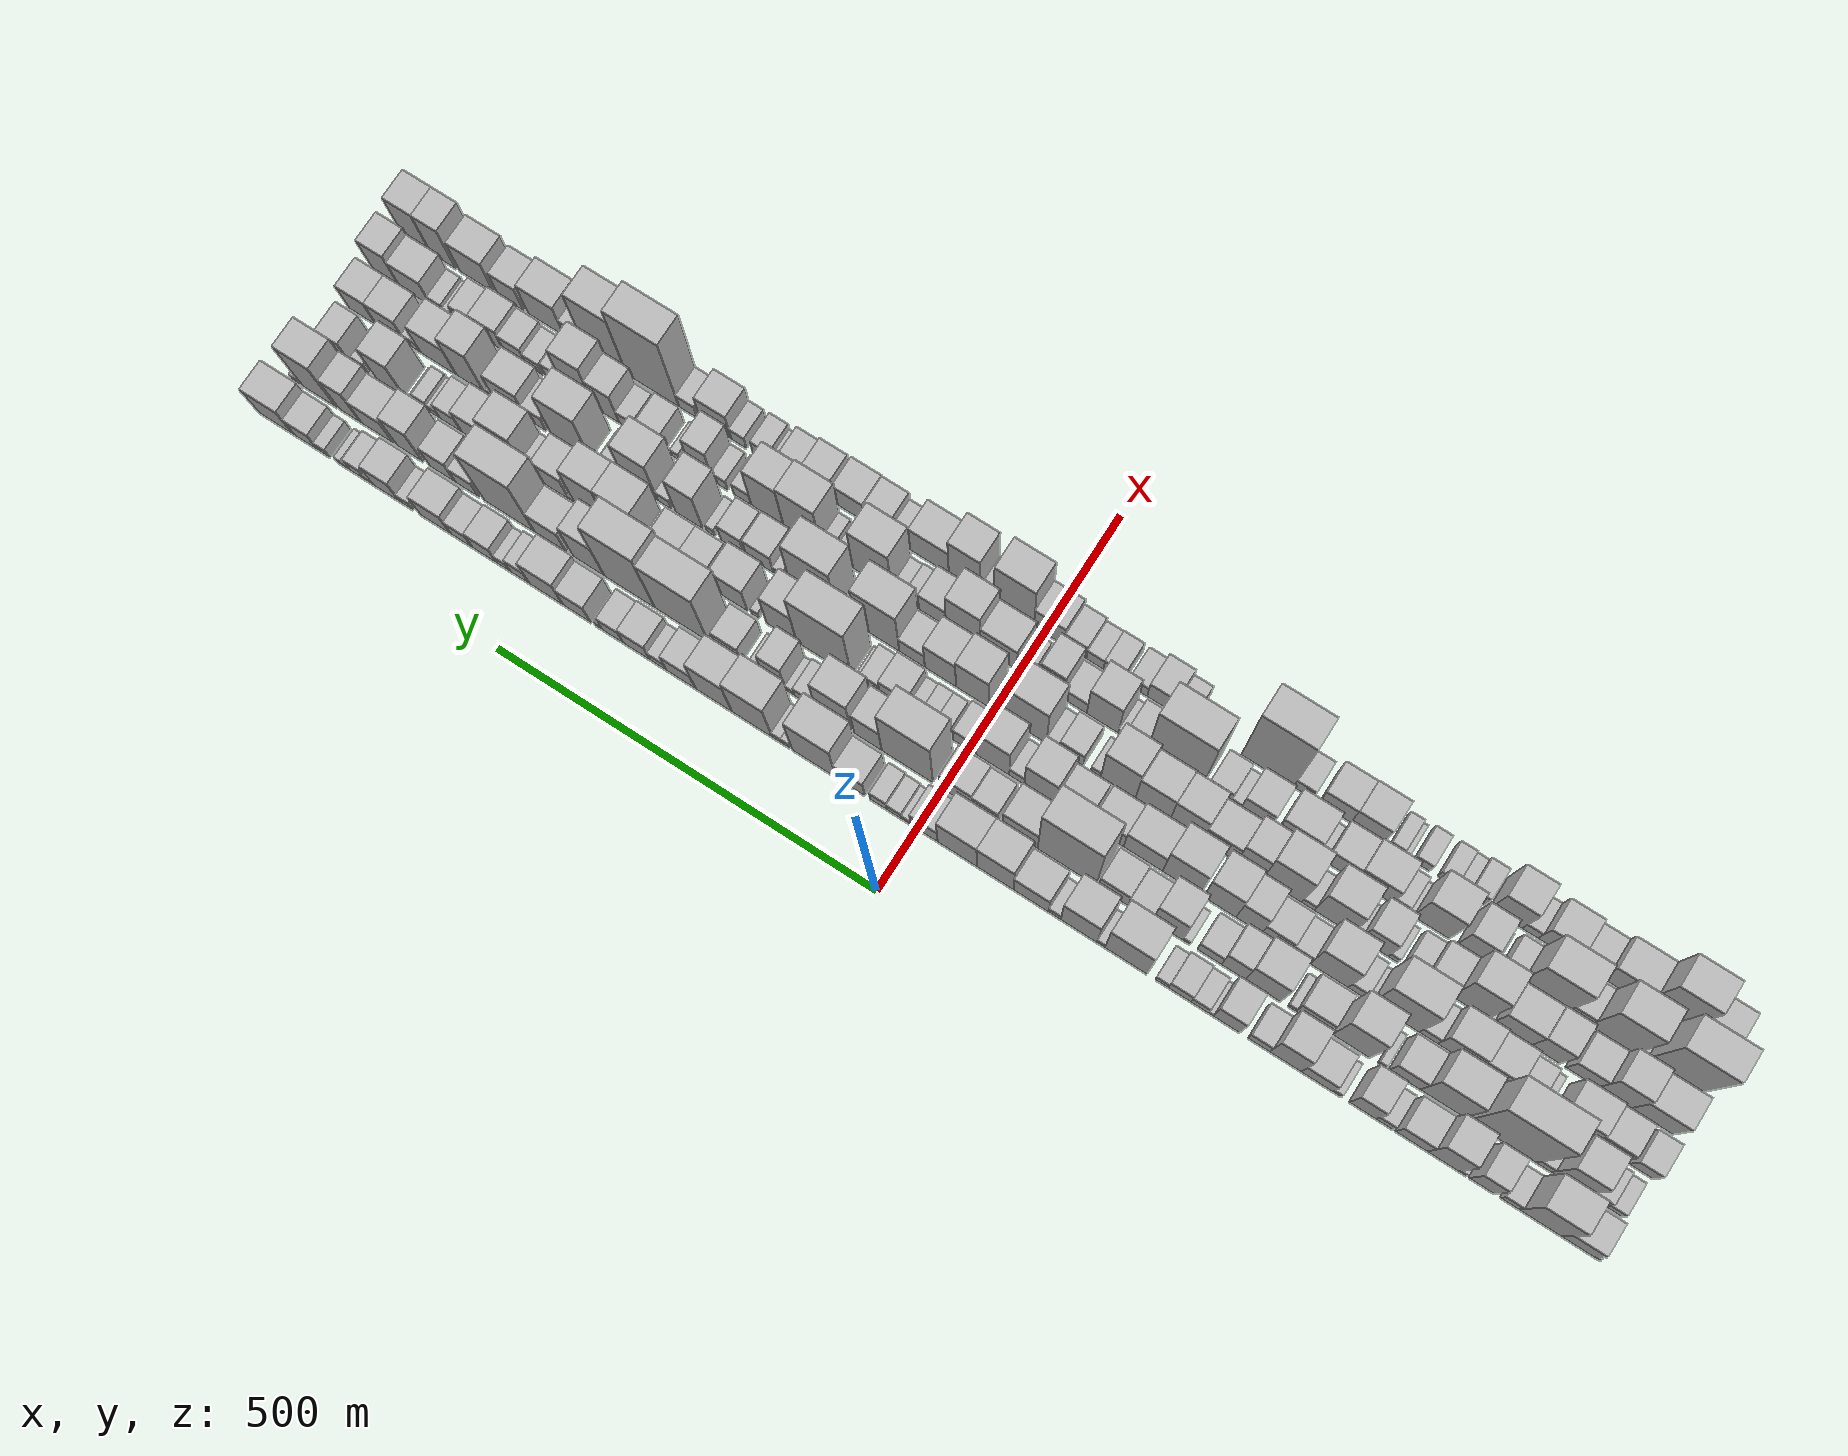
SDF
<sdf version="1.6">
 <world name="default">
  <scene>
   <sky><clouds><speed>12</speed></clouds></sky>
   <ambient>0.4 0.4 0.4 1</ambient>
   <background>0.7 0.7 0.7 1</background>
   <shadows>1</shadows>
  </scene>
  <gravity>0 0 -9.8066</gravity>
  <magnetic_field>6e-06 2.3e-05 -4.2e-05</magnetic_field>
  <physics default="0" name="default_physics" type="ode">
   <ode>
    <solver>
     <type>quick</type>
     <iters>10</iters>
     <sor>1.0</sor>
     <use_dynamic_moi_rescaling>0</use_dynamic_moi_rescaling>
    </solver>
    <constraints>
     <cfm>0</cfm>
     <erp>0.2</erp>
     <contact_max_correcting_vel>100</contact_max_correcting_vel>
     <contact_surface_layer>0.001</contact_surface_layer>
    </constraints>
   </ode>
   <max_step_size>0.004</max_step_size>
   <real_time_factor>1</real_time_factor>
   <real_time_update_rate>250</real_time_update_rate>
  </physics>
  <light name="sun" type="directional">
   <pose>0 0 10 0 0 0</pose>
   <diffuse>0.8 0.8 0.8 1</diffuse>
   <specular>0.2 0.2 0.2 1</specular>
   <attenuation>
    <range>1000</range>
    <constant>0.9</constant>
    <linear>0.01</linear>
    <quadratic>0.001</quadratic>
   </attenuation>
   <direction>-0.5 0.1 -0.9</direction>
  </light>
  <model name="building_1">
   <static>1</static>
   <pose>100.0000 -850.4928 0 0.000000 0.000000 0.000000</pose>
   <link name="link">
    <pose>0 0 7.50 0 0 0</pose>
    <collision name="collision"><geometry><box><size>40.0000 7.0145 15.0000</size></box></geometry></collision>
    <visual name="visual">
     <cast_shadows>0</cast_shadows>
     <geometry><box><size>40.0000 7.0145 15.0000</size></box></geometry>
     <material>
      <script>
       <uri>model://HANNAS_wall/materials/scripts</uri>
       <uri>model://HANNAS_wall/materials/textures</uri>
       <name>vrc/HANNAS_wall</name>
      </script>
     </material>
    </visual>
   </link>
  </model>
  <model name="building_2">
   <static>1</static>
   <pose>100.0000 -827.1640 0 0.000000 0.000000 0.000000</pose>
   <link name="link">
    <pose>0 0 34.50 0 0 0</pose>
    <collision name="collision"><geometry><box><size>40.0000 39.6430 69.0000</size></box></geometry></collision>
    <visual name="visual">
     <cast_shadows>0</cast_shadows>
     <geometry><box><size>40.0000 39.6430 69.0000</size></box></geometry>
     <material>
      <script>
       <uri>model://HANNAS_wall/materials/scripts</uri>
       <uri>model://HANNAS_wall/materials/textures</uri>
       <name>vrc/HANNAS_wall</name>
      </script>
     </material>
    </visual>
   </link>
  </model>
  <model name="building_3">
   <static>1</static>
   <pose>100.0000 -781.2033 0 0.000000 0.000000 0.000000</pose>
   <link name="link">
    <pose>0 0 70.50 0 0 0</pose>
    <collision name="collision"><geometry><box><size>40.0000 52.2784 141.0000</size></box></geometry></collision>
    <visual name="visual">
     <cast_shadows>0</cast_shadows>
     <geometry><box><size>40.0000 52.2784 141.0000</size></box></geometry>
     <material>
      <script>
       <uri>model://HANNAS_wall/materials/scripts</uri>
       <uri>model://HANNAS_wall/materials/textures</uri>
       <name>vrc/HANNAS_wall</name>
      </script>
     </material>
    </visual>
   </link>
  </model>
  <model name="building_4">
   <static>1</static>
   <pose>100.0000 -744.0244 0 0.000000 0.000000 0.000000</pose>
   <link name="link">
    <pose>0 0 19.50 0 0 0</pose>
    <collision name="collision"><geometry><box><size>40.0000 22.0794 39.0000</size></box></geometry></collision>
    <visual name="visual">
     <cast_shadows>0</cast_shadows>
     <geometry><box><size>40.0000 22.0794 39.0000</size></box></geometry>
     <material>
      <script>
       <uri>model://HANNAS_wall/materials/scripts</uri>
       <uri>model://HANNAS_wall/materials/textures</uri>
       <name>vrc/HANNAS_wall</name>
      </script>
     </material>
    </visual>
   </link>
  </model>
  <model name="building_5">
   <static>1</static>
   <pose>100.0000 -710.3621 0 0.000000 0.000000 0.000000</pose>
   <link name="link">
    <pose>0 0 46.50 0 0 0</pose>
    <collision name="collision"><geometry><box><size>40.0000 31.2453 93.0000</size></box></geometry></collision>
    <visual name="visual">
     <cast_shadows>0</cast_shadows>
     <geometry><box><size>40.0000 31.2453 93.0000</size></box></geometry>
     <material>
      <script>
       <uri>model://HANNAS_wall/materials/scripts</uri>
       <uri>model://HANNAS_wall/materials/textures</uri>
       <name>vrc/HANNAS_wall</name>
      </script>
     </material>
    </visual>
   </link>
  </model>
  <model name="building_6">
   <static>1</static>
   <pose>100.0000 -686.9889 0 0.000000 0.000000 0.000000</pose>
   <link name="link">
    <pose>0 0 10.50 0 0 0</pose>
    <collision name="collision"><geometry><box><size>40.0000 9.5010 21.0000</size></box></geometry></collision>
    <visual name="visual">
     <cast_shadows>0</cast_shadows>
     <geometry><box><size>40.0000 9.5010 21.0000</size></box></geometry>
     <material>
      <script>
       <uri>model://HANNAS_wall/materials/scripts</uri>
       <uri>model://HANNAS_wall/materials/textures</uri>
       <name>vrc/HANNAS_wall</name>
      </script>
     </material>
    </visual>
   </link>
  </model>
  <model name="building_7">
   <static>1</static>
   <pose>100.0000 -662.8054 0 0.000000 0.000000 0.000000</pose>
   <link name="link">
    <pose>0 0 63.00 0 0 0</pose>
    <collision name="collision"><geometry><box><size>40.0000 38.8661 126.0000</size></box></geometry></collision>
    <visual name="visual">
     <cast_shadows>0</cast_shadows>
     <geometry><box><size>40.0000 38.8661 126.0000</size></box></geometry>
     <material>
      <script>
       <uri>model://HANNAS_wall/materials/scripts</uri>
       <uri>model://HANNAS_wall/materials/textures</uri>
       <name>vrc/HANNAS_wall</name>
      </script>
     </material>
    </visual>
   </link>
  </model>
  <model name="building_8">
   <static>1</static>
   <pose>100.0000 -623.7122 0 0.000000 0.000000 0.000000</pose>
   <link name="link">
    <pose>0 0 34.50 0 0 0</pose>
    <collision name="collision"><geometry><box><size>40.0000 39.3204 69.0000</size></box></geometry></collision>
    <visual name="visual">
     <cast_shadows>0</cast_shadows>
     <geometry><box><size>40.0000 39.3204 69.0000</size></box></geometry>
     <material>
      <script>
       <uri>model://HANNAS_wall/materials/scripts</uri>
       <uri>model://HANNAS_wall/materials/textures</uri>
       <name>vrc/HANNAS_wall</name>
      </script>
     </material>
    </visual>
   </link>
  </model>
  <model name="building_9">
   <static>1</static>
   <pose>100.0000 -590.5228 0 0.000000 0.000000 0.000000</pose>
   <link name="link">
    <pose>0 0 19.50 0 0 0</pose>
    <collision name="collision"><geometry><box><size>40.0000 21.0584 39.0000</size></box></geometry></collision>
    <visual name="visual">
     <cast_shadows>0</cast_shadows>
     <geometry><box><size>40.0000 21.0584 39.0000</size></box></geometry>
     <material>
      <script>
       <uri>model://HANNAS_wall/materials/scripts</uri>
       <uri>model://HANNAS_wall/materials/textures</uri>
       <name>vrc/HANNAS_wall</name>
      </script>
     </material>
    </visual>
   </link>
  </model>
  <model name="building_10">
   <static>1</static>
   <pose>100.0000 -563.5756 0 0.000000 0.000000 0.000000</pose>
   <link name="link">
    <pose>0 0 48.00 0 0 0</pose>
    <collision name="collision"><geometry><box><size>40.0000 32.8358 96.0000</size></box></geometry></collision>
    <visual name="visual">
     <cast_shadows>0</cast_shadows>
     <geometry><box><size>40.0000 32.8358 96.0000</size></box></geometry>
     <material>
      <script>
       <uri>model://HANNAS_wall/materials/scripts</uri>
       <uri>model://HANNAS_wall/materials/textures</uri>
       <name>vrc/HANNAS_wall</name>
      </script>
     </material>
    </visual>
   </link>
  </model>
  <model name="building_11">
   <static>1</static>
   <pose>100.0000 -531.7365 0 0.000000 0.000000 0.000000</pose>
   <link name="link">
    <pose>0 0 12.00 0 0 0</pose>
    <collision name="collision"><geometry><box><size>40.0000 10.8425 24.0000</size></box></geometry></collision>
    <visual name="visual">
     <cast_shadows>0</cast_shadows>
     <geometry><box><size>40.0000 10.8425 24.0000</size></box></geometry>
     <material>
      <script>
       <uri>model://HANNAS_wall/materials/scripts</uri>
       <uri>model://HANNAS_wall/materials/textures</uri>
       <name>vrc/HANNAS_wall</name>
      </script>
     </material>
    </visual>
   </link>
  </model>
  <model name="building_12">
   <static>1</static>
   <pose>100.0000 -506.7196 0 0.000000 0.000000 0.000000</pose>
   <link name="link">
    <pose>0 0 33.00 0 0 0</pose>
    <collision name="collision"><geometry><box><size>40.0000 39.1913 66.0000</size></box></geometry></collision>
    <visual name="visual">
     <cast_shadows>0</cast_shadows>
     <geometry><box><size>40.0000 39.1913 66.0000</size></box></geometry>
     <material>
      <script>
       <uri>model://HANNAS_wall/materials/scripts</uri>
       <uri>model://HANNAS_wall/materials/textures</uri>
       <name>vrc/HANNAS_wall</name>
      </script>
     </material>
    </visual>
   </link>
  </model>
  <model name="building_13">
   <static>1</static>
   <pose>100.0000 -467.5035 0 0.000000 0.000000 0.000000</pose>
   <link name="link">
    <pose>0 0 63.00 0 0 0</pose>
    <collision name="collision"><geometry><box><size>40.0000 39.2408 126.0000</size></box></geometry></collision>
    <visual name="visual">
     <cast_shadows>0</cast_shadows>
     <geometry><box><size>40.0000 39.2408 126.0000</size></box></geometry>
     <material>
      <script>
       <uri>model://HANNAS_wall/materials/scripts</uri>
       <uri>model://HANNAS_wall/materials/textures</uri>
       <name>vrc/HANNAS_wall</name>
      </script>
     </material>
    </visual>
   </link>
  </model>
  <model name="building_14">
   <static>1</static>
   <pose>100.0000 -434.4610 0 0.000000 0.000000 0.000000</pose>
   <link name="link">
    <pose>0 0 24.00 0 0 0</pose>
    <collision name="collision"><geometry><box><size>40.0000 26.8443 48.0000</size></box></geometry></collision>
    <visual name="visual">
     <cast_shadows>0</cast_shadows>
     <geometry><box><size>40.0000 26.8443 48.0000</size></box></geometry>
     <material>
      <script>
       <uri>model://HANNAS_wall/materials/scripts</uri>
       <uri>model://HANNAS_wall/materials/textures</uri>
       <name>vrc/HANNAS_wall</name>
      </script>
     </material>
    </visual>
   </link>
  </model>
  <model name="building_15">
   <static>1</static>
   <pose>100.0000 -394.2538 0 0.000000 0.000000 0.000000</pose>
   <link name="link">
    <pose>0 0 46.50 0 0 0</pose>
    <collision name="collision"><geometry><box><size>40.0000 33.5702 93.0000</size></box></geometry></collision>
    <visual name="visual">
     <cast_shadows>0</cast_shadows>
     <geometry><box><size>40.0000 33.5702 93.0000</size></box></geometry>
     <material>
      <script>
       <uri>model://HANNAS_wall/materials/scripts</uri>
       <uri>model://HANNAS_wall/materials/textures</uri>
       <name>vrc/HANNAS_wall</name>
      </script>
     </material>
    </visual>
   </link>
  </model>
  <model name="building_16">
   <static>1</static>
   <pose>100.0000 -374.4187 0 0.000000 0.000000 0.000000</pose>
   <link name="link">
    <pose>0 0 7.50 0 0 0</pose>
    <collision name="collision"><geometry><box><size>40.0000 6.0999 15.0000</size></box></geometry></collision>
    <visual name="visual">
     <cast_shadows>0</cast_shadows>
     <geometry><box><size>40.0000 6.0999 15.0000</size></box></geometry>
     <material>
      <script>
       <uri>model://HANNAS_wall/materials/scripts</uri>
       <uri>model://HANNAS_wall/materials/textures</uri>
       <name>vrc/HANNAS_wall</name>
      </script>
     </material>
    </visual>
   </link>
  </model>
  <model name="building_17">
   <static>1</static>
   <pose>100.0000 -360.4036 0 0.000000 0.000000 0.000000</pose>
   <link name="link">
    <pose>0 0 19.50 0 0 0</pose>
    <collision name="collision"><geometry><box><size>40.0000 21.9302 39.0000</size></box></geometry></collision>
    <visual name="visual">
     <cast_shadows>0</cast_shadows>
     <geometry><box><size>40.0000 21.9302 39.0000</size></box></geometry>
     <material>
      <script>
       <uri>model://HANNAS_wall/materials/scripts</uri>
       <uri>model://HANNAS_wall/materials/textures</uri>
       <name>vrc/HANNAS_wall</name>
      </script>
     </material>
    </visual>
   </link>
  </model>
  <model name="building_18">
   <static>1</static>
   <pose>100.0000 -335.2173 0 0.000000 0.000000 0.000000</pose>
   <link name="link">
    <pose>0 0 25.50 0 0 0</pose>
    <collision name="collision"><geometry><box><size>40.0000 28.4425 51.0000</size></box></geometry></collision>
    <visual name="visual">
     <cast_shadows>0</cast_shadows>
     <geometry><box><size>40.0000 28.4425 51.0000</size></box></geometry>
     <material>
      <script>
       <uri>model://HANNAS_wall/materials/scripts</uri>
       <uri>model://HANNAS_wall/materials/textures</uri>
       <name>vrc/HANNAS_wall</name>
      </script>
     </material>
    </visual>
   </link>
  </model>
  <model name="building_19">
   <static>1</static>
   <pose>100.0000 -312.6675 0 0.000000 0.000000 0.000000</pose>
   <link name="link">
    <pose>0 0 15.00 0 0 0</pose>
    <collision name="collision"><geometry><box><size>40.0000 16.6571 30.0000</size></box></geometry></collision>
    <visual name="visual">
     <cast_shadows>0</cast_shadows>
     <geometry><box><size>40.0000 16.6571 30.0000</size></box></geometry>
     <material>
      <script>
       <uri>model://HANNAS_wall/materials/scripts</uri>
       <uri>model://HANNAS_wall/materials/textures</uri>
       <name>vrc/HANNAS_wall</name>
      </script>
     </material>
    </visual>
   </link>
  </model>
  <model name="building_20">
   <static>1</static>
   <pose>100.0000 -267.3836 0 0.000000 0.000000 0.000000</pose>
   <link name="link">
    <pose>0 0 72.00 0 0 0</pose>
    <collision name="collision"><geometry><box><size>40.0000 53.9107 144.0000</size></box></geometry></collision>
    <visual name="visual">
     <cast_shadows>0</cast_shadows>
     <geometry><box><size>40.0000 53.9107 144.0000</size></box></geometry>
     <material>
      <script>
       <uri>model://HANNAS_wall/materials/scripts</uri>
       <uri>model://HANNAS_wall/materials/textures</uri>
       <name>vrc/HANNAS_wall</name>
      </script>
     </material>
    </visual>
   </link>
  </model>
  <model name="building_21">
   <static>1</static>
   <pose>100.0000 -235.2414 0 0.000000 0.000000 0.000000</pose>
   <link name="link">
    <pose>0 0 12.00 0 0 0</pose>
    <collision name="collision"><geometry><box><size>40.0000 10.3735 24.0000</size></box></geometry></collision>
    <visual name="visual">
     <cast_shadows>0</cast_shadows>
     <geometry><box><size>40.0000 10.3735 24.0000</size></box></geometry>
     <material>
      <script>
       <uri>model://HANNAS_wall/materials/scripts</uri>
       <uri>model://HANNAS_wall/materials/textures</uri>
       <name>vrc/HANNAS_wall</name>
      </script>
     </material>
    </visual>
   </link>
  </model>
  <model name="building_22">
   <static>1</static>
   <pose>100.0000 -207.0619 0 0.000000 0.000000 0.000000</pose>
   <link name="link">
    <pose>0 0 61.50 0 0 0</pose>
    <collision name="collision"><geometry><box><size>40.0000 45.9857 123.0000</size></box></geometry></collision>
    <visual name="visual">
     <cast_shadows>0</cast_shadows>
     <geometry><box><size>40.0000 45.9857 123.0000</size></box></geometry>
     <material>
      <script>
       <uri>model://HANNAS_wall/materials/scripts</uri>
       <uri>model://HANNAS_wall/materials/textures</uri>
       <name>vrc/HANNAS_wall</name>
      </script>
     </material>
    </visual>
   </link>
  </model>
  <model name="building_23">
   <static>1</static>
   <pose>100.0000 -176.2472 0 0.000000 0.000000 0.000000</pose>
   <link name="link">
    <pose>0 0 15.00 0 0 0</pose>
    <collision name="collision"><geometry><box><size>40.0000 15.6436 30.0000</size></box></geometry></collision>
    <visual name="visual">
     <cast_shadows>0</cast_shadows>
     <geometry><box><size>40.0000 15.6436 30.0000</size></box></geometry>
     <material>
      <script>
       <uri>model://HANNAS_wall/materials/scripts</uri>
       <uri>model://HANNAS_wall/materials/textures</uri>
       <name>vrc/HANNAS_wall</name>
      </script>
     </material>
    </visual>
   </link>
  </model>
  <model name="building_24">
   <static>1</static>
   <pose>100.0000 -145.9014 0 0.000000 0.000000 0.000000</pose>
   <link name="link">
    <pose>0 0 42.00 0 0 0</pose>
    <collision name="collision"><geometry><box><size>40.0000 45.0481 84.0000</size></box></geometry></collision>
    <visual name="visual">
     <cast_shadows>0</cast_shadows>
     <geometry><box><size>40.0000 45.0481 84.0000</size></box></geometry>
     <material>
      <script>
       <uri>model://HANNAS_wall/materials/scripts</uri>
       <uri>model://HANNAS_wall/materials/textures</uri>
       <name>vrc/HANNAS_wall</name>
      </script>
     </material>
    </visual>
   </link>
  </model>
  <model name="building_25">
   <static>1</static>
   <pose>100.0000 -99.7520 0 0.000000 0.000000 0.000000</pose>
   <link name="link">
    <pose>0 0 63.00 0 0 0</pose>
    <collision name="collision"><geometry><box><size>40.0000 47.2507 126.0000</size></box></geometry></collision>
    <visual name="visual">
     <cast_shadows>0</cast_shadows>
     <geometry><box><size>40.0000 47.2507 126.0000</size></box></geometry>
     <material>
      <script>
       <uri>model://HANNAS_wall/materials/scripts</uri>
       <uri>model://HANNAS_wall/materials/textures</uri>
       <name>vrc/HANNAS_wall</name>
      </script>
     </material>
    </visual>
   </link>
  </model>
  <model name="building_26">
   <static>1</static>
   <pose>100.0000 -50.9688 0 0.000000 0.000000 0.000000</pose>
   <link name="link">
    <pose>0 0 63.00 0 0 0</pose>
    <collision name="collision"><geometry><box><size>40.0000 50.3157 126.0000</size></box></geometry></collision>
    <visual name="visual">
     <cast_shadows>0</cast_shadows>
     <geometry><box><size>40.0000 50.3157 126.0000</size></box></geometry>
     <material>
      <script>
       <uri>model://HANNAS_wall/materials/scripts</uri>
       <uri>model://HANNAS_wall/materials/textures</uri>
       <name>vrc/HANNAS_wall</name>
      </script>
     </material>
    </visual>
   </link>
  </model>
  <model name="building_27">
   <static>1</static>
   <pose>100.0000 -8.4160 0 0.000000 0.000000 0.000000</pose>
   <link name="link">
    <pose>0 0 33.00 0 0 0</pose>
    <collision name="collision"><geometry><box><size>40.0000 34.7900 66.0000</size></box></geometry></collision>
    <visual name="visual">
     <cast_shadows>0</cast_shadows>
     <geometry><box><size>40.0000 34.7900 66.0000</size></box></geometry>
     <material>
      <script>
       <uri>model://HANNAS_wall/materials/scripts</uri>
       <uri>model://HANNAS_wall/materials/textures</uri>
       <name>vrc/HANNAS_wall</name>
      </script>
     </material>
    </visual>
   </link>
  </model>
  <model name="building_28">
   <static>1</static>
   <pose>100.0000 14.8980 0 0.000000 0.000000 0.000000</pose>
   <link name="link">
    <pose>0 0 12.00 0 0 0</pose>
    <collision name="collision"><geometry><box><size>40.0000 11.8380 24.0000</size></box></geometry></collision>
    <visual name="visual">
     <cast_shadows>0</cast_shadows>
     <geometry><box><size>40.0000 11.8380 24.0000</size></box></geometry>
     <material>
      <script>
       <uri>model://HANNAS_wall/materials/scripts</uri>
       <uri>model://HANNAS_wall/materials/textures</uri>
       <name>vrc/HANNAS_wall</name>
      </script>
     </material>
    </visual>
   </link>
  </model>
  <model name="building_29">
   <static>1</static>
   <pose>100.0000 30.3030 0 0.000000 0.000000 0.000000</pose>
   <link name="link">
    <pose>0 0 16.50 0 0 0</pose>
    <collision name="collision"><geometry><box><size>40.0000 18.9719 33.0000</size></box></geometry></collision>
    <visual name="visual">
     <cast_shadows>0</cast_shadows>
     <geometry><box><size>40.0000 18.9719 33.0000</size></box></geometry>
     <material>
      <script>
       <uri>model://HANNAS_wall/materials/scripts</uri>
       <uri>model://HANNAS_wall/materials/textures</uri>
       <name>vrc/HANNAS_wall</name>
      </script>
     </material>
    </visual>
   </link>
  </model>
  <model name="building_30">
   <static>1</static>
   <pose>100.0000 50.5522 0 0.000000 0.000000 0.000000</pose>
   <link name="link">
    <pose>0 0 21.00 0 0 0</pose>
    <collision name="collision"><geometry><box><size>40.0000 21.5266 42.0000</size></box></geometry></collision>
    <visual name="visual">
     <cast_shadows>0</cast_shadows>
     <geometry><box><size>40.0000 21.5266 42.0000</size></box></geometry>
     <material>
      <script>
       <uri>model://HANNAS_wall/materials/scripts</uri>
       <uri>model://HANNAS_wall/materials/textures</uri>
       <name>vrc/HANNAS_wall</name>
      </script>
     </material>
    </visual>
   </link>
  </model>
  <model name="building_31">
   <static>1</static>
   <pose>100.0000 87.1205 0 0.000000 0.000000 0.000000</pose>
   <link name="link">
    <pose>0 0 36.00 0 0 0</pose>
    <collision name="collision"><geometry><box><size>40.0000 37.6100 72.0000</size></box></geometry></collision>
    <visual name="visual">
     <cast_shadows>0</cast_shadows>
     <geometry><box><size>40.0000 37.6100 72.0000</size></box></geometry>
     <material>
      <script>
       <uri>model://HANNAS_wall/materials/scripts</uri>
       <uri>model://HANNAS_wall/materials/textures</uri>
       <name>vrc/HANNAS_wall</name>
      </script>
     </material>
    </visual>
   </link>
  </model>
  <model name="building_32">
   <static>1</static>
   <pose>100.0000 134.5397 0 0.000000 0.000000 0.000000</pose>
   <link name="link">
    <pose>0 0 73.50 0 0 0</pose>
    <collision name="collision"><geometry><box><size>40.0000 57.2284 147.0000</size></box></geometry></collision>
    <visual name="visual">
     <cast_shadows>0</cast_shadows>
     <geometry><box><size>40.0000 57.2284 147.0000</size></box></geometry>
     <material>
      <script>
       <uri>model://HANNAS_wall/materials/scripts</uri>
       <uri>model://HANNAS_wall/materials/textures</uri>
       <name>vrc/HANNAS_wall</name>
      </script>
     </material>
    </visual>
   </link>
  </model>
  <model name="building_33">
   <static>1</static>
   <pose>100.0000 171.6060 0 0.000000 0.000000 0.000000</pose>
   <link name="link">
    <pose>0 0 13.50 0 0 0</pose>
    <collision name="collision"><geometry><box><size>40.0000 10.9042 27.0000</size></box></geometry></collision>
    <visual name="visual">
     <cast_shadows>0</cast_shadows>
     <geometry><box><size>40.0000 10.9042 27.0000</size></box></geometry>
     <material>
      <script>
       <uri>model://HANNAS_wall/materials/scripts</uri>
       <uri>model://HANNAS_wall/materials/textures</uri>
       <name>vrc/HANNAS_wall</name>
      </script>
     </material>
    </visual>
   </link>
  </model>
  <model name="building_34">
   <static>1</static>
   <pose>100.0000 183.1863 0 0.000000 0.000000 0.000000</pose>
   <link name="link">
    <pose>0 0 13.50 0 0 0</pose>
    <collision name="collision"><geometry><box><size>40.0000 12.2563 27.0000</size></box></geometry></collision>
    <visual name="visual">
     <cast_shadows>0</cast_shadows>
     <geometry><box><size>40.0000 12.2563 27.0000</size></box></geometry>
     <material>
      <script>
       <uri>model://HANNAS_wall/materials/scripts</uri>
       <uri>model://HANNAS_wall/materials/textures</uri>
       <name>vrc/HANNAS_wall</name>
      </script>
     </material>
    </visual>
   </link>
  </model>
  <model name="building_35">
   <static>1</static>
   <pose>100.0000 215.8746 0 0.000000 0.000000 0.000000</pose>
   <link name="link">
    <pose>0 0 72.00 0 0 0</pose>
    <collision name="collision"><geometry><box><size>40.0000 53.1204 144.0000</size></box></geometry></collision>
    <visual name="visual">
     <cast_shadows>0</cast_shadows>
     <geometry><box><size>40.0000 53.1204 144.0000</size></box></geometry>
     <material>
      <script>
       <uri>model://HANNAS_wall/materials/scripts</uri>
       <uri>model://HANNAS_wall/materials/textures</uri>
       <name>vrc/HANNAS_wall</name>
      </script>
     </material>
    </visual>
   </link>
  </model>
  <model name="building_36">
   <static>1</static>
   <pose>100.0000 266.4182 0 0.000000 0.000000 0.000000</pose>
   <link name="link">
    <pose>0 0 61.50 0 0 0</pose>
    <collision name="collision"><geometry><box><size>40.0000 47.9667 123.0000</size></box></geometry></collision>
    <visual name="visual">
     <cast_shadows>0</cast_shadows>
     <geometry><box><size>40.0000 47.9667 123.0000</size></box></geometry>
     <material>
      <script>
       <uri>model://HANNAS_wall/materials/scripts</uri>
       <uri>model://HANNAS_wall/materials/textures</uri>
       <name>vrc/HANNAS_wall</name>
      </script>
     </material>
    </visual>
   </link>
  </model>
  <model name="building_37">
   <static>1</static>
   <pose>100.0000 310.0759 0 0.000000 0.000000 0.000000</pose>
   <link name="link">
    <pose>0 0 34.50 0 0 0</pose>
    <collision name="collision"><geometry><box><size>40.0000 39.3489 69.0000</size></box></geometry></collision>
    <visual name="visual">
     <cast_shadows>0</cast_shadows>
     <geometry><box><size>40.0000 39.3489 69.0000</size></box></geometry>
     <material>
      <script>
       <uri>model://HANNAS_wall/materials/scripts</uri>
       <uri>model://HANNAS_wall/materials/textures</uri>
       <name>vrc/HANNAS_wall</name>
      </script>
     </material>
    </visual>
   </link>
  </model>
  <model name="building_38">
   <static>1</static>
   <pose>100.0000 340.4002 0 0.000000 0.000000 0.000000</pose>
   <link name="link">
    <pose>0 0 18.00 0 0 0</pose>
    <collision name="collision"><geometry><box><size>40.0000 21.2996 36.0000</size></box></geometry></collision>
    <visual name="visual">
     <cast_shadows>0</cast_shadows>
     <geometry><box><size>40.0000 21.2996 36.0000</size></box></geometry>
     <material>
      <script>
       <uri>model://HANNAS_wall/materials/scripts</uri>
       <uri>model://HANNAS_wall/materials/textures</uri>
       <name>vrc/HANNAS_wall</name>
      </script>
     </material>
    </visual>
   </link>
  </model>
  <model name="building_39">
   <static>1</static>
   <pose>100.0000 368.7714 0 0.000000 0.000000 0.000000</pose>
   <link name="link">
    <pose>0 0 31.50 0 0 0</pose>
    <collision name="collision"><geometry><box><size>40.0000 35.4428 63.0000</size></box></geometry></collision>
    <visual name="visual">
     <cast_shadows>0</cast_shadows>
     <geometry><box><size>40.0000 35.4428 63.0000</size></box></geometry>
     <material>
      <script>
       <uri>model://HANNAS_wall/materials/scripts</uri>
       <uri>model://HANNAS_wall/materials/textures</uri>
       <name>vrc/HANNAS_wall</name>
      </script>
     </material>
    </visual>
   </link>
  </model>
  <model name="building_40">
   <static>1</static>
   <pose>100.0000 400.8634 0 0.000000 0.000000 0.000000</pose>
   <link name="link">
    <pose>0 0 27.00 0 0 0</pose>
    <collision name="collision"><geometry><box><size>40.0000 28.7413 54.0000</size></box></geometry></collision>
    <visual name="visual">
     <cast_shadows>0</cast_shadows>
     <geometry><box><size>40.0000 28.7413 54.0000</size></box></geometry>
     <material>
      <script>
       <uri>model://HANNAS_wall/materials/scripts</uri>
       <uri>model://HANNAS_wall/materials/textures</uri>
       <name>vrc/HANNAS_wall</name>
      </script>
     </material>
    </visual>
   </link>
  </model>
  <model name="building_41">
   <static>1</static>
   <pose>100.0000 419.4619 0 0.000000 0.000000 0.000000</pose>
   <link name="link">
    <pose>0 0 10.50 0 0 0</pose>
    <collision name="collision"><geometry><box><size>40.0000 8.4557 21.0000</size></box></geometry></collision>
    <visual name="visual">
     <cast_shadows>0</cast_shadows>
     <geometry><box><size>40.0000 8.4557 21.0000</size></box></geometry>
     <material>
      <script>
       <uri>model://HANNAS_wall/materials/scripts</uri>
       <uri>model://HANNAS_wall/materials/textures</uri>
       <name>vrc/HANNAS_wall</name>
      </script>
     </material>
    </visual>
   </link>
  </model>
  <model name="building_42">
   <static>1</static>
   <pose>100.0000 448.1428 0 0.000000 0.000000 0.000000</pose>
   <link name="link">
    <pose>0 0 34.50 0 0 0</pose>
    <collision name="collision"><geometry><box><size>40.0000 36.9061 69.0000</size></box></geometry></collision>
    <visual name="visual">
     <cast_shadows>0</cast_shadows>
     <geometry><box><size>40.0000 36.9061 69.0000</size></box></geometry>
     <material>
      <script>
       <uri>model://HANNAS_wall/materials/scripts</uri>
       <uri>model://HANNAS_wall/materials/textures</uri>
       <name>vrc/HANNAS_wall</name>
      </script>
     </material>
    </visual>
   </link>
  </model>
  <model name="building_43">
   <static>1</static>
   <pose>100.0000 489.4300 0 0.000000 0.000000 0.000000</pose>
   <link name="link">
    <pose>0 0 45.00 0 0 0</pose>
    <collision name="collision"><geometry><box><size>40.0000 45.6684 90.0000</size></box></geometry></collision>
    <visual name="visual">
     <cast_shadows>0</cast_shadows>
     <geometry><box><size>40.0000 45.6684 90.0000</size></box></geometry>
     <material>
      <script>
       <uri>model://HANNAS_wall/materials/scripts</uri>
       <uri>model://HANNAS_wall/materials/textures</uri>
       <name>vrc/HANNAS_wall</name>
      </script>
     </material>
    </visual>
   </link>
  </model>
  <model name="building_44">
   <static>1</static>
   <pose>100.0000 525.2028 0 0.000000 0.000000 0.000000</pose>
   <link name="link">
    <pose>0 0 25.50 0 0 0</pose>
    <collision name="collision"><geometry><box><size>40.0000 25.8772 51.0000</size></box></geometry></collision>
    <visual name="visual">
     <cast_shadows>0</cast_shadows>
     <geometry><box><size>40.0000 25.8772 51.0000</size></box></geometry>
     <material>
      <script>
       <uri>model://HANNAS_wall/materials/scripts</uri>
       <uri>model://HANNAS_wall/materials/textures</uri>
       <name>vrc/HANNAS_wall</name>
      </script>
     </material>
    </visual>
   </link>
  </model>
  <model name="building_45">
   <static>1</static>
   <pose>100.0000 547.0188 0 0.000000 0.000000 0.000000</pose>
   <link name="link">
    <pose>0 0 16.50 0 0 0</pose>
    <collision name="collision"><geometry><box><size>40.0000 17.7548 33.0000</size></box></geometry></collision>
    <visual name="visual">
     <cast_shadows>0</cast_shadows>
     <geometry><box><size>40.0000 17.7548 33.0000</size></box></geometry>
     <material>
      <script>
       <uri>model://HANNAS_wall/materials/scripts</uri>
       <uri>model://HANNAS_wall/materials/textures</uri>
       <name>vrc/HANNAS_wall</name>
      </script>
     </material>
    </visual>
   </link>
  </model>
  <model name="building_46">
   <static>1</static>
   <pose>100.0000 572.5653 0 0.000000 0.000000 0.000000</pose>
   <link name="link">
    <pose>0 0 30.00 0 0 0</pose>
    <collision name="collision"><geometry><box><size>40.0000 33.3383 60.0000</size></box></geometry></collision>
    <visual name="visual">
     <cast_shadows>0</cast_shadows>
     <geometry><box><size>40.0000 33.3383 60.0000</size></box></geometry>
     <material>
      <script>
       <uri>model://HANNAS_wall/materials/scripts</uri>
       <uri>model://HANNAS_wall/materials/textures</uri>
       <name>vrc/HANNAS_wall</name>
      </script>
     </material>
    </visual>
   </link>
  </model>
  <model name="building_47">
   <static>1</static>
   <pose>100.0000 603.7695 0 0.000000 0.000000 0.000000</pose>
   <link name="link">
    <pose>0 0 25.50 0 0 0</pose>
    <collision name="collision"><geometry><box><size>40.0000 29.0700 51.0000</size></box></geometry></collision>
    <visual name="visual">
     <cast_shadows>0</cast_shadows>
     <geometry><box><size>40.0000 29.0700 51.0000</size></box></geometry>
     <material>
      <script>
       <uri>model://HANNAS_wall/materials/scripts</uri>
       <uri>model://HANNAS_wall/materials/textures</uri>
       <name>vrc/HANNAS_wall</name>
      </script>
     </material>
    </visual>
   </link>
  </model>
  <model name="building_48">
   <static>1</static>
   <pose>100.0000 639.3489 0 0.000000 0.000000 0.000000</pose>
   <link name="link">
    <pose>0 0 36.00 0 0 0</pose>
    <collision name="collision"><geometry><box><size>40.0000 42.0888 72.0000</size></box></geometry></collision>
    <visual name="visual">
     <cast_shadows>0</cast_shadows>
     <geometry><box><size>40.0000 42.0888 72.0000</size></box></geometry>
     <material>
      <script>
       <uri>model://HANNAS_wall/materials/scripts</uri>
       <uri>model://HANNAS_wall/materials/textures</uri>
       <name>vrc/HANNAS_wall</name>
      </script>
     </material>
    </visual>
   </link>
  </model>
  <model name="building_49">
   <static>1</static>
   <pose>100.0000 678.9602 0 0.000000 0.000000 0.000000</pose>
   <link name="link">
    <pose>0 0 15.00 0 0 0</pose>
    <collision name="collision"><geometry><box><size>40.0000 17.1336 30.0000</size></box></geometry></collision>
    <visual name="visual">
     <cast_shadows>0</cast_shadows>
     <geometry><box><size>40.0000 17.1336 30.0000</size></box></geometry>
     <material>
      <script>
       <uri>model://HANNAS_wall/materials/scripts</uri>
       <uri>model://HANNAS_wall/materials/textures</uri>
       <name>vrc/HANNAS_wall</name>
      </script>
     </material>
    </visual>
   </link>
  </model>
  <model name="building_50">
   <static>1</static>
   <pose>100.0000 706.3037 0 0.000000 0.000000 0.000000</pose>
   <link name="link">
    <pose>0 0 36.00 0 0 0</pose>
    <collision name="collision"><geometry><box><size>40.0000 37.5535 72.0000</size></box></geometry></collision>
    <visual name="visual">
     <cast_shadows>0</cast_shadows>
     <geometry><box><size>40.0000 37.5535 72.0000</size></box></geometry>
     <material>
      <script>
       <uri>model://HANNAS_wall/materials/scripts</uri>
       <uri>model://HANNAS_wall/materials/textures</uri>
       <name>vrc/HANNAS_wall</name>
      </script>
     </material>
    </visual>
   </link>
  </model>
  <model name="building_51">
   <static>1</static>
   <pose>100.0000 729.7993 0 0.000000 0.000000 0.000000</pose>
   <link name="link">
    <pose>0 0 10.50 0 0 0</pose>
    <collision name="collision"><geometry><box><size>40.0000 9.4378 21.0000</size></box></geometry></collision>
    <visual name="visual">
     <cast_shadows>0</cast_shadows>
     <geometry><box><size>40.0000 9.4378 21.0000</size></box></geometry>
     <material>
      <script>
       <uri>model://HANNAS_wall/materials/scripts</uri>
       <uri>model://HANNAS_wall/materials/textures</uri>
       <name>vrc/HANNAS_wall</name>
      </script>
     </material>
    </visual>
   </link>
  </model>
  <model name="building_52">
   <static>1</static>
   <pose>100.0000 745.5802 0 0.000000 0.000000 0.000000</pose>
   <link name="link">
    <pose>0 0 21.00 0 0 0</pose>
    <collision name="collision"><geometry><box><size>40.0000 22.1240 42.0000</size></box></geometry></collision>
    <visual name="visual">
     <cast_shadows>0</cast_shadows>
     <geometry><box><size>40.0000 22.1240 42.0000</size></box></geometry>
     <material>
      <script>
       <uri>model://HANNAS_wall/materials/scripts</uri>
       <uri>model://HANNAS_wall/materials/textures</uri>
       <name>vrc/HANNAS_wall</name>
      </script>
     </material>
    </visual>
   </link>
  </model>
  <model name="building_53">
   <static>1</static>
   <pose>100.0000 760.9786 0 0.000000 0.000000 0.000000</pose>
   <link name="link">
    <pose>0 0 9.00 0 0 0</pose>
    <collision name="collision"><geometry><box><size>40.0000 8.6729 18.0000</size></box></geometry></collision>
    <visual name="visual">
     <cast_shadows>0</cast_shadows>
     <geometry><box><size>40.0000 8.6729 18.0000</size></box></geometry>
     <material>
      <script>
       <uri>model://HANNAS_wall/materials/scripts</uri>
       <uri>model://HANNAS_wall/materials/textures</uri>
       <name>vrc/HANNAS_wall</name>
      </script>
     </material>
    </visual>
   </link>
  </model>
  <model name="building_54">
   <static>1</static>
   <pose>100.0000 769.6491 0 0.000000 0.000000 0.000000</pose>
   <link name="link">
    <pose>0 0 10.50 0 0 0</pose>
    <collision name="collision"><geometry><box><size>40.0000 8.6680 21.0000</size></box></geometry></collision>
    <visual name="visual">
     <cast_shadows>0</cast_shadows>
     <geometry><box><size>40.0000 8.6680 21.0000</size></box></geometry>
     <material>
      <script>
       <uri>model://HANNAS_wall/materials/scripts</uri>
       <uri>model://HANNAS_wall/materials/textures</uri>
       <name>vrc/HANNAS_wall</name>
      </script>
     </material>
    </visual>
   </link>
  </model>
  <model name="building_55">
   <static>1</static>
   <pose>100.0000 791.7170 0 0.000000 0.000000 0.000000</pose>
   <link name="link">
    <pose>0 0 15.00 0 0 0</pose>
    <collision name="collision"><geometry><box><size>40.0000 15.4677 30.0000</size></box></geometry></collision>
    <visual name="visual">
     <cast_shadows>0</cast_shadows>
     <geometry><box><size>40.0000 15.4677 30.0000</size></box></geometry>
     <material>
      <script>
       <uri>model://HANNAS_wall/materials/scripts</uri>
       <uri>model://HANNAS_wall/materials/textures</uri>
       <name>vrc/HANNAS_wall</name>
      </script>
     </material>
    </visual>
   </link>
  </model>
  <model name="building_56">
   <static>1</static>
   <pose>100.0000 816.1798 0 0.000000 0.000000 0.000000</pose>
   <link name="link">
    <pose>0 0 28.50 0 0 0</pose>
    <collision name="collision"><geometry><box><size>40.0000 33.4580 57.0000</size></box></geometry></collision>
    <visual name="visual">
     <cast_shadows>0</cast_shadows>
     <geometry><box><size>40.0000 33.4580 57.0000</size></box></geometry>
     <material>
      <script>
       <uri>model://HANNAS_wall/materials/scripts</uri>
       <uri>model://HANNAS_wall/materials/textures</uri>
       <name>vrc/HANNAS_wall</name>
      </script>
     </material>
    </visual>
   </link>
  </model>
  <model name="building_57">
   <static>1</static>
   <pose>100.0000 857.4980 0 0.000000 0.000000 0.000000</pose>
   <link name="link">
    <pose>0 0 42.00 0 0 0</pose>
    <collision name="collision"><geometry><box><size>40.0000 49.1783 84.0000</size></box></geometry></collision>
    <visual name="visual">
     <cast_shadows>0</cast_shadows>
     <geometry><box><size>40.0000 49.1783 84.0000</size></box></geometry>
     <material>
      <script>
       <uri>model://HANNAS_wall/materials/scripts</uri>
       <uri>model://HANNAS_wall/materials/textures</uri>
       <name>vrc/HANNAS_wall</name>
      </script>
     </material>
    </visual>
   </link>
  </model>
  <model name="building_58">
   <static>1</static>
   <pose>152.0000 -841.1821 0 0.000000 0.000000 0.000000</pose>
   <link name="link">
    <pose>0 0 16.50 0 0 0</pose>
    <collision name="collision"><geometry><box><size>40.0000 19.6358 33.0000</size></box></geometry></collision>
    <visual name="visual">
     <cast_shadows>0</cast_shadows>
     <geometry><box><size>40.0000 19.6358 33.0000</size></box></geometry>
     <material>
      <script>
       <uri>model://HANNAS_wall/materials/scripts</uri>
       <uri>model://HANNAS_wall/materials/textures</uri>
       <name>vrc/HANNAS_wall</name>
      </script>
     </material>
    </visual>
   </link>
  </model>
  <model name="building_59">
   <static>1</static>
   <pose>152.0000 -818.9174 0 0.000000 0.000000 0.000000</pose>
   <link name="link">
    <pose>0 0 24.00 0 0 0</pose>
    <collision name="collision"><geometry><box><size>40.0000 24.8937 48.0000</size></box></geometry></collision>
    <visual name="visual">
     <cast_shadows>0</cast_shadows>
     <geometry><box><size>40.0000 24.8937 48.0000</size></box></geometry>
     <material>
      <script>
       <uri>model://HANNAS_wall/materials/scripts</uri>
       <uri>model://HANNAS_wall/materials/textures</uri>
       <name>vrc/HANNAS_wall</name>
      </script>
     </material>
    </visual>
   </link>
  </model>
  <model name="building_60">
   <static>1</static>
   <pose>152.0000 -785.4999 0 0.000000 0.000000 0.000000</pose>
   <link name="link">
    <pose>0 0 64.50 0 0 0</pose>
    <collision name="collision"><geometry><box><size>40.0000 41.9413 129.0000</size></box></geometry></collision>
    <visual name="visual">
     <cast_shadows>0</cast_shadows>
     <geometry><box><size>40.0000 41.9413 129.0000</size></box></geometry>
     <material>
      <script>
       <uri>model://HANNAS_wall/materials/scripts</uri>
       <uri>model://HANNAS_wall/materials/textures</uri>
       <name>vrc/HANNAS_wall</name>
      </script>
     </material>
    </visual>
   </link>
  </model>
  <model name="building_61">
   <static>1</static>
   <pose>152.0000 -755.1609 0 0.000000 0.000000 0.000000</pose>
   <link name="link">
    <pose>0 0 18.00 0 0 0</pose>
    <collision name="collision"><geometry><box><size>40.0000 18.7368 36.0000</size></box></geometry></collision>
    <visual name="visual">
     <cast_shadows>0</cast_shadows>
     <geometry><box><size>40.0000 18.7368 36.0000</size></box></geometry>
     <material>
      <script>
       <uri>model://HANNAS_wall/materials/scripts</uri>
       <uri>model://HANNAS_wall/materials/textures</uri>
       <name>vrc/HANNAS_wall</name>
      </script>
     </material>
    </visual>
   </link>
  </model>
  <model name="building_62">
   <static>1</static>
   <pose>152.0000 -704.5812 0 0.000000 0.000000 0.000000</pose>
   <link name="link">
    <pose>0 0 109.50 0 0 0</pose>
    <collision name="collision"><geometry><box><size>40.0000 82.4225 219.0000</size></box></geometry></collision>
    <visual name="visual">
     <cast_shadows>0</cast_shadows>
     <geometry><box><size>40.0000 82.4225 219.0000</size></box></geometry>
     <material>
      <script>
       <uri>model://HANNAS_wall/materials/scripts</uri>
       <uri>model://HANNAS_wall/materials/textures</uri>
       <name>vrc/HANNAS_wall</name>
      </script>
     </material>
    </visual>
   </link>
  </model>
  <model name="building_63">
   <static>1</static>
   <pose>152.0000 -631.2233 0 0.000000 0.000000 0.000000</pose>
   <link name="link">
    <pose>0 0 70.50 0 0 0</pose>
    <collision name="collision"><geometry><box><size>40.0000 54.2934 141.0000</size></box></geometry></collision>
    <visual name="visual">
     <cast_shadows>0</cast_shadows>
     <geometry><box><size>40.0000 54.2934 141.0000</size></box></geometry>
     <material>
      <script>
       <uri>model://HANNAS_wall/materials/scripts</uri>
       <uri>model://HANNAS_wall/materials/textures</uri>
       <name>vrc/HANNAS_wall</name>
      </script>
     </material>
    </visual>
   </link>
  </model>
  <model name="building_64">
   <static>1</static>
   <pose>152.0000 -584.7914 0 0.000000 0.000000 0.000000</pose>
   <link name="link">
    <pose>0 0 36.00 0 0 0</pose>
    <collision name="collision"><geometry><box><size>40.0000 38.5706 72.0000</size></box></geometry></collision>
    <visual name="visual">
     <cast_shadows>0</cast_shadows>
     <geometry><box><size>40.0000 38.5706 72.0000</size></box></geometry>
     <material>
      <script>
       <uri>model://HANNAS_wall/materials/scripts</uri>
       <uri>model://HANNAS_wall/materials/textures</uri>
       <name>vrc/HANNAS_wall</name>
      </script>
     </material>
    </visual>
   </link>
  </model>
  <model name="building_65">
   <static>1</static>
   <pose>152.0000 -556.7208 0 0.000000 0.000000 0.000000</pose>
   <link name="link">
    <pose>0 0 10.50 0 0 0</pose>
    <collision name="collision"><geometry><box><size>40.0000 9.5705 21.0000</size></box></geometry></collision>
    <visual name="visual">
     <cast_shadows>0</cast_shadows>
     <geometry><box><size>40.0000 9.5705 21.0000</size></box></geometry>
     <material>
      <script>
       <uri>model://HANNAS_wall/materials/scripts</uri>
       <uri>model://HANNAS_wall/materials/textures</uri>
       <name>vrc/HANNAS_wall</name>
      </script>
     </material>
    </visual>
   </link>
  </model>
  <model name="building_66">
   <static>1</static>
   <pose>152.0000 -518.6383 0 0.000000 0.000000 0.000000</pose>
   <link name="link">
    <pose>0 0 75.00 0 0 0</pose>
    <collision name="collision"><geometry><box><size>40.0000 46.5944 150.0000</size></box></geometry></collision>
    <visual name="visual">
     <cast_shadows>0</cast_shadows>
     <geometry><box><size>40.0000 46.5944 150.0000</size></box></geometry>
     <material>
      <script>
       <uri>model://HANNAS_wall/materials/scripts</uri>
       <uri>model://HANNAS_wall/materials/textures</uri>
       <name>vrc/HANNAS_wall</name>
      </script>
     </material>
    </visual>
   </link>
  </model>
  <model name="building_67">
   <static>1</static>
   <pose>152.0000 -470.3975 0 0.000000 0.000000 0.000000</pose>
   <link name="link">
    <pose>0 0 36.00 0 0 0</pose>
    <collision name="collision"><geometry><box><size>40.0000 41.8873 72.0000</size></box></geometry></collision>
    <visual name="visual">
     <cast_shadows>0</cast_shadows>
     <geometry><box><size>40.0000 41.8873 72.0000</size></box></geometry>
     <material>
      <script>
       <uri>model://HANNAS_wall/materials/scripts</uri>
       <uri>model://HANNAS_wall/materials/textures</uri>
       <name>vrc/HANNAS_wall</name>
      </script>
     </material>
    </visual>
   </link>
  </model>
  <model name="building_68">
   <static>1</static>
   <pose>152.0000 -444.4953 0 0.000000 0.000000 0.000000</pose>
   <link name="link">
    <pose>0 0 12.00 0 0 0</pose>
    <collision name="collision"><geometry><box><size>40.0000 9.9171 24.0000</size></box></geometry></collision>
    <visual name="visual">
     <cast_shadows>0</cast_shadows>
     <geometry><box><size>40.0000 9.9171 24.0000</size></box></geometry>
     <material>
      <script>
       <uri>model://HANNAS_wall/materials/scripts</uri>
       <uri>model://HANNAS_wall/materials/textures</uri>
       <name>vrc/HANNAS_wall</name>
      </script>
     </material>
    </visual>
   </link>
  </model>
  <model name="building_69">
   <static>1</static>
   <pose>152.0000 -408.3130 0 0.000000 0.000000 0.000000</pose>
   <link name="link">
    <pose>0 0 58.50 0 0 0</pose>
    <collision name="collision"><geometry><box><size>40.0000 44.4476 117.0000</size></box></geometry></collision>
    <visual name="visual">
     <cast_shadows>0</cast_shadows>
     <geometry><box><size>40.0000 44.4476 117.0000</size></box></geometry>
     <material>
      <script>
       <uri>model://HANNAS_wall/materials/scripts</uri>
       <uri>model://HANNAS_wall/materials/textures</uri>
       <name>vrc/HANNAS_wall</name>
      </script>
     </material>
    </visual>
   </link>
  </model>
  <model name="building_70">
   <static>1</static>
   <pose>152.0000 -370.9443 0 0.000000 0.000000 0.000000</pose>
   <link name="link">
    <pose>0 0 46.50 0 0 0</pose>
    <collision name="collision"><geometry><box><size>40.0000 30.2898 93.0000</size></box></geometry></collision>
    <visual name="visual">
     <cast_shadows>0</cast_shadows>
     <geometry><box><size>40.0000 30.2898 93.0000</size></box></geometry>
     <material>
      <script>
       <uri>model://HANNAS_wall/materials/scripts</uri>
       <uri>model://HANNAS_wall/materials/textures</uri>
       <name>vrc/HANNAS_wall</name>
      </script>
     </material>
    </visual>
   </link>
  </model>
  <model name="building_71">
   <static>1</static>
   <pose>152.0000 -340.5869 0 0.000000 0.000000 0.000000</pose>
   <link name="link">
    <pose>0 0 27.00 0 0 0</pose>
    <collision name="collision"><geometry><box><size>40.0000 30.4251 54.0000</size></box></geometry></collision>
    <visual name="visual">
     <cast_shadows>0</cast_shadows>
     <geometry><box><size>40.0000 30.4251 54.0000</size></box></geometry>
     <material>
      <script>
       <uri>model://HANNAS_wall/materials/scripts</uri>
       <uri>model://HANNAS_wall/materials/textures</uri>
       <name>vrc/HANNAS_wall</name>
      </script>
     </material>
    </visual>
   </link>
  </model>
  <model name="building_72">
   <static>1</static>
   <pose>152.0000 -311.6879 0 0.000000 0.000000 0.000000</pose>
   <link name="link">
    <pose>0 0 10.50 0 0 0</pose>
    <collision name="collision"><geometry><box><size>40.0000 9.3727 21.0000</size></box></geometry></collision>
    <visual name="visual">
     <cast_shadows>0</cast_shadows>
     <geometry><box><size>40.0000 9.3727 21.0000</size></box></geometry>
     <material>
      <script>
       <uri>model://HANNAS_wall/materials/scripts</uri>
       <uri>model://HANNAS_wall/materials/textures</uri>
       <name>vrc/HANNAS_wall</name>
      </script>
     </material>
    </visual>
   </link>
  </model>
  <model name="building_73">
   <static>1</static>
   <pose>152.0000 -287.7402 0 0.000000 0.000000 0.000000</pose>
   <link name="link">
    <pose>0 0 58.50 0 0 0</pose>
    <collision name="collision"><geometry><box><size>40.0000 38.5227 117.0000</size></box></geometry></collision>
    <visual name="visual">
     <cast_shadows>0</cast_shadows>
     <geometry><box><size>40.0000 38.5227 117.0000</size></box></geometry>
     <material>
      <script>
       <uri>model://HANNAS_wall/materials/scripts</uri>
       <uri>model://HANNAS_wall/materials/textures</uri>
       <name>vrc/HANNAS_wall</name>
      </script>
     </material>
    </visual>
   </link>
  </model>
  <model name="building_74">
   <static>1</static>
   <pose>152.0000 -252.8528 0 0.000000 0.000000 0.000000</pose>
   <link name="link">
    <pose>0 0 28.50 0 0 0</pose>
    <collision name="collision"><geometry><box><size>40.0000 31.2522 57.0000</size></box></geometry></collision>
    <visual name="visual">
     <cast_shadows>0</cast_shadows>
     <geometry><box><size>40.0000 31.2522 57.0000</size></box></geometry>
     <material>
      <script>
       <uri>model://HANNAS_wall/materials/scripts</uri>
       <uri>model://HANNAS_wall/materials/textures</uri>
       <name>vrc/HANNAS_wall</name>
      </script>
     </material>
    </visual>
   </link>
  </model>
  <model name="building_75">
   <static>1</static>
   <pose>152.0000 -218.3678 0 0.000000 0.000000 0.000000</pose>
   <link name="link">
    <pose>0 0 34.50 0 0 0</pose>
    <collision name="collision"><geometry><box><size>40.0000 37.7178 69.0000</size></box></geometry></collision>
    <visual name="visual">
     <cast_shadows>0</cast_shadows>
     <geometry><box><size>40.0000 37.7178 69.0000</size></box></geometry>
     <material>
      <script>
       <uri>model://HANNAS_wall/materials/scripts</uri>
       <uri>model://HANNAS_wall/materials/textures</uri>
       <name>vrc/HANNAS_wall</name>
      </script>
     </material>
    </visual>
   </link>
  </model>
  <model name="building_76">
   <static>1</static>
   <pose>152.0000 -159.0427 0 0.000000 0.000000 0.000000</pose>
   <link name="link">
    <pose>0 0 108.00 0 0 0</pose>
    <collision name="collision"><geometry><box><size>40.0000 74.9324 216.0000</size></box></geometry></collision>
    <visual name="visual">
     <cast_shadows>0</cast_shadows>
     <geometry><box><size>40.0000 74.9324 216.0000</size></box></geometry>
     <material>
      <script>
       <uri>model://HANNAS_wall/materials/scripts</uri>
       <uri>model://HANNAS_wall/materials/textures</uri>
       <name>vrc/HANNAS_wall</name>
      </script>
     </material>
    </visual>
   </link>
  </model>
  <model name="building_77">
   <static>1</static>
   <pose>152.0000 -98.9929 0 0.000000 0.000000 0.000000</pose>
   <link name="link">
    <pose>0 0 43.50 0 0 0</pose>
    <collision name="collision"><geometry><box><size>40.0000 45.1673 87.0000</size></box></geometry></collision>
    <visual name="visual">
     <cast_shadows>0</cast_shadows>
     <geometry><box><size>40.0000 45.1673 87.0000</size></box></geometry>
     <material>
      <script>
       <uri>model://HANNAS_wall/materials/scripts</uri>
       <uri>model://HANNAS_wall/materials/textures</uri>
       <name>vrc/HANNAS_wall</name>
      </script>
     </material>
    </visual>
   </link>
  </model>
  <model name="building_78">
   <static>1</static>
   <pose>152.0000 -53.6270 0 0.000000 0.000000 0.000000</pose>
   <link name="link">
    <pose>0 0 31.50 0 0 0</pose>
    <collision name="collision"><geometry><box><size>40.0000 33.5644 63.0000</size></box></geometry></collision>
    <visual name="visual">
     <cast_shadows>0</cast_shadows>
     <geometry><box><size>40.0000 33.5644 63.0000</size></box></geometry>
     <material>
      <script>
       <uri>model://HANNAS_wall/materials/scripts</uri>
       <uri>model://HANNAS_wall/materials/textures</uri>
       <name>vrc/HANNAS_wall</name>
      </script>
     </material>
    </visual>
   </link>
  </model>
  <model name="building_79">
   <static>1</static>
   <pose>152.0000 -16.1086 0 0.000000 0.000000 0.000000</pose>
   <link name="link">
    <pose>0 0 36.00 0 0 0</pose>
    <collision name="collision"><geometry><box><size>40.0000 41.4724 72.0000</size></box></geometry></collision>
    <visual name="visual">
     <cast_shadows>0</cast_shadows>
     <geometry><box><size>40.0000 41.4724 72.0000</size></box></geometry>
     <material>
      <script>
       <uri>model://HANNAS_wall/materials/scripts</uri>
       <uri>model://HANNAS_wall/materials/textures</uri>
       <name>vrc/HANNAS_wall</name>
      </script>
     </material>
    </visual>
   </link>
  </model>
  <model name="building_80">
   <static>1</static>
   <pose>152.0000 46.8552 0 0.000000 0.000000 0.000000</pose>
   <link name="link">
    <pose>0 0 94.50 0 0 0</pose>
    <collision name="collision"><geometry><box><size>40.0000 66.4551 189.0000</size></box></geometry></collision>
    <visual name="visual">
     <cast_shadows>0</cast_shadows>
     <geometry><box><size>40.0000 66.4551 189.0000</size></box></geometry>
     <material>
      <script>
       <uri>model://HANNAS_wall/materials/scripts</uri>
       <uri>model://HANNAS_wall/materials/textures</uri>
       <name>vrc/HANNAS_wall</name>
      </script>
     </material>
    </visual>
   </link>
  </model>
  <model name="building_81">
   <static>1</static>
   <pose>152.0000 98.0743 0 0.000000 0.000000 0.000000</pose>
   <link name="link">
    <pose>0 0 49.50 0 0 0</pose>
    <collision name="collision"><geometry><box><size>40.0000 35.9830 99.0000</size></box></geometry></collision>
    <visual name="visual">
     <cast_shadows>0</cast_shadows>
     <geometry><box><size>40.0000 35.9830 99.0000</size></box></geometry>
     <material>
      <script>
       <uri>model://HANNAS_wall/materials/scripts</uri>
       <uri>model://HANNAS_wall/materials/textures</uri>
       <name>vrc/HANNAS_wall</name>
      </script>
     </material>
    </visual>
   </link>
  </model>
  <model name="building_82">
   <static>1</static>
   <pose>152.0000 143.4225 0 0.000000 0.000000 0.000000</pose>
   <link name="link">
    <pose>0 0 64.50 0 0 0</pose>
    <collision name="collision"><geometry><box><size>40.0000 46.7135 129.0000</size></box></geometry></collision>
    <visual name="visual">
     <cast_shadows>0</cast_shadows>
     <geometry><box><size>40.0000 46.7135 129.0000</size></box></geometry>
     <material>
      <script>
       <uri>model://HANNAS_wall/materials/scripts</uri>
       <uri>model://HANNAS_wall/materials/textures</uri>
       <name>vrc/HANNAS_wall</name>
      </script>
     </material>
    </visual>
   </link>
  </model>
  <model name="building_83">
   <static>1</static>
   <pose>152.0000 183.2130 0 0.000000 0.000000 0.000000</pose>
   <link name="link">
    <pose>0 0 19.50 0 0 0</pose>
    <collision name="collision"><geometry><box><size>40.0000 22.8673 39.0000</size></box></geometry></collision>
    <visual name="visual">
     <cast_shadows>0</cast_shadows>
     <geometry><box><size>40.0000 22.8673 39.0000</size></box></geometry>
     <material>
      <script>
       <uri>model://HANNAS_wall/materials/scripts</uri>
       <uri>model://HANNAS_wall/materials/textures</uri>
       <name>vrc/HANNAS_wall</name>
      </script>
     </material>
    </visual>
   </link>
  </model>
  <model name="building_84">
   <static>1</static>
   <pose>152.0000 200.3328 0 0.000000 0.000000 0.000000</pose>
   <link name="link">
    <pose>0 0 12.00 0 0 0</pose>
    <collision name="collision"><geometry><box><size>40.0000 11.3725 24.0000</size></box></geometry></collision>
    <visual name="visual">
     <cast_shadows>0</cast_shadows>
     <geometry><box><size>40.0000 11.3725 24.0000</size></box></geometry>
     <material>
      <script>
       <uri>model://HANNAS_wall/materials/scripts</uri>
       <uri>model://HANNAS_wall/materials/textures</uri>
       <name>vrc/HANNAS_wall</name>
      </script>
     </material>
    </visual>
   </link>
  </model>
  <model name="building_85">
   <static>1</static>
   <pose>152.0000 221.2014 0 0.000000 0.000000 0.000000</pose>
   <link name="link">
    <pose>0 0 49.50 0 0 0</pose>
    <collision name="collision"><geometry><box><size>40.0000 30.3646 99.0000</size></box></geometry></collision>
    <visual name="visual">
     <cast_shadows>0</cast_shadows>
     <geometry><box><size>40.0000 30.3646 99.0000</size></box></geometry>
     <material>
      <script>
       <uri>model://HANNAS_wall/materials/scripts</uri>
       <uri>model://HANNAS_wall/materials/textures</uri>
       <name>vrc/HANNAS_wall</name>
      </script>
     </material>
    </visual>
   </link>
  </model>
  <model name="building_86">
   <static>1</static>
   <pose>152.0000 249.5846 0 0.000000 0.000000 0.000000</pose>
   <link name="link">
    <pose>0 0 12.00 0 0 0</pose>
    <collision name="collision"><geometry><box><size>40.0000 10.4019 24.0000</size></box></geometry></collision>
    <visual name="visual">
     <cast_shadows>0</cast_shadows>
     <geometry><box><size>40.0000 10.4019 24.0000</size></box></geometry>
     <material>
      <script>
       <uri>model://HANNAS_wall/materials/scripts</uri>
       <uri>model://HANNAS_wall/materials/textures</uri>
       <name>vrc/HANNAS_wall</name>
      </script>
     </material>
    </visual>
   </link>
  </model>
  <model name="building_87">
   <static>1</static>
   <pose>152.0000 282.2176 0 0.000000 0.000000 0.000000</pose>
   <link name="link">
    <pose>0 0 31.50 0 0 0</pose>
    <collision name="collision"><geometry><box><size>40.0000 34.8639 63.0000</size></box></geometry></collision>
    <visual name="visual">
     <cast_shadows>0</cast_shadows>
     <geometry><box><size>40.0000 34.8639 63.0000</size></box></geometry>
     <material>
      <script>
       <uri>model://HANNAS_wall/materials/scripts</uri>
       <uri>model://HANNAS_wall/materials/textures</uri>
       <name>vrc/HANNAS_wall</name>
      </script>
     </material>
    </visual>
   </link>
  </model>
  <model name="building_88">
   <static>1</static>
   <pose>152.0000 344.0194 0 0.000000 0.000000 0.000000</pose>
   <link name="link">
    <pose>0 0 91.50 0 0 0</pose>
    <collision name="collision"><geometry><box><size>40.0000 70.7397 183.0000</size></box></geometry></collision>
    <visual name="visual">
     <cast_shadows>0</cast_shadows>
     <geometry><box><size>40.0000 70.7397 183.0000</size></box></geometry>
     <material>
      <script>
       <uri>model://HANNAS_wall/materials/scripts</uri>
       <uri>model://HANNAS_wall/materials/textures</uri>
       <name>vrc/HANNAS_wall</name>
      </script>
     </material>
    </visual>
   </link>
  </model>
  <model name="building_89">
   <static>1</static>
   <pose>152.0000 413.1528 0 0.000000 0.000000 0.000000</pose>
   <link name="link">
    <pose>0 0 102.00 0 0 0</pose>
    <collision name="collision"><geometry><box><size>40.0000 67.5271 204.0000</size></box></geometry></collision>
    <visual name="visual">
     <cast_shadows>0</cast_shadows>
     <geometry><box><size>40.0000 67.5271 204.0000</size></box></geometry>
     <material>
      <script>
       <uri>model://HANNAS_wall/materials/scripts</uri>
       <uri>model://HANNAS_wall/materials/textures</uri>
       <name>vrc/HANNAS_wall</name>
      </script>
     </material>
    </visual>
   </link>
  </model>
  <model name="building_90">
   <static>1</static>
   <pose>152.0000 468.1291 0 0.000000 0.000000 0.000000</pose>
   <link name="link">
    <pose>0 0 58.50 0 0 0</pose>
    <collision name="collision"><geometry><box><size>40.0000 42.4255 117.0000</size></box></geometry></collision>
    <visual name="visual">
     <cast_shadows>0</cast_shadows>
     <geometry><box><size>40.0000 42.4255 117.0000</size></box></geometry>
     <material>
      <script>
       <uri>model://HANNAS_wall/materials/scripts</uri>
       <uri>model://HANNAS_wall/materials/textures</uri>
       <name>vrc/HANNAS_wall</name>
      </script>
     </material>
    </visual>
   </link>
  </model>
  <model name="building_91">
   <static>1</static>
   <pose>152.0000 519.6107 0 0.000000 0.000000 0.000000</pose>
   <link name="link">
    <pose>0 0 37.50 0 0 0</pose>
    <collision name="collision"><geometry><box><size>40.0000 42.5377 75.0000</size></box></geometry></collision>
    <visual name="visual">
     <cast_shadows>0</cast_shadows>
     <geometry><box><size>40.0000 42.5377 75.0000</size></box></geometry>
     <material>
      <script>
       <uri>model://HANNAS_wall/materials/scripts</uri>
       <uri>model://HANNAS_wall/materials/textures</uri>
       <name>vrc/HANNAS_wall</name>
      </script>
     </material>
    </visual>
   </link>
  </model>
  <model name="building_92">
   <static>1</static>
   <pose>152.0000 575.1281 0 0.000000 0.000000 0.000000</pose>
   <link name="link">
    <pose>0 0 88.50 0 0 0</pose>
    <collision name="collision"><geometry><box><size>40.0000 68.4970 177.0000</size></box></geometry></collision>
    <visual name="visual">
     <cast_shadows>0</cast_shadows>
     <geometry><box><size>40.0000 68.4970 177.0000</size></box></geometry>
     <material>
      <script>
       <uri>model://HANNAS_wall/materials/scripts</uri>
       <uri>model://HANNAS_wall/materials/textures</uri>
       <name>vrc/HANNAS_wall</name>
      </script>
     </material>
    </visual>
   </link>
  </model>
  <model name="building_93">
   <static>1</static>
   <pose>152.0000 632.5283 0 0.000000 0.000000 0.000000</pose>
   <link name="link">
    <pose>0 0 27.00 0 0 0</pose>
    <collision name="collision"><geometry><box><size>40.0000 32.3034 54.0000</size></box></geometry></collision>
    <visual name="visual">
     <cast_shadows>0</cast_shadows>
     <geometry><box><size>40.0000 32.3034 54.0000</size></box></geometry>
     <material>
      <script>
       <uri>model://HANNAS_wall/materials/scripts</uri>
       <uri>model://HANNAS_wall/materials/textures</uri>
       <name>vrc/HANNAS_wall</name>
      </script>
     </material>
    </visual>
   </link>
  </model>
  <model name="building_94">
   <static>1</static>
   <pose>152.0000 666.2428 0 0.000000 0.000000 0.000000</pose>
   <link name="link">
    <pose>0 0 34.50 0 0 0</pose>
    <collision name="collision"><geometry><box><size>40.0000 35.1256 69.0000</size></box></geometry></collision>
    <visual name="visual">
     <cast_shadows>0</cast_shadows>
     <geometry><box><size>40.0000 35.1256 69.0000</size></box></geometry>
     <material>
      <script>
       <uri>model://HANNAS_wall/materials/scripts</uri>
       <uri>model://HANNAS_wall/materials/textures</uri>
       <name>vrc/HANNAS_wall</name>
      </script>
     </material>
    </visual>
   </link>
  </model>
  <model name="building_95">
   <static>1</static>
   <pose>152.0000 710.8497 0 0.000000 0.000000 0.000000</pose>
   <link name="link">
    <pose>0 0 51.00 0 0 0</pose>
    <collision name="collision"><geometry><box><size>40.0000 36.0883 102.0000</size></box></geometry></collision>
    <visual name="visual">
     <cast_shadows>0</cast_shadows>
     <geometry><box><size>40.0000 36.0883 102.0000</size></box></geometry>
     <material>
      <script>
       <uri>model://HANNAS_wall/materials/scripts</uri>
       <uri>model://HANNAS_wall/materials/textures</uri>
       <name>vrc/HANNAS_wall</name>
      </script>
     </material>
    </visual>
   </link>
  </model>
  <model name="building_96">
   <static>1</static>
   <pose>152.0000 754.9774 0 0.000000 0.000000 0.000000</pose>
   <link name="link">
    <pose>0 0 39.00 0 0 0</pose>
    <collision name="collision"><geometry><box><size>40.0000 44.1670 78.0000</size></box></geometry></collision>
    <visual name="visual">
     <cast_shadows>0</cast_shadows>
     <geometry><box><size>40.0000 44.1670 78.0000</size></box></geometry>
     <material>
      <script>
       <uri>model://HANNAS_wall/materials/scripts</uri>
       <uri>model://HANNAS_wall/materials/textures</uri>
       <name>vrc/HANNAS_wall</name>
      </script>
     </material>
    </visual>
   </link>
  </model>
  <model name="building_97">
   <static>1</static>
   <pose>152.0000 792.6360 0 0.000000 0.000000 0.000000</pose>
   <link name="link">
    <pose>0 0 51.00 0 0 0</pose>
    <collision name="collision"><geometry><box><size>40.0000 31.1502 102.0000</size></box></geometry></collision>
    <visual name="visual">
     <cast_shadows>0</cast_shadows>
     <geometry><box><size>40.0000 31.1502 102.0000</size></box></geometry>
     <material>
      <script>
       <uri>model://HANNAS_wall/materials/scripts</uri>
       <uri>model://HANNAS_wall/materials/textures</uri>
       <name>vrc/HANNAS_wall</name>
      </script>
     </material>
    </visual>
   </link>
  </model>
  <model name="building_98">
   <static>1</static>
   <pose>152.0000 835.0107 0 0.000000 0.000000 0.000000</pose>
   <link name="link">
    <pose>0 0 67.50 0 0 0</pose>
    <collision name="collision"><geometry><box><size>40.0000 47.5992 135.0000</size></box></geometry></collision>
    <visual name="visual">
     <cast_shadows>0</cast_shadows>
     <geometry><box><size>40.0000 47.5992 135.0000</size></box></geometry>
     <material>
      <script>
       <uri>model://HANNAS_wall/materials/scripts</uri>
       <uri>model://HANNAS_wall/materials/textures</uri>
       <name>vrc/HANNAS_wall</name>
      </script>
     </material>
    </visual>
   </link>
  </model>
  <model name="building_99">
   <static>1</static>
   <pose>152.0000 867.8798 0 0.000000 0.000000 0.000000</pose>
   <link name="link">
    <pose>0 0 10.50 0 0 0</pose>
    <collision name="collision"><geometry><box><size>40.0000 10.1391 21.0000</size></box></geometry></collision>
    <visual name="visual">
     <cast_shadows>0</cast_shadows>
     <geometry><box><size>40.0000 10.1391 21.0000</size></box></geometry>
     <material>
      <script>
       <uri>model://HANNAS_wall/materials/scripts</uri>
       <uri>model://HANNAS_wall/materials/textures</uri>
       <name>vrc/HANNAS_wall</name>
      </script>
     </material>
    </visual>
   </link>
  </model>
  <model name="building_100">
   <static>1</static>
   <pose>204.0000 -845.1607 0 0.000000 0.000000 0.000000</pose>
   <link name="link">
    <pose>0 0 27.00 0 0 0</pose>
    <collision name="collision"><geometry><box><size>40.0000 29.6786 54.0000</size></box></geometry></collision>
    <visual name="visual">
     <cast_shadows>0</cast_shadows>
     <geometry><box><size>40.0000 29.6786 54.0000</size></box></geometry>
     <material>
      <script>
       <uri>model://HANNAS_wall/materials/scripts</uri>
       <uri>model://HANNAS_wall/materials/textures</uri>
       <name>vrc/HANNAS_wall</name>
      </script>
     </material>
    </visual>
   </link>
  </model>
  <model name="building_101">
   <static>1</static>
   <pose>204.0000 -803.6452 0 0.000000 0.000000 0.000000</pose>
   <link name="link">
    <pose>0 0 36.00 0 0 0</pose>
    <collision name="collision"><geometry><box><size>40.0000 39.3524 72.0000</size></box></geometry></collision>
    <visual name="visual">
     <cast_shadows>0</cast_shadows>
     <geometry><box><size>40.0000 39.3524 72.0000</size></box></geometry>
     <material>
      <script>
       <uri>model://HANNAS_wall/materials/scripts</uri>
       <uri>model://HANNAS_wall/materials/textures</uri>
       <name>vrc/HANNAS_wall</name>
      </script>
     </material>
    </visual>
   </link>
  </model>
  <model name="building_102">
   <static>1</static>
   <pose>204.0000 -760.1227 0 0.000000 0.000000 0.000000</pose>
   <link name="link">
    <pose>0 0 42.00 0 0 0</pose>
    <collision name="collision"><geometry><box><size>40.0000 47.6925 84.0000</size></box></geometry></collision>
    <visual name="visual">
     <cast_shadows>0</cast_shadows>
     <geometry><box><size>40.0000 47.6925 84.0000</size></box></geometry>
     <material>
      <script>
       <uri>model://HANNAS_wall/materials/scripts</uri>
       <uri>model://HANNAS_wall/materials/textures</uri>
       <name>vrc/HANNAS_wall</name>
      </script>
     </material>
    </visual>
   </link>
  </model>
  <model name="building_103">
   <static>1</static>
   <pose>204.0000 -720.1710 0 0.000000 0.000000 0.000000</pose>
   <link name="link">
    <pose>0 0 13.50 0 0 0</pose>
    <collision name="collision"><geometry><box><size>40.0000 12.2110 27.0000</size></box></geometry></collision>
    <visual name="visual">
     <cast_shadows>0</cast_shadows>
     <geometry><box><size>40.0000 12.2110 27.0000</size></box></geometry>
     <material>
      <script>
       <uri>model://HANNAS_wall/materials/scripts</uri>
       <uri>model://HANNAS_wall/materials/textures</uri>
       <name>vrc/HANNAS_wall</name>
      </script>
     </material>
    </visual>
   </link>
  </model>
  <model name="building_104">
   <static>1</static>
   <pose>204.0000 -698.7889 0 0.000000 0.000000 0.000000</pose>
   <link name="link">
    <pose>0 0 25.50 0 0 0</pose>
    <collision name="collision"><geometry><box><size>40.0000 30.5532 51.0000</size></box></geometry></collision>
    <visual name="visual">
     <cast_shadows>0</cast_shadows>
     <geometry><box><size>40.0000 30.5532 51.0000</size></box></geometry>
     <material>
      <script>
       <uri>model://HANNAS_wall/materials/scripts</uri>
       <uri>model://HANNAS_wall/materials/textures</uri>
       <name>vrc/HANNAS_wall</name>
      </script>
     </material>
    </visual>
   </link>
  </model>
  <model name="building_105">
   <static>1</static>
   <pose>204.0000 -663.2762 0 0.000000 0.000000 0.000000</pose>
   <link name="link">
    <pose>0 0 39.00 0 0 0</pose>
    <collision name="collision"><geometry><box><size>40.0000 40.4722 78.0000</size></box></geometry></collision>
    <visual name="visual">
     <cast_shadows>0</cast_shadows>
     <geometry><box><size>40.0000 40.4722 78.0000</size></box></geometry>
     <material>
      <script>
       <uri>model://HANNAS_wall/materials/scripts</uri>
       <uri>model://HANNAS_wall/materials/textures</uri>
       <name>vrc/HANNAS_wall</name>
      </script>
     </material>
    </visual>
   </link>
  </model>
  <model name="building_106">
   <static>1</static>
   <pose>204.0000 -619.0146 0 0.000000 0.000000 0.000000</pose>
   <link name="link">
    <pose>0 0 43.50 0 0 0</pose>
    <collision name="collision"><geometry><box><size>40.0000 48.0511 87.0000</size></box></geometry></collision>
    <visual name="visual">
     <cast_shadows>0</cast_shadows>
     <geometry><box><size>40.0000 48.0511 87.0000</size></box></geometry>
     <material>
      <script>
       <uri>model://HANNAS_wall/materials/scripts</uri>
       <uri>model://HANNAS_wall/materials/textures</uri>
       <name>vrc/HANNAS_wall</name>
      </script>
     </material>
    </visual>
   </link>
  </model>
  <model name="building_107">
   <static>1</static>
   <pose>204.0000 -583.5288 0 0.000000 0.000000 0.000000</pose>
   <link name="link">
    <pose>0 0 19.50 0 0 0</pose>
    <collision name="collision"><geometry><box><size>40.0000 22.9205 39.0000</size></box></geometry></collision>
    <visual name="visual">
     <cast_shadows>0</cast_shadows>
     <geometry><box><size>40.0000 22.9205 39.0000</size></box></geometry>
     <material>
      <script>
       <uri>model://HANNAS_wall/materials/scripts</uri>
       <uri>model://HANNAS_wall/materials/textures</uri>
       <name>vrc/HANNAS_wall</name>
      </script>
     </material>
    </visual>
   </link>
  </model>
  <model name="building_108">
   <static>1</static>
   <pose>204.0000 -542.5219 0 0.000000 0.000000 0.000000</pose>
   <link name="link">
    <pose>0 0 79.50 0 0 0</pose>
    <collision name="collision"><geometry><box><size>40.0000 59.0932 159.0000</size></box></geometry></collision>
    <visual name="visual">
     <cast_shadows>0</cast_shadows>
     <geometry><box><size>40.0000 59.0932 159.0000</size></box></geometry>
     <material>
      <script>
       <uri>model://HANNAS_wall/materials/scripts</uri>
       <uri>model://HANNAS_wall/materials/textures</uri>
       <name>vrc/HANNAS_wall</name>
      </script>
     </material>
    </visual>
   </link>
  </model>
  <model name="building_109">
   <static>1</static>
   <pose>204.0000 -509.1160 0 0.000000 0.000000 0.000000</pose>
   <link name="link">
    <pose>0 0 9.00 0 0 0</pose>
    <collision name="collision"><geometry><box><size>40.0000 7.7186 18.0000</size></box></geometry></collision>
    <visual name="visual">
     <cast_shadows>0</cast_shadows>
     <geometry><box><size>40.0000 7.7186 18.0000</size></box></geometry>
     <material>
      <script>
       <uri>model://HANNAS_wall/materials/scripts</uri>
       <uri>model://HANNAS_wall/materials/textures</uri>
       <name>vrc/HANNAS_wall</name>
      </script>
     </material>
    </visual>
   </link>
  </model>
  <model name="building_110">
   <static>1</static>
   <pose>204.0000 -494.3942 0 0.000000 0.000000 0.000000</pose>
   <link name="link">
    <pose>0 0 21.00 0 0 0</pose>
    <collision name="collision"><geometry><box><size>40.0000 21.7252 42.0000</size></box></geometry></collision>
    <visual name="visual">
     <cast_shadows>0</cast_shadows>
     <geometry><box><size>40.0000 21.7252 42.0000</size></box></geometry>
     <material>
      <script>
       <uri>model://HANNAS_wall/materials/scripts</uri>
       <uri>model://HANNAS_wall/materials/textures</uri>
       <name>vrc/HANNAS_wall</name>
      </script>
     </material>
    </visual>
   </link>
  </model>
  <model name="building_111">
   <static>1</static>
   <pose>204.0000 -459.8636 0 0.000000 0.000000 0.000000</pose>
   <link name="link">
    <pose>0 0 64.50 0 0 0</pose>
    <collision name="collision"><geometry><box><size>40.0000 47.3360 129.0000</size></box></geometry></collision>
    <visual name="visual">
     <cast_shadows>0</cast_shadows>
     <geometry><box><size>40.0000 47.3360 129.0000</size></box></geometry>
     <material>
      <script>
       <uri>model://HANNAS_wall/materials/scripts</uri>
       <uri>model://HANNAS_wall/materials/textures</uri>
       <name>vrc/HANNAS_wall</name>
      </script>
     </material>
    </visual>
   </link>
  </model>
  <model name="building_112">
   <static>1</static>
   <pose>204.0000 -423.8968 0 0.000000 0.000000 0.000000</pose>
   <link name="link">
    <pose>0 0 24.00 0 0 0</pose>
    <collision name="collision"><geometry><box><size>40.0000 24.5976 48.0000</size></box></geometry></collision>
    <visual name="visual">
     <cast_shadows>0</cast_shadows>
     <geometry><box><size>40.0000 24.5976 48.0000</size></box></geometry>
     <material>
      <script>
       <uri>model://HANNAS_wall/materials/scripts</uri>
       <uri>model://HANNAS_wall/materials/textures</uri>
       <name>vrc/HANNAS_wall</name>
      </script>
     </material>
    </visual>
   </link>
  </model>
  <model name="building_113">
   <static>1</static>
   <pose>204.0000 -393.2177 0 0.000000 0.000000 0.000000</pose>
   <link name="link">
    <pose>0 0 31.50 0 0 0</pose>
    <collision name="collision"><geometry><box><size>40.0000 36.7607 63.0000</size></box></geometry></collision>
    <visual name="visual">
     <cast_shadows>0</cast_shadows>
     <geometry><box><size>40.0000 36.7607 63.0000</size></box></geometry>
     <material>
      <script>
       <uri>model://HANNAS_wall/materials/scripts</uri>
       <uri>model://HANNAS_wall/materials/textures</uri>
       <name>vrc/HANNAS_wall</name>
      </script>
     </material>
    </visual>
   </link>
  </model>
  <model name="building_114">
   <static>1</static>
   <pose>204.0000 -358.6229 0 0.000000 0.000000 0.000000</pose>
   <link name="link">
    <pose>0 0 52.50 0 0 0</pose>
    <collision name="collision"><geometry><box><size>40.0000 32.4288 105.0000</size></box></geometry></collision>
    <visual name="visual">
     <cast_shadows>0</cast_shadows>
     <geometry><box><size>40.0000 32.4288 105.0000</size></box></geometry>
     <material>
      <script>
       <uri>model://HANNAS_wall/materials/scripts</uri>
       <uri>model://HANNAS_wall/materials/textures</uri>
       <name>vrc/HANNAS_wall</name>
      </script>
     </material>
    </visual>
   </link>
  </model>
  <model name="building_115">
   <static>1</static>
   <pose>204.0000 -321.8809 0 0.000000 0.000000 0.000000</pose>
   <link name="link">
    <pose>0 0 61.50 0 0 0</pose>
    <collision name="collision"><geometry><box><size>40.0000 41.0553 123.0000</size></box></geometry></collision>
    <visual name="visual">
     <cast_shadows>0</cast_shadows>
     <geometry><box><size>40.0000 41.0553 123.0000</size></box></geometry>
     <material>
      <script>
       <uri>model://HANNAS_wall/materials/scripts</uri>
       <uri>model://HANNAS_wall/materials/textures</uri>
       <name>vrc/HANNAS_wall</name>
      </script>
     </material>
    </visual>
   </link>
  </model>
  <model name="building_116">
   <static>1</static>
   <pose>204.0000 -273.3096 0 0.000000 0.000000 0.000000</pose>
   <link name="link">
    <pose>0 0 66.00 0 0 0</pose>
    <collision name="collision"><geometry><box><size>40.0000 48.0872 132.0000</size></box></geometry></collision>
    <visual name="visual">
     <cast_shadows>0</cast_shadows>
     <geometry><box><size>40.0000 48.0872 132.0000</size></box></geometry>
     <material>
      <script>
       <uri>model://HANNAS_wall/materials/scripts</uri>
       <uri>model://HANNAS_wall/materials/textures</uri>
       <name>vrc/HANNAS_wall</name>
      </script>
     </material>
    </visual>
   </link>
  </model>
  <model name="building_117">
   <static>1</static>
   <pose>204.0000 -224.2974 0 0.000000 0.000000 0.000000</pose>
   <link name="link">
    <pose>0 0 45.00 0 0 0</pose>
    <collision name="collision"><geometry><box><size>40.0000 49.9373 90.0000</size></box></geometry></collision>
    <visual name="visual">
     <cast_shadows>0</cast_shadows>
     <geometry><box><size>40.0000 49.9373 90.0000</size></box></geometry>
     <material>
      <script>
       <uri>model://HANNAS_wall/materials/scripts</uri>
       <uri>model://HANNAS_wall/materials/textures</uri>
       <name>vrc/HANNAS_wall</name>
      </script>
     </material>
    </visual>
   </link>
  </model>
  <model name="building_118">
   <static>1</static>
   <pose>204.0000 -179.0073 0 0.000000 0.000000 0.000000</pose>
   <link name="link">
    <pose>0 0 37.50 0 0 0</pose>
    <collision name="collision"><geometry><box><size>40.0000 40.6428 75.0000</size></box></geometry></collision>
    <visual name="visual">
     <cast_shadows>0</cast_shadows>
     <geometry><box><size>40.0000 40.6428 75.0000</size></box></geometry>
     <material>
      <script>
       <uri>model://HANNAS_wall/materials/scripts</uri>
       <uri>model://HANNAS_wall/materials/textures</uri>
       <name>vrc/HANNAS_wall</name>
      </script>
     </material>
    </visual>
   </link>
  </model>
  <model name="building_119">
   <static>1</static>
   <pose>204.0000 -134.3237 0 0.000000 0.000000 0.000000</pose>
   <link name="link">
    <pose>0 0 36.00 0 0 0</pose>
    <collision name="collision"><geometry><box><size>40.0000 42.7244 72.0000</size></box></geometry></collision>
    <visual name="visual">
     <cast_shadows>0</cast_shadows>
     <geometry><box><size>40.0000 42.7244 72.0000</size></box></geometry>
     <material>
      <script>
       <uri>model://HANNAS_wall/materials/scripts</uri>
       <uri>model://HANNAS_wall/materials/textures</uri>
       <name>vrc/HANNAS_wall</name>
      </script>
     </material>
    </visual>
   </link>
  </model>
  <model name="building_120">
   <static>1</static>
   <pose>204.0000 -92.2911 0 0.000000 0.000000 0.000000</pose>
   <link name="link">
    <pose>0 0 55.50 0 0 0</pose>
    <collision name="collision"><geometry><box><size>40.0000 41.3408 111.0000</size></box></geometry></collision>
    <visual name="visual">
     <cast_shadows>0</cast_shadows>
     <geometry><box><size>40.0000 41.3408 111.0000</size></box></geometry>
     <material>
      <script>
       <uri>model://HANNAS_wall/materials/scripts</uri>
       <uri>model://HANNAS_wall/materials/textures</uri>
       <name>vrc/HANNAS_wall</name>
      </script>
     </material>
    </visual>
   </link>
  </model>
  <model name="building_121">
   <static>1</static>
   <pose>204.0000 -61.8503 0 0.000000 0.000000 0.000000</pose>
   <link name="link">
    <pose>0 0 19.50 0 0 0</pose>
    <collision name="collision"><geometry><box><size>40.0000 19.5409 39.0000</size></box></geometry></collision>
    <visual name="visual">
     <cast_shadows>0</cast_shadows>
     <geometry><box><size>40.0000 19.5409 39.0000</size></box></geometry>
     <material>
      <script>
       <uri>model://HANNAS_wall/materials/scripts</uri>
       <uri>model://HANNAS_wall/materials/textures</uri>
       <name>vrc/HANNAS_wall</name>
      </script>
     </material>
    </visual>
   </link>
  </model>
  <model name="building_122">
   <static>1</static>
   <pose>204.0000 -30.7507 0 0.000000 0.000000 0.000000</pose>
   <link name="link">
    <pose>0 0 60.00 0 0 0</pose>
    <collision name="collision"><geometry><box><size>40.0000 42.6581 120.0000</size></box></geometry></collision>
    <visual name="visual">
     <cast_shadows>0</cast_shadows>
     <geometry><box><size>40.0000 42.6581 120.0000</size></box></geometry>
     <material>
      <script>
       <uri>model://HANNAS_wall/materials/scripts</uri>
       <uri>model://HANNAS_wall/materials/textures</uri>
       <name>vrc/HANNAS_wall</name>
      </script>
     </material>
    </visual>
   </link>
  </model>
  <model name="building_123">
   <static>1</static>
   <pose>204.0000 5.5433 0 0.000000 0.000000 0.000000</pose>
   <link name="link">
    <pose>0 0 28.50 0 0 0</pose>
    <collision name="collision"><geometry><box><size>40.0000 29.9300 57.0000</size></box></geometry></collision>
    <visual name="visual">
     <cast_shadows>0</cast_shadows>
     <geometry><box><size>40.0000 29.9300 57.0000</size></box></geometry>
     <material>
      <script>
       <uri>model://HANNAS_wall/materials/scripts</uri>
       <uri>model://HANNAS_wall/materials/textures</uri>
       <name>vrc/HANNAS_wall</name>
      </script>
     </material>
    </visual>
   </link>
  </model>
  <model name="building_124">
   <static>1</static>
   <pose>204.0000 35.0746 0 0.000000 0.000000 0.000000</pose>
   <link name="link">
    <pose>0 0 18.00 0 0 0</pose>
    <collision name="collision"><geometry><box><size>40.0000 19.1325 36.0000</size></box></geometry></collision>
    <visual name="visual">
     <cast_shadows>0</cast_shadows>
     <geometry><box><size>40.0000 19.1325 36.0000</size></box></geometry>
     <material>
      <script>
       <uri>model://HANNAS_wall/materials/scripts</uri>
       <uri>model://HANNAS_wall/materials/textures</uri>
       <name>vrc/HANNAS_wall</name>
      </script>
     </material>
    </visual>
   </link>
  </model>
  <model name="building_125">
   <static>1</static>
   <pose>204.0000 54.2968 0 0.000000 0.000000 0.000000</pose>
   <link name="link">
    <pose>0 0 18.00 0 0 0</pose>
    <collision name="collision"><geometry><box><size>40.0000 19.3117 36.0000</size></box></geometry></collision>
    <visual name="visual">
     <cast_shadows>0</cast_shadows>
     <geometry><box><size>40.0000 19.3117 36.0000</size></box></geometry>
     <material>
      <script>
       <uri>model://HANNAS_wall/materials/scripts</uri>
       <uri>model://HANNAS_wall/materials/textures</uri>
       <name>vrc/HANNAS_wall</name>
      </script>
     </material>
    </visual>
   </link>
  </model>
  <model name="building_126">
   <static>1</static>
   <pose>204.0000 72.0915 0 0.000000 0.000000 0.000000</pose>
   <link name="link">
    <pose>0 0 15.00 0 0 0</pose>
    <collision name="collision"><geometry><box><size>40.0000 16.2778 30.0000</size></box></geometry></collision>
    <visual name="visual">
     <cast_shadows>0</cast_shadows>
     <geometry><box><size>40.0000 16.2778 30.0000</size></box></geometry>
     <material>
      <script>
       <uri>model://HANNAS_wall/materials/scripts</uri>
       <uri>model://HANNAS_wall/materials/textures</uri>
       <name>vrc/HANNAS_wall</name>
      </script>
     </material>
    </visual>
   </link>
  </model>
  <model name="building_127">
   <static>1</static>
   <pose>204.0000 98.4376 0 0.000000 0.000000 0.000000</pose>
   <link name="link">
    <pose>0 0 33.00 0 0 0</pose>
    <collision name="collision"><geometry><box><size>40.0000 36.4142 66.0000</size></box></geometry></collision>
    <visual name="visual">
     <cast_shadows>0</cast_shadows>
     <geometry><box><size>40.0000 36.4142 66.0000</size></box></geometry>
     <material>
      <script>
       <uri>model://HANNAS_wall/materials/scripts</uri>
       <uri>model://HANNAS_wall/materials/textures</uri>
       <name>vrc/HANNAS_wall</name>
      </script>
     </material>
    </visual>
   </link>
  </model>
  <model name="building_128">
   <static>1</static>
   <pose>204.0000 128.7992 0 0.000000 0.000000 0.000000</pose>
   <link name="link">
    <pose>0 0 22.50 0 0 0</pose>
    <collision name="collision"><geometry><box><size>40.0000 24.3091 45.0000</size></box></geometry></collision>
    <visual name="visual">
     <cast_shadows>0</cast_shadows>
     <geometry><box><size>40.0000 24.3091 45.0000</size></box></geometry>
     <material>
      <script>
       <uri>model://HANNAS_wall/materials/scripts</uri>
       <uri>model://HANNAS_wall/materials/textures</uri>
       <name>vrc/HANNAS_wall</name>
      </script>
     </material>
    </visual>
   </link>
  </model>
  <model name="building_129">
   <static>1</static>
   <pose>204.0000 144.7786 0 0.000000 0.000000 0.000000</pose>
   <link name="link">
    <pose>0 0 9.00 0 0 0</pose>
    <collision name="collision"><geometry><box><size>40.0000 7.6498 18.0000</size></box></geometry></collision>
    <visual name="visual">
     <cast_shadows>0</cast_shadows>
     <geometry><box><size>40.0000 7.6498 18.0000</size></box></geometry>
     <material>
      <script>
       <uri>model://HANNAS_wall/materials/scripts</uri>
       <uri>model://HANNAS_wall/materials/textures</uri>
       <name>vrc/HANNAS_wall</name>
      </script>
     </material>
    </visual>
   </link>
  </model>
  <model name="building_130">
   <static>1</static>
   <pose>204.0000 189.6260 0 0.000000 0.000000 0.000000</pose>
   <link name="link">
    <pose>0 0 96.00 0 0 0</pose>
    <collision name="collision"><geometry><box><size>40.0000 72.0449 192.0000</size></box></geometry></collision>
    <visual name="visual">
     <cast_shadows>0</cast_shadows>
     <geometry><box><size>40.0000 72.0449 192.0000</size></box></geometry>
     <material>
      <script>
       <uri>model://HANNAS_wall/materials/scripts</uri>
       <uri>model://HANNAS_wall/materials/textures</uri>
       <name>vrc/HANNAS_wall</name>
      </script>
     </material>
    </visual>
   </link>
  </model>
  <model name="building_131">
   <static>1</static>
   <pose>204.0000 245.7293 0 0.000000 0.000000 0.000000</pose>
   <link name="link">
    <pose>0 0 57.00 0 0 0</pose>
    <collision name="collision"><geometry><box><size>40.0000 40.1616 114.0000</size></box></geometry></collision>
    <visual name="visual">
     <cast_shadows>0</cast_shadows>
     <geometry><box><size>40.0000 40.1616 114.0000</size></box></geometry>
     <material>
      <script>
       <uri>model://HANNAS_wall/materials/scripts</uri>
       <uri>model://HANNAS_wall/materials/textures</uri>
       <name>vrc/HANNAS_wall</name>
      </script>
     </material>
    </visual>
   </link>
  </model>
  <model name="building_132">
   <static>1</static>
   <pose>204.0000 280.7486 0 0.000000 0.000000 0.000000</pose>
   <link name="link">
    <pose>0 0 12.00 0 0 0</pose>
    <collision name="collision"><geometry><box><size>40.0000 9.8770 24.0000</size></box></geometry></collision>
    <visual name="visual">
     <cast_shadows>0</cast_shadows>
     <geometry><box><size>40.0000 9.8770 24.0000</size></box></geometry>
     <material>
      <script>
       <uri>model://HANNAS_wall/materials/scripts</uri>
       <uri>model://HANNAS_wall/materials/textures</uri>
       <name>vrc/HANNAS_wall</name>
      </script>
     </material>
    </visual>
   </link>
  </model>
  <model name="building_133">
   <static>1</static>
   <pose>204.0000 312.5764 0 0.000000 0.000000 0.000000</pose>
   <link name="link">
    <pose>0 0 43.50 0 0 0</pose>
    <collision name="collision"><geometry><box><size>40.0000 43.7785 87.0000</size></box></geometry></collision>
    <visual name="visual">
     <cast_shadows>0</cast_shadows>
     <geometry><box><size>40.0000 43.7785 87.0000</size></box></geometry>
     <material>
      <script>
       <uri>model://HANNAS_wall/materials/scripts</uri>
       <uri>model://HANNAS_wall/materials/textures</uri>
       <name>vrc/HANNAS_wall</name>
      </script>
     </material>
    </visual>
   </link>
  </model>
  <model name="building_134">
   <static>1</static>
   <pose>204.0000 360.0409 0 0.000000 0.000000 0.000000</pose>
   <link name="link">
    <pose>0 0 33.00 0 0 0</pose>
    <collision name="collision"><geometry><box><size>40.0000 37.1506 66.0000</size></box></geometry></collision>
    <visual name="visual">
     <cast_shadows>0</cast_shadows>
     <geometry><box><size>40.0000 37.1506 66.0000</size></box></geometry>
     <material>
      <script>
       <uri>model://HANNAS_wall/materials/scripts</uri>
       <uri>model://HANNAS_wall/materials/textures</uri>
       <name>vrc/HANNAS_wall</name>
      </script>
     </material>
    </visual>
   </link>
  </model>
  <model name="building_135">
   <static>1</static>
   <pose>204.0000 398.3648 0 0.000000 0.000000 0.000000</pose>
   <link name="link">
    <pose>0 0 33.00 0 0 0</pose>
    <collision name="collision"><geometry><box><size>40.0000 39.4972 66.0000</size></box></geometry></collision>
    <visual name="visual">
     <cast_shadows>0</cast_shadows>
     <geometry><box><size>40.0000 39.4972 66.0000</size></box></geometry>
     <material>
      <script>
       <uri>model://HANNAS_wall/materials/scripts</uri>
       <uri>model://HANNAS_wall/materials/textures</uri>
       <name>vrc/HANNAS_wall</name>
      </script>
     </material>
    </visual>
   </link>
  </model>
  <model name="building_136">
   <static>1</static>
   <pose>204.0000 424.2747 0 0.000000 0.000000 0.000000</pose>
   <link name="link">
    <pose>0 0 13.50 0 0 0</pose>
    <collision name="collision"><geometry><box><size>40.0000 12.3226 27.0000</size></box></geometry></collision>
    <visual name="visual">
     <cast_shadows>0</cast_shadows>
     <geometry><box><size>40.0000 12.3226 27.0000</size></box></geometry>
     <material>
      <script>
       <uri>model://HANNAS_wall/materials/scripts</uri>
       <uri>model://HANNAS_wall/materials/textures</uri>
       <name>vrc/HANNAS_wall</name>
      </script>
     </material>
    </visual>
   </link>
  </model>
  <model name="building_137">
   <static>1</static>
   <pose>204.0000 454.5413 0 0.000000 0.000000 0.000000</pose>
   <link name="link">
    <pose>0 0 64.50 0 0 0</pose>
    <collision name="collision"><geometry><box><size>40.0000 48.2107 129.0000</size></box></geometry></collision>
    <visual name="visual">
     <cast_shadows>0</cast_shadows>
     <geometry><box><size>40.0000 48.2107 129.0000</size></box></geometry>
     <material>
      <script>
       <uri>model://HANNAS_wall/materials/scripts</uri>
       <uri>model://HANNAS_wall/materials/textures</uri>
       <name>vrc/HANNAS_wall</name>
      </script>
     </material>
    </visual>
   </link>
  </model>
  <model name="building_138">
   <static>1</static>
   <pose>204.0000 500.9767 0 0.000000 0.000000 0.000000</pose>
   <link name="link">
    <pose>0 0 63.00 0 0 0</pose>
    <collision name="collision"><geometry><box><size>40.0000 44.6600 126.0000</size></box></geometry></collision>
    <visual name="visual">
     <cast_shadows>0</cast_shadows>
     <geometry><box><size>40.0000 44.6600 126.0000</size></box></geometry>
     <material>
      <script>
       <uri>model://HANNAS_wall/materials/scripts</uri>
       <uri>model://HANNAS_wall/materials/textures</uri>
       <name>vrc/HANNAS_wall</name>
      </script>
     </material>
    </visual>
   </link>
  </model>
  <model name="building_139">
   <static>1</static>
   <pose>204.0000 526.7940 0 0.000000 0.000000 0.000000</pose>
   <link name="link">
    <pose>0 0 7.50 0 0 0</pose>
    <collision name="collision"><geometry><box><size>40.0000 6.9747 15.0000</size></box></geometry></collision>
    <visual name="visual">
     <cast_shadows>0</cast_shadows>
     <geometry><box><size>40.0000 6.9747 15.0000</size></box></geometry>
     <material>
      <script>
       <uri>model://HANNAS_wall/materials/scripts</uri>
       <uri>model://HANNAS_wall/materials/textures</uri>
       <name>vrc/HANNAS_wall</name>
      </script>
     </material>
    </visual>
   </link>
  </model>
  <model name="building_140">
   <static>1</static>
   <pose>204.0000 549.9433 0 0.000000 0.000000 0.000000</pose>
   <link name="link">
    <pose>0 0 37.50 0 0 0</pose>
    <collision name="collision"><geometry><box><size>40.0000 39.3239 75.0000</size></box></geometry></collision>
    <visual name="visual">
     <cast_shadows>0</cast_shadows>
     <geometry><box><size>40.0000 39.3239 75.0000</size></box></geometry>
     <material>
      <script>
       <uri>model://HANNAS_wall/materials/scripts</uri>
       <uri>model://HANNAS_wall/materials/textures</uri>
       <name>vrc/HANNAS_wall</name>
      </script>
     </material>
    </visual>
   </link>
  </model>
  <model name="building_141">
   <static>1</static>
   <pose>204.0000 579.8510 0 0.000000 0.000000 0.000000</pose>
   <link name="link">
    <pose>0 0 19.50 0 0 0</pose>
    <collision name="collision"><geometry><box><size>40.0000 20.4914 39.0000</size></box></geometry></collision>
    <visual name="visual">
     <cast_shadows>0</cast_shadows>
     <geometry><box><size>40.0000 20.4914 39.0000</size></box></geometry>
     <material>
      <script>
       <uri>model://HANNAS_wall/materials/scripts</uri>
       <uri>model://HANNAS_wall/materials/textures</uri>
       <name>vrc/HANNAS_wall</name>
      </script>
     </material>
    </visual>
   </link>
  </model>
  <model name="building_142">
   <static>1</static>
   <pose>204.0000 612.4443 0 0.000000 0.000000 0.000000</pose>
   <link name="link">
    <pose>0 0 58.50 0 0 0</pose>
    <collision name="collision"><geometry><box><size>40.0000 44.6953 117.0000</size></box></geometry></collision>
    <visual name="visual">
     <cast_shadows>0</cast_shadows>
     <geometry><box><size>40.0000 44.6953 117.0000</size></box></geometry>
     <material>
      <script>
       <uri>model://HANNAS_wall/materials/scripts</uri>
       <uri>model://HANNAS_wall/materials/textures</uri>
       <name>vrc/HANNAS_wall</name>
      </script>
     </material>
    </visual>
   </link>
  </model>
  <model name="building_143">
   <static>1</static>
   <pose>204.0000 655.6068 0 0.000000 0.000000 0.000000</pose>
   <link name="link">
    <pose>0 0 37.50 0 0 0</pose>
    <collision name="collision"><geometry><box><size>40.0000 41.6296 75.0000</size></box></geometry></collision>
    <visual name="visual">
     <cast_shadows>0</cast_shadows>
     <geometry><box><size>40.0000 41.6296 75.0000</size></box></geometry>
     <material>
      <script>
       <uri>model://HANNAS_wall/materials/scripts</uri>
       <uri>model://HANNAS_wall/materials/textures</uri>
       <name>vrc/HANNAS_wall</name>
      </script>
     </material>
    </visual>
   </link>
  </model>
  <model name="building_144">
   <static>1</static>
   <pose>204.0000 691.4340 0 0.000000 0.000000 0.000000</pose>
   <link name="link">
    <pose>0 0 25.50 0 0 0</pose>
    <collision name="collision"><geometry><box><size>40.0000 30.0250 51.0000</size></box></geometry></collision>
    <visual name="visual">
     <cast_shadows>0</cast_shadows>
     <geometry><box><size>40.0000 30.0250 51.0000</size></box></geometry>
     <material>
      <script>
       <uri>model://HANNAS_wall/materials/scripts</uri>
       <uri>model://HANNAS_wall/materials/textures</uri>
       <name>vrc/HANNAS_wall</name>
      </script>
     </material>
    </visual>
   </link>
  </model>
  <model name="building_145">
   <static>1</static>
   <pose>204.0000 713.0068 0 0.000000 0.000000 0.000000</pose>
   <link name="link">
    <pose>0 0 13.50 0 0 0</pose>
    <collision name="collision"><geometry><box><size>40.0000 13.1206 27.0000</size></box></geometry></collision>
    <visual name="visual">
     <cast_shadows>0</cast_shadows>
     <geometry><box><size>40.0000 13.1206 27.0000</size></box></geometry>
     <material>
      <script>
       <uri>model://HANNAS_wall/materials/scripts</uri>
       <uri>model://HANNAS_wall/materials/textures</uri>
       <name>vrc/HANNAS_wall</name>
      </script>
     </material>
    </visual>
   </link>
  </model>
  <model name="building_146">
   <static>1</static>
   <pose>204.0000 728.5701 0 0.000000 0.000000 0.000000</pose>
   <link name="link">
    <pose>0 0 18.00 0 0 0</pose>
    <collision name="collision"><geometry><box><size>40.0000 18.0059 36.0000</size></box></geometry></collision>
    <visual name="visual">
     <cast_shadows>0</cast_shadows>
     <geometry><box><size>40.0000 18.0059 36.0000</size></box></geometry>
     <material>
      <script>
       <uri>model://HANNAS_wall/materials/scripts</uri>
       <uri>model://HANNAS_wall/materials/textures</uri>
       <name>vrc/HANNAS_wall</name>
      </script>
     </material>
    </visual>
   </link>
  </model>
  <model name="building_147">
   <static>1</static>
   <pose>204.0000 741.6654 0 0.000000 0.000000 0.000000</pose>
   <link name="link">
    <pose>0 0 9.00 0 0 0</pose>
    <collision name="collision"><geometry><box><size>40.0000 8.1848 18.0000</size></box></geometry></collision>
    <visual name="visual">
     <cast_shadows>0</cast_shadows>
     <geometry><box><size>40.0000 8.1848 18.0000</size></box></geometry>
     <material>
      <script>
       <uri>model://HANNAS_wall/materials/scripts</uri>
       <uri>model://HANNAS_wall/materials/textures</uri>
       <name>vrc/HANNAS_wall</name>
      </script>
     </material>
    </visual>
   </link>
  </model>
  <model name="building_148">
   <static>1</static>
   <pose>204.0000 775.1794 0 0.000000 0.000000 0.000000</pose>
   <link name="link">
    <pose>0 0 49.50 0 0 0</pose>
    <collision name="collision"><geometry><box><size>40.0000 38.8433 99.0000</size></box></geometry></collision>
    <visual name="visual">
     <cast_shadows>0</cast_shadows>
     <geometry><box><size>40.0000 38.8433 99.0000</size></box></geometry>
     <material>
      <script>
       <uri>model://HANNAS_wall/materials/scripts</uri>
       <uri>model://HANNAS_wall/materials/textures</uri>
       <name>vrc/HANNAS_wall</name>
      </script>
     </material>
    </visual>
   </link>
  </model>
  <model name="building_149">
   <static>1</static>
   <pose>204.0000 813.0907 0 0.000000 0.000000 0.000000</pose>
   <link name="link">
    <pose>0 0 16.50 0 0 0</pose>
    <collision name="collision"><geometry><box><size>40.0000 16.9793 33.0000</size></box></geometry></collision>
    <visual name="visual">
     <cast_shadows>0</cast_shadows>
     <geometry><box><size>40.0000 16.9793 33.0000</size></box></geometry>
     <material>
      <script>
       <uri>model://HANNAS_wall/materials/scripts</uri>
       <uri>model://HANNAS_wall/materials/textures</uri>
       <name>vrc/HANNAS_wall</name>
      </script>
     </material>
    </visual>
   </link>
  </model>
  <model name="building_150">
   <static>1</static>
   <pose>204.0000 846.9965 0 0.000000 0.000000 0.000000</pose>
   <link name="link">
    <pose>0 0 30.00 0 0 0</pose>
    <collision name="collision"><geometry><box><size>40.0000 30.8322 60.0000</size></box></geometry></collision>
    <visual name="visual">
     <cast_shadows>0</cast_shadows>
     <geometry><box><size>40.0000 30.8322 60.0000</size></box></geometry>
     <material>
      <script>
       <uri>model://HANNAS_wall/materials/scripts</uri>
       <uri>model://HANNAS_wall/materials/textures</uri>
       <name>vrc/HANNAS_wall</name>
      </script>
     </material>
    </visual>
   </link>
  </model>
  <model name="building_151">
   <static>1</static>
   <pose>256.0000 -829.1859 0 0.000000 0.000000 0.000000</pose>
   <link name="link">
    <pose>0 0 43.50 0 0 0</pose>
    <collision name="collision"><geometry><box><size>40.0000 51.6282 87.0000</size></box></geometry></collision>
    <visual name="visual">
     <cast_shadows>0</cast_shadows>
     <geometry><box><size>40.0000 51.6282 87.0000</size></box></geometry>
     <material>
      <script>
       <uri>model://HANNAS_wall/materials/scripts</uri>
       <uri>model://HANNAS_wall/materials/textures</uri>
       <name>vrc/HANNAS_wall</name>
      </script>
     </material>
    </visual>
   </link>
  </model>
  <model name="building_152">
   <static>1</static>
   <pose>256.0000 -782.8693 0 0.000000 0.000000 0.000000</pose>
   <link name="link">
    <pose>0 0 54.00 0 0 0</pose>
    <collision name="collision"><geometry><box><size>40.0000 41.0049 108.0000</size></box></geometry></collision>
    <visual name="visual">
     <cast_shadows>0</cast_shadows>
     <geometry><box><size>40.0000 41.0049 108.0000</size></box></geometry>
     <material>
      <script>
       <uri>model://HANNAS_wall/materials/scripts</uri>
       <uri>model://HANNAS_wall/materials/textures</uri>
       <name>vrc/HANNAS_wall</name>
      </script>
     </material>
    </visual>
   </link>
  </model>
  <model name="building_153">
   <static>1</static>
   <pose>256.0000 -742.8651 0 0.000000 0.000000 0.000000</pose>
   <link name="link">
    <pose>0 0 33.00 0 0 0</pose>
    <collision name="collision"><geometry><box><size>40.0000 39.0035 66.0000</size></box></geometry></collision>
    <visual name="visual">
     <cast_shadows>0</cast_shadows>
     <geometry><box><size>40.0000 39.0035 66.0000</size></box></geometry>
     <material>
      <script>
       <uri>model://HANNAS_wall/materials/scripts</uri>
       <uri>model://HANNAS_wall/materials/textures</uri>
       <name>vrc/HANNAS_wall</name>
      </script>
     </material>
    </visual>
   </link>
  </model>
  <model name="building_154">
   <static>1</static>
   <pose>256.0000 -698.0895 0 0.000000 0.000000 0.000000</pose>
   <link name="link">
    <pose>0 0 46.50 0 0 0</pose>
    <collision name="collision"><geometry><box><size>40.0000 36.5478 93.0000</size></box></geometry></collision>
    <visual name="visual">
     <cast_shadows>0</cast_shadows>
     <geometry><box><size>40.0000 36.5478 93.0000</size></box></geometry>
     <material>
      <script>
       <uri>model://HANNAS_wall/materials/scripts</uri>
       <uri>model://HANNAS_wall/materials/textures</uri>
       <name>vrc/HANNAS_wall</name>
      </script>
     </material>
    </visual>
   </link>
  </model>
  <model name="building_155">
   <static>1</static>
   <pose>256.0000 -656.7595 0 0.000000 0.000000 0.000000</pose>
   <link name="link">
    <pose>0 0 45.00 0 0 0</pose>
    <collision name="collision"><geometry><box><size>40.0000 46.1121 90.0000</size></box></geometry></collision>
    <visual name="visual">
     <cast_shadows>0</cast_shadows>
     <geometry><box><size>40.0000 46.1121 90.0000</size></box></geometry>
     <material>
      <script>
       <uri>model://HANNAS_wall/materials/scripts</uri>
       <uri>model://HANNAS_wall/materials/textures</uri>
       <name>vrc/HANNAS_wall</name>
      </script>
     </material>
    </visual>
   </link>
  </model>
  <model name="building_156">
   <static>1</static>
   <pose>256.0000 -630.0494 0 0.000000 0.000000 0.000000</pose>
   <link name="link">
    <pose>0 0 7.50 0 0 0</pose>
    <collision name="collision"><geometry><box><size>40.0000 7.3081 15.0000</size></box></geometry></collision>
    <visual name="visual">
     <cast_shadows>0</cast_shadows>
     <geometry><box><size>40.0000 7.3081 15.0000</size></box></geometry>
     <material>
      <script>
       <uri>model://HANNAS_wall/materials/scripts</uri>
       <uri>model://HANNAS_wall/materials/textures</uri>
       <name>vrc/HANNAS_wall</name>
      </script>
     </material>
    </visual>
   </link>
  </model>
  <model name="building_157">
   <static>1</static>
   <pose>256.0000 -603.8853 0 0.000000 0.000000 0.000000</pose>
   <link name="link">
    <pose>0 0 73.50 0 0 0</pose>
    <collision name="collision"><geometry><box><size>40.0000 45.0200 147.0000</size></box></geometry></collision>
    <visual name="visual">
     <cast_shadows>0</cast_shadows>
     <geometry><box><size>40.0000 45.0200 147.0000</size></box></geometry>
     <material>
      <script>
       <uri>model://HANNAS_wall/materials/scripts</uri>
       <uri>model://HANNAS_wall/materials/textures</uri>
       <name>vrc/HANNAS_wall</name>
      </script>
     </material>
    </visual>
   </link>
  </model>
  <model name="building_158">
   <static>1</static>
   <pose>256.0000 -563.8449 0 0.000000 0.000000 0.000000</pose>
   <link name="link">
    <pose>0 0 34.50 0 0 0</pose>
    <collision name="collision"><geometry><box><size>40.0000 35.0607 69.0000</size></box></geometry></collision>
    <visual name="visual">
     <cast_shadows>0</cast_shadows>
     <geometry><box><size>40.0000 35.0607 69.0000</size></box></geometry>
     <material>
      <script>
       <uri>model://HANNAS_wall/materials/scripts</uri>
       <uri>model://HANNAS_wall/materials/textures</uri>
       <name>vrc/HANNAS_wall</name>
      </script>
     </material>
    </visual>
   </link>
  </model>
  <model name="building_159">
   <static>1</static>
   <pose>256.0000 -533.7588 0 0.000000 0.000000 0.000000</pose>
   <link name="link">
    <pose>0 0 21.00 0 0 0</pose>
    <collision name="collision"><geometry><box><size>40.0000 25.1114 42.0000</size></box></geometry></collision>
    <visual name="visual">
     <cast_shadows>0</cast_shadows>
     <geometry><box><size>40.0000 25.1114 42.0000</size></box></geometry>
     <material>
      <script>
       <uri>model://HANNAS_wall/materials/scripts</uri>
       <uri>model://HANNAS_wall/materials/textures</uri>
       <name>vrc/HANNAS_wall</name>
      </script>
     </material>
    </visual>
   </link>
  </model>
  <model name="building_160">
   <static>1</static>
   <pose>256.0000 -509.0334 0 0.000000 0.000000 0.000000</pose>
   <link name="link">
    <pose>0 0 13.50 0 0 0</pose>
    <collision name="collision"><geometry><box><size>40.0000 12.3395 27.0000</size></box></geometry></collision>
    <visual name="visual">
     <cast_shadows>0</cast_shadows>
     <geometry><box><size>40.0000 12.3395 27.0000</size></box></geometry>
     <material>
      <script>
       <uri>model://HANNAS_wall/materials/scripts</uri>
       <uri>model://HANNAS_wall/materials/textures</uri>
       <name>vrc/HANNAS_wall</name>
      </script>
     </material>
    </visual>
   </link>
  </model>
  <model name="building_161">
   <static>1</static>
   <pose>256.0000 -485.3179 0 0.000000 0.000000 0.000000</pose>
   <link name="link">
    <pose>0 0 46.50 0 0 0</pose>
    <collision name="collision"><geometry><box><size>40.0000 35.0915 93.0000</size></box></geometry></collision>
    <visual name="visual">
     <cast_shadows>0</cast_shadows>
     <geometry><box><size>40.0000 35.0915 93.0000</size></box></geometry>
     <material>
      <script>
       <uri>model://HANNAS_wall/materials/scripts</uri>
       <uri>model://HANNAS_wall/materials/textures</uri>
       <name>vrc/HANNAS_wall</name>
      </script>
     </material>
    </visual>
   </link>
  </model>
  <model name="building_162">
   <static>1</static>
   <pose>256.0000 -462.5232 0 0.000000 0.000000 0.000000</pose>
   <link name="link">
    <pose>0 0 10.50 0 0 0</pose>
    <collision name="collision"><geometry><box><size>40.0000 10.4977 21.0000</size></box></geometry></collision>
    <visual name="visual">
     <cast_shadows>0</cast_shadows>
     <geometry><box><size>40.0000 10.4977 21.0000</size></box></geometry>
     <material>
      <script>
       <uri>model://HANNAS_wall/materials/scripts</uri>
       <uri>model://HANNAS_wall/materials/textures</uri>
       <name>vrc/HANNAS_wall</name>
      </script>
     </material>
    </visual>
   </link>
  </model>
  <model name="building_163">
   <static>1</static>
   <pose>256.0000 -433.6808 0 0.000000 0.000000 0.000000</pose>
   <link name="link">
    <pose>0 0 63.00 0 0 0</pose>
    <collision name="collision"><geometry><box><size>40.0000 47.1872 126.0000</size></box></geometry></collision>
    <visual name="visual">
     <cast_shadows>0</cast_shadows>
     <geometry><box><size>40.0000 47.1872 126.0000</size></box></geometry>
     <material>
      <script>
       <uri>model://HANNAS_wall/materials/scripts</uri>
       <uri>model://HANNAS_wall/materials/textures</uri>
       <name>vrc/HANNAS_wall</name>
      </script>
     </material>
    </visual>
   </link>
  </model>
  <model name="building_164">
   <static>1</static>
   <pose>256.0000 -402.1538 0 0.000000 0.000000 0.000000</pose>
   <link name="link">
    <pose>0 0 15.00 0 0 0</pose>
    <collision name="collision"><geometry><box><size>40.0000 15.8668 30.0000</size></box></geometry></collision>
    <visual name="visual">
     <cast_shadows>0</cast_shadows>
     <geometry><box><size>40.0000 15.8668 30.0000</size></box></geometry>
     <material>
      <script>
       <uri>model://HANNAS_wall/materials/scripts</uri>
       <uri>model://HANNAS_wall/materials/textures</uri>
       <name>vrc/HANNAS_wall</name>
      </script>
     </material>
    </visual>
   </link>
  </model>
  <model name="building_165">
   <static>1</static>
   <pose>256.0000 -369.6494 0 0.000000 0.000000 0.000000</pose>
   <link name="link">
    <pose>0 0 69.00 0 0 0</pose>
    <collision name="collision"><geometry><box><size>40.0000 49.1420 138.0000</size></box></geometry></collision>
    <visual name="visual">
     <cast_shadows>0</cast_shadows>
     <geometry><box><size>40.0000 49.1420 138.0000</size></box></geometry>
     <material>
      <script>
       <uri>model://HANNAS_wall/materials/scripts</uri>
       <uri>model://HANNAS_wall/materials/textures</uri>
       <name>vrc/HANNAS_wall</name>
      </script>
     </material>
    </visual>
   </link>
  </model>
  <model name="building_166">
   <static>1</static>
   <pose>256.0000 -328.4116 0 0.000000 0.000000 0.000000</pose>
   <link name="link">
    <pose>0 0 55.50 0 0 0</pose>
    <collision name="collision"><geometry><box><size>40.0000 33.3336 111.0000</size></box></geometry></collision>
    <visual name="visual">
     <cast_shadows>0</cast_shadows>
     <geometry><box><size>40.0000 33.3336 111.0000</size></box></geometry>
     <material>
      <script>
       <uri>model://HANNAS_wall/materials/scripts</uri>
       <uri>model://HANNAS_wall/materials/textures</uri>
       <name>vrc/HANNAS_wall</name>
      </script>
     </material>
    </visual>
   </link>
  </model>
  <model name="building_167">
   <static>1</static>
   <pose>256.0000 -290.1464 0 0.000000 0.000000 0.000000</pose>
   <link name="link">
    <pose>0 0 40.50 0 0 0</pose>
    <collision name="collision"><geometry><box><size>40.0000 43.1969 81.0000</size></box></geometry></collision>
    <visual name="visual">
     <cast_shadows>0</cast_shadows>
     <geometry><box><size>40.0000 43.1969 81.0000</size></box></geometry>
     <material>
      <script>
       <uri>model://HANNAS_wall/materials/scripts</uri>
       <uri>model://HANNAS_wall/materials/textures</uri>
       <name>vrc/HANNAS_wall</name>
      </script>
     </material>
    </visual>
   </link>
  </model>
  <model name="building_168">
   <static>1</static>
   <pose>256.0000 -247.4318 0 0.000000 0.000000 0.000000</pose>
   <link name="link">
    <pose>0 0 57.00 0 0 0</pose>
    <collision name="collision"><geometry><box><size>40.0000 42.2322 114.0000</size></box></geometry></collision>
    <visual name="visual">
     <cast_shadows>0</cast_shadows>
     <geometry><box><size>40.0000 42.2322 114.0000</size></box></geometry>
     <material>
      <script>
       <uri>model://HANNAS_wall/materials/scripts</uri>
       <uri>model://HANNAS_wall/materials/textures</uri>
       <name>vrc/HANNAS_wall</name>
      </script>
     </material>
    </visual>
   </link>
  </model>
  <model name="building_169">
   <static>1</static>
   <pose>256.0000 -204.2041 0 0.000000 0.000000 0.000000</pose>
   <link name="link">
    <pose>0 0 58.50 0 0 0</pose>
    <collision name="collision"><geometry><box><size>40.0000 44.2233 117.0000</size></box></geometry></collision>
    <visual name="visual">
     <cast_shadows>0</cast_shadows>
     <geometry><box><size>40.0000 44.2233 117.0000</size></box></geometry>
     <material>
      <script>
       <uri>model://HANNAS_wall/materials/scripts</uri>
       <uri>model://HANNAS_wall/materials/textures</uri>
       <name>vrc/HANNAS_wall</name>
      </script>
     </material>
    </visual>
   </link>
  </model>
  <model name="building_170">
   <static>1</static>
   <pose>256.0000 -159.8182 0 0.000000 0.000000 0.000000</pose>
   <link name="link">
    <pose>0 0 69.00 0 0 0</pose>
    <collision name="collision"><geometry><box><size>40.0000 44.5485 138.0000</size></box></geometry></collision>
    <visual name="visual">
     <cast_shadows>0</cast_shadows>
     <geometry><box><size>40.0000 44.5485 138.0000</size></box></geometry>
     <material>
      <script>
       <uri>model://HANNAS_wall/materials/scripts</uri>
       <uri>model://HANNAS_wall/materials/textures</uri>
       <name>vrc/HANNAS_wall</name>
      </script>
     </material>
    </visual>
   </link>
  </model>
  <model name="building_171">
   <static>1</static>
   <pose>256.0000 -131.1847 0 0.000000 0.000000 0.000000</pose>
   <link name="link">
    <pose>0 0 13.50 0 0 0</pose>
    <collision name="collision"><geometry><box><size>40.0000 12.7185 27.0000</size></box></geometry></collision>
    <visual name="visual">
     <cast_shadows>0</cast_shadows>
     <geometry><box><size>40.0000 12.7185 27.0000</size></box></geometry>
     <material>
      <script>
       <uri>model://HANNAS_wall/materials/scripts</uri>
       <uri>model://HANNAS_wall/materials/textures</uri>
       <name>vrc/HANNAS_wall</name>
      </script>
     </material>
    </visual>
   </link>
  </model>
  <model name="building_172">
   <static>1</static>
   <pose>256.0000 -99.3108 0 0.000000 0.000000 0.000000</pose>
   <link name="link">
    <pose>0 0 28.50 0 0 0</pose>
    <collision name="collision"><geometry><box><size>40.0000 31.0292 57.0000</size></box></geometry></collision>
    <visual name="visual">
     <cast_shadows>0</cast_shadows>
     <geometry><box><size>40.0000 31.0292 57.0000</size></box></geometry>
     <material>
      <script>
       <uri>model://HANNAS_wall/materials/scripts</uri>
       <uri>model://HANNAS_wall/materials/textures</uri>
       <name>vrc/HANNAS_wall</name>
      </script>
     </material>
    </visual>
   </link>
  </model>
  <model name="building_173">
   <static>1</static>
   <pose>256.0000 -75.4468 0 0.000000 0.000000 0.000000</pose>
   <link name="link">
    <pose>0 0 16.50 0 0 0</pose>
    <collision name="collision"><geometry><box><size>40.0000 16.6988 33.0000</size></box></geometry></collision>
    <visual name="visual">
     <cast_shadows>0</cast_shadows>
     <geometry><box><size>40.0000 16.6988 33.0000</size></box></geometry>
     <material>
      <script>
       <uri>model://HANNAS_wall/materials/scripts</uri>
       <uri>model://HANNAS_wall/materials/textures</uri>
       <name>vrc/HANNAS_wall</name>
      </script>
     </material>
    </visual>
   </link>
  </model>
  <model name="building_174">
   <static>1</static>
   <pose>256.0000 -38.0127 0 0.000000 0.000000 0.000000</pose>
   <link name="link">
    <pose>0 0 75.00 0 0 0</pose>
    <collision name="collision"><geometry><box><size>40.0000 58.1695 150.0000</size></box></geometry></collision>
    <visual name="visual">
     <cast_shadows>0</cast_shadows>
     <geometry><box><size>40.0000 58.1695 150.0000</size></box></geometry>
     <material>
      <script>
       <uri>model://HANNAS_wall/materials/scripts</uri>
       <uri>model://HANNAS_wall/materials/textures</uri>
       <name>vrc/HANNAS_wall</name>
      </script>
     </material>
    </visual>
   </link>
  </model>
  <model name="building_175">
   <static>1</static>
   <pose>256.0000 3.9690 0 0.000000 0.000000 0.000000</pose>
   <link name="link">
    <pose>0 0 9.00 0 0 0</pose>
    <collision name="collision"><geometry><box><size>40.0000 7.7939 18.0000</size></box></geometry></collision>
    <visual name="visual">
     <cast_shadows>0</cast_shadows>
     <geometry><box><size>40.0000 7.7939 18.0000</size></box></geometry>
     <material>
      <script>
       <uri>model://HANNAS_wall/materials/scripts</uri>
       <uri>model://HANNAS_wall/materials/textures</uri>
       <name>vrc/HANNAS_wall</name>
      </script>
     </material>
    </visual>
   </link>
  </model>
  <model name="building_176">
   <static>1</static>
   <pose>256.0000 29.1103 0 0.000000 0.000000 0.000000</pose>
   <link name="link">
    <pose>0 0 60.00 0 0 0</pose>
    <collision name="collision"><geometry><box><size>40.0000 42.4886 120.0000</size></box></geometry></collision>
    <visual name="visual">
     <cast_shadows>0</cast_shadows>
     <geometry><box><size>40.0000 42.4886 120.0000</size></box></geometry>
     <material>
      <script>
       <uri>model://HANNAS_wall/materials/scripts</uri>
       <uri>model://HANNAS_wall/materials/textures</uri>
       <name>vrc/HANNAS_wall</name>
      </script>
     </material>
    </visual>
   </link>
  </model>
  <model name="building_177">
   <static>1</static>
   <pose>256.0000 70.7285 0 0.000000 0.000000 0.000000</pose>
   <link name="link">
    <pose>0 0 52.50 0 0 0</pose>
    <collision name="collision"><geometry><box><size>40.0000 40.7479 105.0000</size></box></geometry></collision>
    <visual name="visual">
     <cast_shadows>0</cast_shadows>
     <geometry><box><size>40.0000 40.7479 105.0000</size></box></geometry>
     <material>
      <script>
       <uri>model://HANNAS_wall/materials/scripts</uri>
       <uri>model://HANNAS_wall/materials/textures</uri>
       <name>vrc/HANNAS_wall</name>
      </script>
     </material>
    </visual>
   </link>
  </model>
  <model name="building_178">
   <static>1</static>
   <pose>256.0000 107.7971 0 0.000000 0.000000 0.000000</pose>
   <link name="link">
    <pose>0 0 30.00 0 0 0</pose>
    <collision name="collision"><geometry><box><size>40.0000 33.3893 60.0000</size></box></geometry></collision>
    <visual name="visual">
     <cast_shadows>0</cast_shadows>
     <geometry><box><size>40.0000 33.3893 60.0000</size></box></geometry>
     <material>
      <script>
       <uri>model://HANNAS_wall/materials/scripts</uri>
       <uri>model://HANNAS_wall/materials/textures</uri>
       <name>vrc/HANNAS_wall</name>
      </script>
     </material>
    </visual>
   </link>
  </model>
  <model name="building_179">
   <static>1</static>
   <pose>256.0000 153.5216 0 0.000000 0.000000 0.000000</pose>
   <link name="link">
    <pose>0 0 76.50 0 0 0</pose>
    <collision name="collision"><geometry><box><size>40.0000 58.0596 153.0000</size></box></geometry></collision>
    <visual name="visual">
     <cast_shadows>0</cast_shadows>
     <geometry><box><size>40.0000 58.0596 153.0000</size></box></geometry>
     <material>
      <script>
       <uri>model://HANNAS_wall/materials/scripts</uri>
       <uri>model://HANNAS_wall/materials/textures</uri>
       <name>vrc/HANNAS_wall</name>
      </script>
     </material>
    </visual>
   </link>
  </model>
  <model name="building_180">
   <static>1</static>
   <pose>256.0000 190.8517 0 0.000000 0.000000 0.000000</pose>
   <link name="link">
    <pose>0 0 16.50 0 0 0</pose>
    <collision name="collision"><geometry><box><size>40.0000 16.6006 33.0000</size></box></geometry></collision>
    <visual name="visual">
     <cast_shadows>0</cast_shadows>
     <geometry><box><size>40.0000 16.6006 33.0000</size></box></geometry>
     <material>
      <script>
       <uri>model://HANNAS_wall/materials/scripts</uri>
       <uri>model://HANNAS_wall/materials/textures</uri>
       <name>vrc/HANNAS_wall</name>
      </script>
     </material>
    </visual>
   </link>
  </model>
  <model name="building_181">
   <static>1</static>
   <pose>256.0000 238.5435 0 0.000000 0.000000 0.000000</pose>
   <link name="link">
    <pose>0 0 79.50 0 0 0</pose>
    <collision name="collision"><geometry><box><size>40.0000 60.7830 159.0000</size></box></geometry></collision>
    <visual name="visual">
     <cast_shadows>0</cast_shadows>
     <geometry><box><size>40.0000 60.7830 159.0000</size></box></geometry>
     <material>
      <script>
       <uri>model://HANNAS_wall/materials/scripts</uri>
       <uri>model://HANNAS_wall/materials/textures</uri>
       <name>vrc/HANNAS_wall</name>
      </script>
     </material>
    </visual>
   </link>
  </model>
  <model name="building_182">
   <static>1</static>
   <pose>256.0000 284.3451 0 0.000000 0.000000 0.000000</pose>
   <link name="link">
    <pose>0 0 13.50 0 0 0</pose>
    <collision name="collision"><geometry><box><size>40.0000 12.8201 27.0000</size></box></geometry></collision>
    <visual name="visual">
     <cast_shadows>0</cast_shadows>
     <geometry><box><size>40.0000 12.8201 27.0000</size></box></geometry>
     <material>
      <script>
       <uri>model://HANNAS_wall/materials/scripts</uri>
       <uri>model://HANNAS_wall/materials/textures</uri>
       <name>vrc/HANNAS_wall</name>
      </script>
     </material>
    </visual>
   </link>
  </model>
  <model name="building_183">
   <static>1</static>
   <pose>256.0000 308.8510 0 0.000000 0.000000 0.000000</pose>
   <link name="link">
    <pose>0 0 33.00 0 0 0</pose>
    <collision name="collision"><geometry><box><size>40.0000 36.1917 66.0000</size></box></geometry></collision>
    <visual name="visual">
     <cast_shadows>0</cast_shadows>
     <geometry><box><size>40.0000 36.1917 66.0000</size></box></geometry>
     <material>
      <script>
       <uri>model://HANNAS_wall/materials/scripts</uri>
       <uri>model://HANNAS_wall/materials/textures</uri>
       <name>vrc/HANNAS_wall</name>
      </script>
     </material>
    </visual>
   </link>
  </model>
  <model name="building_184">
   <static>1</static>
   <pose>256.0000 345.4467 0 0.000000 0.000000 0.000000</pose>
   <link name="link">
    <pose>0 0 30.00 0 0 0</pose>
    <collision name="collision"><geometry><box><size>40.0000 30.9998 60.0000</size></box></geometry></collision>
    <visual name="visual">
     <cast_shadows>0</cast_shadows>
     <geometry><box><size>40.0000 30.9998 60.0000</size></box></geometry>
     <material>
      <script>
       <uri>model://HANNAS_wall/materials/scripts</uri>
       <uri>model://HANNAS_wall/materials/textures</uri>
       <name>vrc/HANNAS_wall</name>
      </script>
     </material>
    </visual>
   </link>
  </model>
  <model name="building_185">
   <static>1</static>
   <pose>256.0000 374.5976 0 0.000000 0.000000 0.000000</pose>
   <link name="link">
    <pose>0 0 13.50 0 0 0</pose>
    <collision name="collision"><geometry><box><size>40.0000 11.3020 27.0000</size></box></geometry></collision>
    <visual name="visual">
     <cast_shadows>0</cast_shadows>
     <geometry><box><size>40.0000 11.3020 27.0000</size></box></geometry>
     <material>
      <script>
       <uri>model://HANNAS_wall/materials/scripts</uri>
       <uri>model://HANNAS_wall/materials/textures</uri>
       <name>vrc/HANNAS_wall</name>
      </script>
     </material>
    </visual>
   </link>
  </model>
  <model name="building_186">
   <static>1</static>
   <pose>256.0000 403.7423 0 0.000000 0.000000 0.000000</pose>
   <link name="link">
    <pose>0 0 60.00 0 0 0</pose>
    <collision name="collision"><geometry><box><size>40.0000 36.9873 120.0000</size></box></geometry></collision>
    <visual name="visual">
     <cast_shadows>0</cast_shadows>
     <geometry><box><size>40.0000 36.9873 120.0000</size></box></geometry>
     <material>
      <script>
       <uri>model://HANNAS_wall/materials/scripts</uri>
       <uri>model://HANNAS_wall/materials/textures</uri>
       <name>vrc/HANNAS_wall</name>
      </script>
     </material>
    </visual>
   </link>
  </model>
  <model name="building_187">
   <static>1</static>
   <pose>256.0000 436.4875 0 0.000000 0.000000 0.000000</pose>
   <link name="link">
    <pose>0 0 18.00 0 0 0</pose>
    <collision name="collision"><geometry><box><size>40.0000 18.5031 36.0000</size></box></geometry></collision>
    <visual name="visual">
     <cast_shadows>0</cast_shadows>
     <geometry><box><size>40.0000 18.5031 36.0000</size></box></geometry>
     <material>
      <script>
       <uri>model://HANNAS_wall/materials/scripts</uri>
       <uri>model://HANNAS_wall/materials/textures</uri>
       <name>vrc/HANNAS_wall</name>
      </script>
     </material>
    </visual>
   </link>
  </model>
  <model name="building_188">
   <static>1</static>
   <pose>256.0000 468.6900 0 0.000000 0.000000 0.000000</pose>
   <link name="link">
    <pose>0 0 64.50 0 0 0</pose>
    <collision name="collision"><geometry><box><size>40.0000 45.9019 129.0000</size></box></geometry></collision>
    <visual name="visual">
     <cast_shadows>0</cast_shadows>
     <geometry><box><size>40.0000 45.9019 129.0000</size></box></geometry>
     <material>
      <script>
       <uri>model://HANNAS_wall/materials/scripts</uri>
       <uri>model://HANNAS_wall/materials/textures</uri>
       <name>vrc/HANNAS_wall</name>
      </script>
     </material>
    </visual>
   </link>
  </model>
  <model name="building_189">
   <static>1</static>
   <pose>256.0000 509.9498 0 0.000000 0.000000 0.000000</pose>
   <link name="link">
    <pose>0 0 18.00 0 0 0</pose>
    <collision name="collision"><geometry><box><size>40.0000 20.6177 36.0000</size></box></geometry></collision>
    <visual name="visual">
     <cast_shadows>0</cast_shadows>
     <geometry><box><size>40.0000 20.6177 36.0000</size></box></geometry>
     <material>
      <script>
       <uri>model://HANNAS_wall/materials/scripts</uri>
       <uri>model://HANNAS_wall/materials/textures</uri>
       <name>vrc/HANNAS_wall</name>
      </script>
     </material>
    </visual>
   </link>
  </model>
  <model name="building_190">
   <static>1</static>
   <pose>256.0000 523.6089 0 0.000000 0.000000 0.000000</pose>
   <link name="link">
    <pose>0 0 7.50 0 0 0</pose>
    <collision name="collision"><geometry><box><size>40.0000 6.7005 15.0000</size></box></geometry></collision>
    <visual name="visual">
     <cast_shadows>0</cast_shadows>
     <geometry><box><size>40.0000 6.7005 15.0000</size></box></geometry>
     <material>
      <script>
       <uri>model://HANNAS_wall/materials/scripts</uri>
       <uri>model://HANNAS_wall/materials/textures</uri>
       <name>vrc/HANNAS_wall</name>
      </script>
     </material>
    </visual>
   </link>
  </model>
  <model name="building_191">
   <static>1</static>
   <pose>256.0000 563.5761 0 0.000000 0.000000 0.000000</pose>
   <link name="link">
    <pose>0 0 67.50 0 0 0</pose>
    <collision name="collision"><geometry><box><size>40.0000 53.2340 135.0000</size></box></geometry></collision>
    <visual name="visual">
     <cast_shadows>0</cast_shadows>
     <geometry><box><size>40.0000 53.2340 135.0000</size></box></geometry>
     <material>
      <script>
       <uri>model://HANNAS_wall/materials/scripts</uri>
       <uri>model://HANNAS_wall/materials/textures</uri>
       <name>vrc/HANNAS_wall</name>
      </script>
     </material>
    </visual>
   </link>
  </model>
  <model name="building_192">
   <static>1</static>
   <pose>256.0000 610.5573 0 0.000000 0.000000 0.000000</pose>
   <link name="link">
    <pose>0 0 24.00 0 0 0</pose>
    <collision name="collision"><geometry><box><size>40.0000 26.7284 48.0000</size></box></geometry></collision>
    <visual name="visual">
     <cast_shadows>0</cast_shadows>
     <geometry><box><size>40.0000 26.7284 48.0000</size></box></geometry>
     <material>
      <script>
       <uri>model://HANNAS_wall/materials/scripts</uri>
       <uri>model://HANNAS_wall/materials/textures</uri>
       <name>vrc/HANNAS_wall</name>
      </script>
     </material>
    </visual>
   </link>
  </model>
  <model name="building_193">
   <static>1</static>
   <pose>256.0000 646.3887 0 0.000000 0.000000 0.000000</pose>
   <link name="link">
    <pose>0 0 40.50 0 0 0</pose>
    <collision name="collision"><geometry><box><size>40.0000 44.9344 81.0000</size></box></geometry></collision>
    <visual name="visual">
     <cast_shadows>0</cast_shadows>
     <geometry><box><size>40.0000 44.9344 81.0000</size></box></geometry>
     <material>
      <script>
       <uri>model://HANNAS_wall/materials/scripts</uri>
       <uri>model://HANNAS_wall/materials/textures</uri>
       <name>vrc/HANNAS_wall</name>
      </script>
     </material>
    </visual>
   </link>
  </model>
  <model name="building_194">
   <static>1</static>
   <pose>256.0000 673.1726 0 0.000000 0.000000 0.000000</pose>
   <link name="link">
    <pose>0 0 9.00 0 0 0</pose>
    <collision name="collision"><geometry><box><size>40.0000 8.6335 18.0000</size></box></geometry></collision>
    <visual name="visual">
     <cast_shadows>0</cast_shadows>
     <geometry><box><size>40.0000 8.6335 18.0000</size></box></geometry>
     <material>
      <script>
       <uri>model://HANNAS_wall/materials/scripts</uri>
       <uri>model://HANNAS_wall/materials/textures</uri>
       <name>vrc/HANNAS_wall</name>
      </script>
     </material>
    </visual>
   </link>
  </model>
  <model name="building_195">
   <static>1</static>
   <pose>256.0000 700.6495 0 0.000000 0.000000 0.000000</pose>
   <link name="link">
    <pose>0 0 61.50 0 0 0</pose>
    <collision name="collision"><geometry><box><size>40.0000 38.3202 123.0000</size></box></geometry></collision>
    <visual name="visual">
     <cast_shadows>0</cast_shadows>
     <geometry><box><size>40.0000 38.3202 123.0000</size></box></geometry>
     <material>
      <script>
       <uri>model://HANNAS_wall/materials/scripts</uri>
       <uri>model://HANNAS_wall/materials/textures</uri>
       <name>vrc/HANNAS_wall</name>
      </script>
     </material>
    </visual>
   </link>
  </model>
  <model name="building_196">
   <static>1</static>
   <pose>256.0000 744.6221 0 0.000000 0.000000 0.000000</pose>
   <link name="link">
    <pose>0 0 43.50 0 0 0</pose>
    <collision name="collision"><geometry><box><size>40.0000 49.6250 87.0000</size></box></geometry></collision>
    <visual name="visual">
     <cast_shadows>0</cast_shadows>
     <geometry><box><size>40.0000 49.6250 87.0000</size></box></geometry>
     <material>
      <script>
       <uri>model://HANNAS_wall/materials/scripts</uri>
       <uri>model://HANNAS_wall/materials/textures</uri>
       <name>vrc/HANNAS_wall</name>
      </script>
     </material>
    </visual>
   </link>
  </model>
  <model name="building_197">
   <static>1</static>
   <pose>256.0000 779.1138 0 0.000000 0.000000 0.000000</pose>
   <link name="link">
    <pose>0 0 16.50 0 0 0</pose>
    <collision name="collision"><geometry><box><size>40.0000 19.3584 33.0000</size></box></geometry></collision>
    <visual name="visual">
     <cast_shadows>0</cast_shadows>
     <geometry><box><size>40.0000 19.3584 33.0000</size></box></geometry>
     <material>
      <script>
       <uri>model://HANNAS_wall/materials/scripts</uri>
       <uri>model://HANNAS_wall/materials/textures</uri>
       <name>vrc/HANNAS_wall</name>
      </script>
     </material>
    </visual>
   </link>
  </model>
  <model name="building_198">
   <static>1</static>
   <pose>256.0000 809.3354 0 0.000000 0.000000 0.000000</pose>
   <link name="link">
    <pose>0 0 36.00 0 0 0</pose>
    <collision name="collision"><geometry><box><size>40.0000 41.0849 72.0000</size></box></geometry></collision>
    <visual name="visual">
     <cast_shadows>0</cast_shadows>
     <geometry><box><size>40.0000 41.0849 72.0000</size></box></geometry>
     <material>
      <script>
       <uri>model://HANNAS_wall/materials/scripts</uri>
       <uri>model://HANNAS_wall/materials/textures</uri>
       <name>vrc/HANNAS_wall</name>
      </script>
     </material>
    </visual>
   </link>
  </model>
  <model name="building_199">
   <static>1</static>
   <pose>256.0000 849.2167 0 0.000000 0.000000 0.000000</pose>
   <link name="link">
    <pose>0 0 36.00 0 0 0</pose>
    <collision name="collision"><geometry><box><size>40.0000 38.6776 72.0000</size></box></geometry></collision>
    <visual name="visual">
     <cast_shadows>0</cast_shadows>
     <geometry><box><size>40.0000 38.6776 72.0000</size></box></geometry>
     <material>
      <script>
       <uri>model://HANNAS_wall/materials/scripts</uri>
       <uri>model://HANNAS_wall/materials/textures</uri>
       <name>vrc/HANNAS_wall</name>
      </script>
     </material>
    </visual>
   </link>
  </model>
  <model name="building_200">
   <static>1</static>
   <pose>308.0000 -822.4333 0 0.000000 0.000000 0.000000</pose>
   <link name="link">
    <pose>0 0 87.00 0 0 0</pose>
    <collision name="collision"><geometry><box><size>40.0000 67.1333 174.0000</size></box></geometry></collision>
    <visual name="visual">
     <cast_shadows>0</cast_shadows>
     <geometry><box><size>40.0000 67.1333 174.0000</size></box></geometry>
     <material>
      <script>
       <uri>model://HANNAS_wall/materials/scripts</uri>
       <uri>model://HANNAS_wall/materials/textures</uri>
       <name>vrc/HANNAS_wall</name>
      </script>
     </material>
    </visual>
   </link>
  </model>
  <model name="building_201">
   <static>1</static>
   <pose>308.0000 -782.9852 0 0.000000 0.000000 0.000000</pose>
   <link name="link">
    <pose>0 0 12.00 0 0 0</pose>
    <collision name="collision"><geometry><box><size>40.0000 11.7629 24.0000</size></box></geometry></collision>
    <visual name="visual">
     <cast_shadows>0</cast_shadows>
     <geometry><box><size>40.0000 11.7629 24.0000</size></box></geometry>
     <material>
      <script>
       <uri>model://HANNAS_wall/materials/scripts</uri>
       <uri>model://HANNAS_wall/materials/textures</uri>
       <name>vrc/HANNAS_wall</name>
      </script>
     </material>
    </visual>
   </link>
  </model>
  <model name="building_202">
   <static>1</static>
   <pose>308.0000 -749.0475 0 0.000000 0.000000 0.000000</pose>
   <link name="link">
    <pose>0 0 75.00 0 0 0</pose>
    <collision name="collision"><geometry><box><size>40.0000 56.1124 150.0000</size></box></geometry></collision>
    <visual name="visual">
     <cast_shadows>0</cast_shadows>
     <geometry><box><size>40.0000 56.1124 150.0000</size></box></geometry>
     <material>
      <script>
       <uri>model://HANNAS_wall/materials/scripts</uri>
       <uri>model://HANNAS_wall/materials/textures</uri>
       <name>vrc/HANNAS_wall</name>
      </script>
     </material>
    </visual>
   </link>
  </model>
  <model name="building_203">
   <static>1</static>
   <pose>308.0000 -707.4397 0 0.000000 0.000000 0.000000</pose>
   <link name="link">
    <pose>0 0 25.50 0 0 0</pose>
    <collision name="collision"><geometry><box><size>40.0000 27.1031 51.0000</size></box></geometry></collision>
    <visual name="visual">
     <cast_shadows>0</cast_shadows>
     <geometry><box><size>40.0000 27.1031 51.0000</size></box></geometry>
     <material>
      <script>
       <uri>model://HANNAS_wall/materials/scripts</uri>
       <uri>model://HANNAS_wall/materials/textures</uri>
       <name>vrc/HANNAS_wall</name>
      </script>
     </material>
    </visual>
   </link>
  </model>
  <model name="building_204">
   <static>1</static>
   <pose>308.0000 -664.3437 0 0.000000 0.000000 0.000000</pose>
   <link name="link">
    <pose>0 0 75.00 0 0 0</pose>
    <collision name="collision"><geometry><box><size>40.0000 59.0890 150.0000</size></box></geometry></collision>
    <visual name="visual">
     <cast_shadows>0</cast_shadows>
     <geometry><box><size>40.0000 59.0890 150.0000</size></box></geometry>
     <material>
      <script>
       <uri>model://HANNAS_wall/materials/scripts</uri>
       <uri>model://HANNAS_wall/materials/textures</uri>
       <name>vrc/HANNAS_wall</name>
      </script>
     </material>
    </visual>
   </link>
  </model>
  <model name="building_205">
   <static>1</static>
   <pose>308.0000 -622.7831 0 0.000000 0.000000 0.000000</pose>
   <link name="link">
    <pose>0 0 21.00 0 0 0</pose>
    <collision name="collision"><geometry><box><size>40.0000 24.0322 42.0000</size></box></geometry></collision>
    <visual name="visual">
     <cast_shadows>0</cast_shadows>
     <geometry><box><size>40.0000 24.0322 42.0000</size></box></geometry>
     <material>
      <script>
       <uri>model://HANNAS_wall/materials/scripts</uri>
       <uri>model://HANNAS_wall/materials/textures</uri>
       <name>vrc/HANNAS_wall</name>
      </script>
     </material>
    </visual>
   </link>
  </model>
  <model name="building_206">
   <static>1</static>
   <pose>308.0000 -601.7361 0 0.000000 0.000000 0.000000</pose>
   <link name="link">
    <pose>0 0 7.50 0 0 0</pose>
    <collision name="collision"><geometry><box><size>40.0000 6.0618 15.0000</size></box></geometry></collision>
    <visual name="visual">
     <cast_shadows>0</cast_shadows>
     <geometry><box><size>40.0000 6.0618 15.0000</size></box></geometry>
     <material>
      <script>
       <uri>model://HANNAS_wall/materials/scripts</uri>
       <uri>model://HANNAS_wall/materials/textures</uri>
       <name>vrc/HANNAS_wall</name>
      </script>
     </material>
    </visual>
   </link>
  </model>
  <model name="building_207">
   <static>1</static>
   <pose>308.0000 -576.8756 0 0.000000 0.000000 0.000000</pose>
   <link name="link">
    <pose>0 0 46.50 0 0 0</pose>
    <collision name="collision"><geometry><box><size>40.0000 35.6593 93.0000</size></box></geometry></collision>
    <visual name="visual">
     <cast_shadows>0</cast_shadows>
     <geometry><box><size>40.0000 35.6593 93.0000</size></box></geometry>
     <material>
      <script>
       <uri>model://HANNAS_wall/materials/scripts</uri>
       <uri>model://HANNAS_wall/materials/textures</uri>
       <name>vrc/HANNAS_wall</name>
      </script>
     </material>
    </visual>
   </link>
  </model>
  <model name="building_208">
   <static>1</static>
   <pose>308.0000 -526.1362 0 0.000000 0.000000 0.000000</pose>
   <link name="link">
    <pose>0 0 61.50 0 0 0</pose>
    <collision name="collision"><geometry><box><size>40.0000 45.8196 123.0000</size></box></geometry></collision>
    <visual name="visual">
     <cast_shadows>0</cast_shadows>
     <geometry><box><size>40.0000 45.8196 123.0000</size></box></geometry>
     <material>
      <script>
       <uri>model://HANNAS_wall/materials/scripts</uri>
       <uri>model://HANNAS_wall/materials/textures</uri>
       <name>vrc/HANNAS_wall</name>
      </script>
     </material>
    </visual>
   </link>
  </model>
  <model name="building_209">
   <static>1</static>
   <pose>308.0000 -499.7778 0 0.000000 0.000000 0.000000</pose>
   <link name="link">
    <pose>0 0 7.50 0 0 0</pose>
    <collision name="collision"><geometry><box><size>40.0000 6.8972 15.0000</size></box></geometry></collision>
    <visual name="visual">
     <cast_shadows>0</cast_shadows>
     <geometry><box><size>40.0000 6.8972 15.0000</size></box></geometry>
     <material>
      <script>
       <uri>model://HANNAS_wall/materials/scripts</uri>
       <uri>model://HANNAS_wall/materials/textures</uri>
       <name>vrc/HANNAS_wall</name>
      </script>
     </material>
    </visual>
   </link>
  </model>
  <model name="building_210">
   <static>1</static>
   <pose>308.0000 -486.8607 0 0.000000 0.000000 0.000000</pose>
   <link name="link">
    <pose>0 0 18.00 0 0 0</pose>
    <collision name="collision"><geometry><box><size>40.0000 18.9369 36.0000</size></box></geometry></collision>
    <visual name="visual">
     <cast_shadows>0</cast_shadows>
     <geometry><box><size>40.0000 18.9369 36.0000</size></box></geometry>
     <material>
      <script>
       <uri>model://HANNAS_wall/materials/scripts</uri>
       <uri>model://HANNAS_wall/materials/textures</uri>
       <name>vrc/HANNAS_wall</name>
      </script>
     </material>
    </visual>
   </link>
  </model>
  <model name="building_211">
   <static>1</static>
   <pose>308.0000 -453.8253 0 0.000000 0.000000 0.000000</pose>
   <link name="link">
    <pose>0 0 40.50 0 0 0</pose>
    <collision name="collision"><geometry><box><size>40.0000 47.1340 81.0000</size></box></geometry></collision>
    <visual name="visual">
     <cast_shadows>0</cast_shadows>
     <geometry><box><size>40.0000 47.1340 81.0000</size></box></geometry>
     <material>
      <script>
       <uri>model://HANNAS_wall/materials/scripts</uri>
       <uri>model://HANNAS_wall/materials/textures</uri>
       <name>vrc/HANNAS_wall</name>
      </script>
     </material>
    </visual>
   </link>
  </model>
  <model name="building_212">
   <static>1</static>
   <pose>308.0000 -411.0640 0 0.000000 0.000000 0.000000</pose>
   <link name="link">
    <pose>0 0 36.00 0 0 0</pose>
    <collision name="collision"><geometry><box><size>40.0000 38.3885 72.0000</size></box></geometry></collision>
    <visual name="visual">
     <cast_shadows>0</cast_shadows>
     <geometry><box><size>40.0000 38.3885 72.0000</size></box></geometry>
     <material>
      <script>
       <uri>model://HANNAS_wall/materials/scripts</uri>
       <uri>model://HANNAS_wall/materials/textures</uri>
       <name>vrc/HANNAS_wall</name>
      </script>
     </material>
    </visual>
   </link>
  </model>
  <model name="building_213">
   <static>1</static>
   <pose>308.0000 -386.3541 0 0.000000 0.000000 0.000000</pose>
   <link name="link">
    <pose>0 0 13.50 0 0 0</pose>
    <collision name="collision"><geometry><box><size>40.0000 11.0312 27.0000</size></box></geometry></collision>
    <visual name="visual">
     <cast_shadows>0</cast_shadows>
     <geometry><box><size>40.0000 11.0312 27.0000</size></box></geometry>
     <material>
      <script>
       <uri>model://HANNAS_wall/materials/scripts</uri>
       <uri>model://HANNAS_wall/materials/textures</uri>
       <name>vrc/HANNAS_wall</name>
      </script>
     </material>
    </visual>
   </link>
  </model>
  <model name="building_214">
   <static>1</static>
   <pose>308.0000 -356.1017 0 0.000000 0.000000 0.000000</pose>
   <link name="link">
    <pose>0 0 42.00 0 0 0</pose>
    <collision name="collision"><geometry><box><size>40.0000 49.4737 84.0000</size></box></geometry></collision>
    <visual name="visual">
     <cast_shadows>0</cast_shadows>
     <geometry><box><size>40.0000 49.4737 84.0000</size></box></geometry>
     <material>
      <script>
       <uri>model://HANNAS_wall/materials/scripts</uri>
       <uri>model://HANNAS_wall/materials/textures</uri>
       <name>vrc/HANNAS_wall</name>
      </script>
     </material>
    </visual>
   </link>
  </model>
  <model name="building_215">
   <static>1</static>
   <pose>308.0000 -304.1128 0 0.000000 0.000000 0.000000</pose>
   <link name="link">
    <pose>0 0 36.00 0 0 0</pose>
    <collision name="collision"><geometry><box><size>40.0000 38.5041 72.0000</size></box></geometry></collision>
    <visual name="visual">
     <cast_shadows>0</cast_shadows>
     <geometry><box><size>40.0000 38.5041 72.0000</size></box></geometry>
     <material>
      <script>
       <uri>model://HANNAS_wall/materials/scripts</uri>
       <uri>model://HANNAS_wall/materials/textures</uri>
       <name>vrc/HANNAS_wall</name>
      </script>
     </material>
    </visual>
   </link>
  </model>
  <model name="building_216">
   <static>1</static>
   <pose>308.0000 -278.5442 0 0.000000 0.000000 0.000000</pose>
   <link name="link">
    <pose>0 0 13.50 0 0 0</pose>
    <collision name="collision"><geometry><box><size>40.0000 12.6331 27.0000</size></box></geometry></collision>
    <visual name="visual">
     <cast_shadows>0</cast_shadows>
     <geometry><box><size>40.0000 12.6331 27.0000</size></box></geometry>
     <material>
      <script>
       <uri>model://HANNAS_wall/materials/scripts</uri>
       <uri>model://HANNAS_wall/materials/textures</uri>
       <name>vrc/HANNAS_wall</name>
      </script>
     </material>
    </visual>
   </link>
  </model>
  <model name="building_217">
   <static>1</static>
   <pose>308.0000 -257.3085 0 0.000000 0.000000 0.000000</pose>
   <link name="link">
    <pose>0 0 27.00 0 0 0</pose>
    <collision name="collision"><geometry><box><size>40.0000 29.8383 54.0000</size></box></geometry></collision>
    <visual name="visual">
     <cast_shadows>0</cast_shadows>
     <geometry><box><size>40.0000 29.8383 54.0000</size></box></geometry>
     <material>
      <script>
       <uri>model://HANNAS_wall/materials/scripts</uri>
       <uri>model://HANNAS_wall/materials/textures</uri>
       <name>vrc/HANNAS_wall</name>
      </script>
     </material>
    </visual>
   </link>
  </model>
  <model name="building_218">
   <static>1</static>
   <pose>308.0000 -200.7749 0 0.000000 0.000000 0.000000</pose>
   <link name="link">
    <pose>0 0 103.50 0 0 0</pose>
    <collision name="collision"><geometry><box><size>40.0000 71.2289 207.0000</size></box></geometry></collision>
    <visual name="visual">
     <cast_shadows>0</cast_shadows>
     <geometry><box><size>40.0000 71.2289 207.0000</size></box></geometry>
     <material>
      <script>
       <uri>model://HANNAS_wall/materials/scripts</uri>
       <uri>model://HANNAS_wall/materials/textures</uri>
       <name>vrc/HANNAS_wall</name>
      </script>
     </material>
    </visual>
   </link>
  </model>
  <model name="building_219">
   <static>1</static>
   <pose>308.0000 -151.4434 0 0.000000 0.000000 0.000000</pose>
   <link name="link">
    <pose>0 0 25.50 0 0 0</pose>
    <collision name="collision"><geometry><box><size>40.0000 27.4340 51.0000</size></box></geometry></collision>
    <visual name="visual">
     <cast_shadows>0</cast_shadows>
     <geometry><box><size>40.0000 27.4340 51.0000</size></box></geometry>
     <material>
      <script>
       <uri>model://HANNAS_wall/materials/scripts</uri>
       <uri>model://HANNAS_wall/materials/textures</uri>
       <name>vrc/HANNAS_wall</name>
      </script>
     </material>
    </visual>
   </link>
  </model>
  <model name="building_220">
   <static>1</static>
   <pose>308.0000 -132.6690 0 0.000000 0.000000 0.000000</pose>
   <link name="link">
    <pose>0 0 12.00 0 0 0</pose>
    <collision name="collision"><geometry><box><size>40.0000 10.1148 24.0000</size></box></geometry></collision>
    <visual name="visual">
     <cast_shadows>0</cast_shadows>
     <geometry><box><size>40.0000 10.1148 24.0000</size></box></geometry>
     <material>
      <script>
       <uri>model://HANNAS_wall/materials/scripts</uri>
       <uri>model://HANNAS_wall/materials/textures</uri>
       <name>vrc/HANNAS_wall</name>
      </script>
     </material>
    </visual>
   </link>
  </model>
  <model name="building_221">
   <static>1</static>
   <pose>308.0000 -107.3055 0 0.000000 0.000000 0.000000</pose>
   <link name="link">
    <pose>0 0 60.00 0 0 0</pose>
    <collision name="collision"><geometry><box><size>40.0000 40.6122 120.0000</size></box></geometry></collision>
    <visual name="visual">
     <cast_shadows>0</cast_shadows>
     <geometry><box><size>40.0000 40.6122 120.0000</size></box></geometry>
     <material>
      <script>
       <uri>model://HANNAS_wall/materials/scripts</uri>
       <uri>model://HANNAS_wall/materials/textures</uri>
       <name>vrc/HANNAS_wall</name>
      </script>
     </material>
    </visual>
   </link>
  </model>
  <model name="building_222">
   <static>1</static>
   <pose>308.0000 -72.0398 0 0.000000 0.000000 0.000000</pose>
   <link name="link">
    <pose>0 0 25.50 0 0 0</pose>
    <collision name="collision"><geometry><box><size>40.0000 29.9191 51.0000</size></box></geometry></collision>
    <visual name="visual">
     <cast_shadows>0</cast_shadows>
     <geometry><box><size>40.0000 29.9191 51.0000</size></box></geometry>
     <material>
      <script>
       <uri>model://HANNAS_wall/materials/scripts</uri>
       <uri>model://HANNAS_wall/materials/textures</uri>
       <name>vrc/HANNAS_wall</name>
      </script>
     </material>
    </visual>
   </link>
  </model>
  <model name="building_223">
   <static>1</static>
   <pose>308.0000 -41.2456 0 0.000000 0.000000 0.000000</pose>
   <link name="link">
    <pose>0 0 52.50 0 0 0</pose>
    <collision name="collision"><geometry><box><size>40.0000 31.6694 105.0000</size></box></geometry></collision>
    <visual name="visual">
     <cast_shadows>0</cast_shadows>
     <geometry><box><size>40.0000 31.6694 105.0000</size></box></geometry>
     <material>
      <script>
       <uri>model://HANNAS_wall/materials/scripts</uri>
       <uri>model://HANNAS_wall/materials/textures</uri>
       <name>vrc/HANNAS_wall</name>
      </script>
     </material>
    </visual>
   </link>
  </model>
  <model name="building_224">
   <static>1</static>
   <pose>308.0000 -6.0878 0 0.000000 0.000000 0.000000</pose>
   <link name="link">
    <pose>0 0 18.00 0 0 0</pose>
    <collision name="collision"><geometry><box><size>40.0000 20.6462 36.0000</size></box></geometry></collision>
    <visual name="visual">
     <cast_shadows>0</cast_shadows>
     <geometry><box><size>40.0000 20.6462 36.0000</size></box></geometry>
     <material>
      <script>
       <uri>model://HANNAS_wall/materials/scripts</uri>
       <uri>model://HANNAS_wall/materials/textures</uri>
       <name>vrc/HANNAS_wall</name>
      </script>
     </material>
    </visual>
   </link>
  </model>
  <model name="building_225">
   <static>1</static>
   <pose>308.0000 28.0080 0 0.000000 0.000000 0.000000</pose>
   <link name="link">
    <pose>0 0 43.50 0 0 0</pose>
    <collision name="collision"><geometry><box><size>40.0000 47.5454 87.0000</size></box></geometry></collision>
    <visual name="visual">
     <cast_shadows>0</cast_shadows>
     <geometry><box><size>40.0000 47.5454 87.0000</size></box></geometry>
     <material>
      <script>
       <uri>model://HANNAS_wall/materials/scripts</uri>
       <uri>model://HANNAS_wall/materials/textures</uri>
       <name>vrc/HANNAS_wall</name>
      </script>
     </material>
    </visual>
   </link>
  </model>
  <model name="building_226">
   <static>1</static>
   <pose>308.0000 74.2462 0 0.000000 0.000000 0.000000</pose>
   <link name="link">
    <pose>0 0 64.50 0 0 0</pose>
    <collision name="collision"><geometry><box><size>40.0000 44.9309 129.0000</size></box></geometry></collision>
    <visual name="visual">
     <cast_shadows>0</cast_shadows>
     <geometry><box><size>40.0000 44.9309 129.0000</size></box></geometry>
     <material>
      <script>
       <uri>model://HANNAS_wall/materials/scripts</uri>
       <uri>model://HANNAS_wall/materials/textures</uri>
       <name>vrc/HANNAS_wall</name>
      </script>
     </material>
    </visual>
   </link>
  </model>
  <model name="building_227">
   <static>1</static>
   <pose>308.0000 114.5401 0 0.000000 0.000000 0.000000</pose>
   <link name="link">
    <pose>0 0 33.00 0 0 0</pose>
    <collision name="collision"><geometry><box><size>40.0000 35.6569 66.0000</size></box></geometry></collision>
    <visual name="visual">
     <cast_shadows>0</cast_shadows>
     <geometry><box><size>40.0000 35.6569 66.0000</size></box></geometry>
     <material>
      <script>
       <uri>model://HANNAS_wall/materials/scripts</uri>
       <uri>model://HANNAS_wall/materials/textures</uri>
       <name>vrc/HANNAS_wall</name>
      </script>
     </material>
    </visual>
   </link>
  </model>
  <model name="building_228">
   <static>1</static>
   <pose>308.0000 141.6645 0 0.000000 0.000000 0.000000</pose>
   <link name="link">
    <pose>0 0 18.00 0 0 0</pose>
    <collision name="collision"><geometry><box><size>40.0000 18.5921 36.0000</size></box></geometry></collision>
    <visual name="visual">
     <cast_shadows>0</cast_shadows>
     <geometry><box><size>40.0000 18.5921 36.0000</size></box></geometry>
     <material>
      <script>
       <uri>model://HANNAS_wall/materials/scripts</uri>
       <uri>model://HANNAS_wall/materials/textures</uri>
       <name>vrc/HANNAS_wall</name>
      </script>
     </material>
    </visual>
   </link>
  </model>
  <model name="building_229">
   <static>1</static>
   <pose>308.0000 159.4809 0 0.000000 0.000000 0.000000</pose>
   <link name="link">
    <pose>0 0 15.00 0 0 0</pose>
    <collision name="collision"><geometry><box><size>40.0000 17.0407 30.0000</size></box></geometry></collision>
    <visual name="visual">
     <cast_shadows>0</cast_shadows>
     <geometry><box><size>40.0000 17.0407 30.0000</size></box></geometry>
     <material>
      <script>
       <uri>model://HANNAS_wall/materials/scripts</uri>
       <uri>model://HANNAS_wall/materials/textures</uri>
       <name>vrc/HANNAS_wall</name>
      </script>
     </material>
    </visual>
   </link>
  </model>
  <model name="building_230">
   <static>1</static>
   <pose>308.0000 193.7783 0 0.000000 0.000000 0.000000</pose>
   <link name="link">
    <pose>0 0 75.00 0 0 0</pose>
    <collision name="collision"><geometry><box><size>40.0000 51.5540 150.0000</size></box></geometry></collision>
    <visual name="visual">
     <cast_shadows>0</cast_shadows>
     <geometry><box><size>40.0000 51.5540 150.0000</size></box></geometry>
     <material>
      <script>
       <uri>model://HANNAS_wall/materials/scripts</uri>
       <uri>model://HANNAS_wall/materials/textures</uri>
       <name>vrc/HANNAS_wall</name>
      </script>
     </material>
    </visual>
   </link>
  </model>
  <model name="building_231">
   <static>1</static>
   <pose>308.0000 230.1332 0 0.000000 0.000000 0.000000</pose>
   <link name="link">
    <pose>0 0 21.00 0 0 0</pose>
    <collision name="collision"><geometry><box><size>40.0000 21.1558 42.0000</size></box></geometry></collision>
    <visual name="visual">
     <cast_shadows>0</cast_shadows>
     <geometry><box><size>40.0000 21.1558 42.0000</size></box></geometry>
     <material>
      <script>
       <uri>model://HANNAS_wall/materials/scripts</uri>
       <uri>model://HANNAS_wall/materials/textures</uri>
       <name>vrc/HANNAS_wall</name>
      </script>
     </material>
    </visual>
   </link>
  </model>
  <model name="building_232">
   <static>1</static>
   <pose>308.0000 254.5434 0 0.000000 0.000000 0.000000</pose>
   <link name="link">
    <pose>0 0 15.00 0 0 0</pose>
    <collision name="collision"><geometry><box><size>40.0000 15.6646 30.0000</size></box></geometry></collision>
    <visual name="visual">
     <cast_shadows>0</cast_shadows>
     <geometry><box><size>40.0000 15.6646 30.0000</size></box></geometry>
     <material>
      <script>
       <uri>model://HANNAS_wall/materials/scripts</uri>
       <uri>model://HANNAS_wall/materials/textures</uri>
       <name>vrc/HANNAS_wall</name>
      </script>
     </material>
    </visual>
   </link>
  </model>
  <model name="building_233">
   <static>1</static>
   <pose>308.0000 287.2489 0 0.000000 0.000000 0.000000</pose>
   <link name="link">
    <pose>0 0 70.50 0 0 0</pose>
    <collision name="collision"><geometry><box><size>40.0000 49.7463 141.0000</size></box></geometry></collision>
    <visual name="visual">
     <cast_shadows>0</cast_shadows>
     <geometry><box><size>40.0000 49.7463 141.0000</size></box></geometry>
     <material>
      <script>
       <uri>model://HANNAS_wall/materials/scripts</uri>
       <uri>model://HANNAS_wall/materials/textures</uri>
       <name>vrc/HANNAS_wall</name>
      </script>
     </material>
    </visual>
   </link>
  </model>
  <model name="building_234">
   <static>1</static>
   <pose>308.0000 333.5322 0 0.000000 0.000000 0.000000</pose>
   <link name="link">
    <pose>0 0 66.00 0 0 0</pose>
    <collision name="collision"><geometry><box><size>40.0000 42.8203 132.0000</size></box></geometry></collision>
    <visual name="visual">
     <cast_shadows>0</cast_shadows>
     <geometry><box><size>40.0000 42.8203 132.0000</size></box></geometry>
     <material>
      <script>
       <uri>model://HANNAS_wall/materials/scripts</uri>
       <uri>model://HANNAS_wall/materials/textures</uri>
       <name>vrc/HANNAS_wall</name>
      </script>
     </material>
    </visual>
   </link>
  </model>
  <model name="building_235">
   <static>1</static>
   <pose>308.0000 366.7705 0 0.000000 0.000000 0.000000</pose>
   <link name="link">
    <pose>0 0 21.00 0 0 0</pose>
    <collision name="collision"><geometry><box><size>40.0000 23.6564 42.0000</size></box></geometry></collision>
    <visual name="visual">
     <cast_shadows>0</cast_shadows>
     <geometry><box><size>40.0000 23.6564 42.0000</size></box></geometry>
     <material>
      <script>
       <uri>model://HANNAS_wall/materials/scripts</uri>
       <uri>model://HANNAS_wall/materials/textures</uri>
       <name>vrc/HANNAS_wall</name>
      </script>
     </material>
    </visual>
   </link>
  </model>
  <model name="building_236">
   <static>1</static>
   <pose>308.0000 396.2868 0 0.000000 0.000000 0.000000</pose>
   <link name="link">
    <pose>0 0 18.00 0 0 0</pose>
    <collision name="collision"><geometry><box><size>40.0000 19.3762 36.0000</size></box></geometry></collision>
    <visual name="visual">
     <cast_shadows>0</cast_shadows>
     <geometry><box><size>40.0000 19.3762 36.0000</size></box></geometry>
     <material>
      <script>
       <uri>model://HANNAS_wall/materials/scripts</uri>
       <uri>model://HANNAS_wall/materials/textures</uri>
       <name>vrc/HANNAS_wall</name>
      </script>
     </material>
    </visual>
   </link>
  </model>
  <model name="building_237">
   <static>1</static>
   <pose>308.0000 421.7386 0 0.000000 0.000000 0.000000</pose>
   <link name="link">
    <pose>0 0 51.00 0 0 0</pose>
    <collision name="collision"><geometry><box><size>40.0000 31.5276 102.0000</size></box></geometry></collision>
    <visual name="visual">
     <cast_shadows>0</cast_shadows>
     <geometry><box><size>40.0000 31.5276 102.0000</size></box></geometry>
     <material>
      <script>
       <uri>model://HANNAS_wall/materials/scripts</uri>
       <uri>model://HANNAS_wall/materials/textures</uri>
       <name>vrc/HANNAS_wall</name>
      </script>
     </material>
    </visual>
   </link>
  </model>
  <model name="building_238">
   <static>1</static>
   <pose>308.0000 441.4355 0 0.000000 0.000000 0.000000</pose>
   <link name="link">
    <pose>0 0 9.00 0 0 0</pose>
    <collision name="collision"><geometry><box><size>40.0000 7.8661 18.0000</size></box></geometry></collision>
    <visual name="visual">
     <cast_shadows>0</cast_shadows>
     <geometry><box><size>40.0000 7.8661 18.0000</size></box></geometry>
     <material>
      <script>
       <uri>model://HANNAS_wall/materials/scripts</uri>
       <uri>model://HANNAS_wall/materials/textures</uri>
       <name>vrc/HANNAS_wall</name>
      </script>
     </material>
    </visual>
   </link>
  </model>
  <model name="building_239">
   <static>1</static>
   <pose>308.0000 456.6762 0 0.000000 0.000000 0.000000</pose>
   <link name="link">
    <pose>0 0 12.00 0 0 0</pose>
    <collision name="collision"><geometry><box><size>40.0000 10.6152 24.0000</size></box></geometry></collision>
    <visual name="visual">
     <cast_shadows>0</cast_shadows>
     <geometry><box><size>40.0000 10.6152 24.0000</size></box></geometry>
     <material>
      <script>
       <uri>model://HANNAS_wall/materials/scripts</uri>
       <uri>model://HANNAS_wall/materials/textures</uri>
       <name>vrc/HANNAS_wall</name>
      </script>
     </material>
    </visual>
   </link>
  </model>
  <model name="building_240">
   <static>1</static>
   <pose>308.0000 488.0131 0 0.000000 0.000000 0.000000</pose>
   <link name="link">
    <pose>0 0 28.50 0 0 0</pose>
    <collision name="collision"><geometry><box><size>40.0000 32.0588 57.0000</size></box></geometry></collision>
    <visual name="visual">
     <cast_shadows>0</cast_shadows>
     <geometry><box><size>40.0000 32.0588 57.0000</size></box></geometry>
     <material>
      <script>
       <uri>model://HANNAS_wall/materials/scripts</uri>
       <uri>model://HANNAS_wall/materials/textures</uri>
       <name>vrc/HANNAS_wall</name>
      </script>
     </material>
    </visual>
   </link>
  </model>
  <model name="building_241">
   <static>1</static>
   <pose>308.0000 521.3915 0 0.000000 0.000000 0.000000</pose>
   <link name="link">
    <pose>0 0 21.00 0 0 0</pose>
    <collision name="collision"><geometry><box><size>40.0000 22.6979 42.0000</size></box></geometry></collision>
    <visual name="visual">
     <cast_shadows>0</cast_shadows>
     <geometry><box><size>40.0000 22.6979 42.0000</size></box></geometry>
     <material>
      <script>
       <uri>model://HANNAS_wall/materials/scripts</uri>
       <uri>model://HANNAS_wall/materials/textures</uri>
       <name>vrc/HANNAS_wall</name>
      </script>
     </material>
    </visual>
   </link>
  </model>
  <model name="building_242">
   <static>1</static>
   <pose>308.0000 549.5971 0 0.000000 0.000000 0.000000</pose>
   <link name="link">
    <pose>0 0 46.50 0 0 0</pose>
    <collision name="collision"><geometry><box><size>40.0000 33.7133 93.0000</size></box></geometry></collision>
    <visual name="visual">
     <cast_shadows>0</cast_shadows>
     <geometry><box><size>40.0000 33.7133 93.0000</size></box></geometry>
     <material>
      <script>
       <uri>model://HANNAS_wall/materials/scripts</uri>
       <uri>model://HANNAS_wall/materials/textures</uri>
       <name>vrc/HANNAS_wall</name>
      </script>
     </material>
    </visual>
   </link>
  </model>
  <model name="building_243">
   <static>1</static>
   <pose>308.0000 587.0643 0 0.000000 0.000000 0.000000</pose>
   <link name="link">
    <pose>0 0 66.00 0 0 0</pose>
    <collision name="collision"><geometry><box><size>40.0000 41.2210 132.0000</size></box></geometry></collision>
    <visual name="visual">
     <cast_shadows>0</cast_shadows>
     <geometry><box><size>40.0000 41.2210 132.0000</size></box></geometry>
     <material>
      <script>
       <uri>model://HANNAS_wall/materials/scripts</uri>
       <uri>model://HANNAS_wall/materials/textures</uri>
       <name>vrc/HANNAS_wall</name>
      </script>
     </material>
    </visual>
   </link>
  </model>
  <model name="building_244">
   <static>1</static>
   <pose>308.0000 620.4458 0 0.000000 0.000000 0.000000</pose>
   <link name="link">
    <pose>0 0 24.00 0 0 0</pose>
    <collision name="collision"><geometry><box><size>40.0000 25.5420 48.0000</size></box></geometry></collision>
    <visual name="visual">
     <cast_shadows>0</cast_shadows>
     <geometry><box><size>40.0000 25.5420 48.0000</size></box></geometry>
     <material>
      <script>
       <uri>model://HANNAS_wall/materials/scripts</uri>
       <uri>model://HANNAS_wall/materials/textures</uri>
       <name>vrc/HANNAS_wall</name>
      </script>
     </material>
    </visual>
   </link>
  </model>
  <model name="building_245">
   <static>1</static>
   <pose>308.0000 648.3953 0 0.000000 0.000000 0.000000</pose>
   <link name="link">
    <pose>0 0 19.50 0 0 0</pose>
    <collision name="collision"><geometry><box><size>40.0000 22.3569 39.0000</size></box></geometry></collision>
    <visual name="visual">
     <cast_shadows>0</cast_shadows>
     <geometry><box><size>40.0000 22.3569 39.0000</size></box></geometry>
     <material>
      <script>
       <uri>model://HANNAS_wall/materials/scripts</uri>
       <uri>model://HANNAS_wall/materials/textures</uri>
       <name>vrc/HANNAS_wall</name>
      </script>
     </material>
    </visual>
   </link>
  </model>
  <model name="building_246">
   <static>1</static>
   <pose>308.0000 674.9612 0 0.000000 0.000000 0.000000</pose>
   <link name="link">
    <pose>0 0 27.00 0 0 0</pose>
    <collision name="collision"><geometry><box><size>40.0000 30.7750 54.0000</size></box></geometry></collision>
    <visual name="visual">
     <cast_shadows>0</cast_shadows>
     <geometry><box><size>40.0000 30.7750 54.0000</size></box></geometry>
     <material>
      <script>
       <uri>model://HANNAS_wall/materials/scripts</uri>
       <uri>model://HANNAS_wall/materials/textures</uri>
       <name>vrc/HANNAS_wall</name>
      </script>
     </material>
    </visual>
   </link>
  </model>
  <model name="building_247">
   <static>1</static>
   <pose>308.0000 708.7902 0 0.000000 0.000000 0.000000</pose>
   <link name="link">
    <pose>0 0 33.00 0 0 0</pose>
    <collision name="collision"><geometry><box><size>40.0000 36.8830 66.0000</size></box></geometry></collision>
    <visual name="visual">
     <cast_shadows>0</cast_shadows>
     <geometry><box><size>40.0000 36.8830 66.0000</size></box></geometry>
     <material>
      <script>
       <uri>model://HANNAS_wall/materials/scripts</uri>
       <uri>model://HANNAS_wall/materials/textures</uri>
       <name>vrc/HANNAS_wall</name>
      </script>
     </material>
    </visual>
   </link>
  </model>
  <model name="building_248">
   <static>1</static>
   <pose>308.0000 741.7607 0 0.000000 0.000000 0.000000</pose>
   <link name="link">
    <pose>0 0 27.00 0 0 0</pose>
    <collision name="collision"><geometry><box><size>40.0000 29.0581 54.0000</size></box></geometry></collision>
    <visual name="visual">
     <cast_shadows>0</cast_shadows>
     <geometry><box><size>40.0000 29.0581 54.0000</size></box></geometry>
     <material>
      <script>
       <uri>model://HANNAS_wall/materials/scripts</uri>
       <uri>model://HANNAS_wall/materials/textures</uri>
       <name>vrc/HANNAS_wall</name>
      </script>
     </material>
    </visual>
   </link>
  </model>
  <model name="building_249">
   <static>1</static>
   <pose>308.0000 766.3651 0 0.000000 0.000000 0.000000</pose>
   <link name="link">
    <pose>0 0 12.00 0 0 0</pose>
    <collision name="collision"><geometry><box><size>40.0000 10.1506 24.0000</size></box></geometry></collision>
    <visual name="visual">
     <cast_shadows>0</cast_shadows>
     <geometry><box><size>40.0000 10.1506 24.0000</size></box></geometry>
     <material>
      <script>
       <uri>model://HANNAS_wall/materials/scripts</uri>
       <uri>model://HANNAS_wall/materials/textures</uri>
       <name>vrc/HANNAS_wall</name>
      </script>
     </material>
    </visual>
   </link>
  </model>
  <model name="building_250">
   <static>1</static>
   <pose>308.0000 780.9694 0 0.000000 0.000000 0.000000</pose>
   <link name="link">
    <pose>0 0 16.50 0 0 0</pose>
    <collision name="collision"><geometry><box><size>40.0000 19.0580 33.0000</size></box></geometry></collision>
    <visual name="visual">
     <cast_shadows>0</cast_shadows>
     <geometry><box><size>40.0000 19.0580 33.0000</size></box></geometry>
     <material>
      <script>
       <uri>model://HANNAS_wall/materials/scripts</uri>
       <uri>model://HANNAS_wall/materials/textures</uri>
       <name>vrc/HANNAS_wall</name>
      </script>
     </material>
    </visual>
   </link>
  </model>
  <model name="building_251">
   <static>1</static>
   <pose>308.0000 812.6713 0 0.000000 0.000000 0.000000</pose>
   <link name="link">
    <pose>0 0 37.50 0 0 0</pose>
    <collision name="collision"><geometry><box><size>40.0000 44.3460 75.0000</size></box></geometry></collision>
    <visual name="visual">
     <cast_shadows>0</cast_shadows>
     <geometry><box><size>40.0000 44.3460 75.0000</size></box></geometry>
     <material>
      <script>
       <uri>model://HANNAS_wall/materials/scripts</uri>
       <uri>model://HANNAS_wall/materials/textures</uri>
       <name>vrc/HANNAS_wall</name>
      </script>
     </material>
    </visual>
   </link>
  </model>
  <model name="building_252">
   <static>1</static>
   <pose>308.0000 852.9736 0 0.000000 0.000000 0.000000</pose>
   <link name="link">
    <pose>0 0 46.50 0 0 0</pose>
    <collision name="collision"><geometry><box><size>40.0000 36.2586 93.0000</size></box></geometry></collision>
    <visual name="visual">
     <cast_shadows>0</cast_shadows>
     <geometry><box><size>40.0000 36.2586 93.0000</size></box></geometry>
     <material>
      <script>
       <uri>model://HANNAS_wall/materials/scripts</uri>
       <uri>model://HANNAS_wall/materials/textures</uri>
       <name>vrc/HANNAS_wall</name>
      </script>
     </material>
    </visual>
   </link>
  </model>
  <model name="building_253">
   <static>1</static>
   <pose>360.0000 -834.4072 0 0.000000 0.000000 0.000000</pose>
   <link name="link">
    <pose>0 0 40.50 0 0 0</pose>
    <collision name="collision"><geometry><box><size>40.0000 41.1856 81.0000</size></box></geometry></collision>
    <visual name="visual">
     <cast_shadows>0</cast_shadows>
     <geometry><box><size>40.0000 41.1856 81.0000</size></box></geometry>
     <material>
      <script>
       <uri>model://HANNAS_wall/materials/scripts</uri>
       <uri>model://HANNAS_wall/materials/textures</uri>
       <name>vrc/HANNAS_wall</name>
      </script>
     </material>
    </visual>
   </link>
  </model>
  <model name="building_254">
   <static>1</static>
   <pose>360.0000 -781.7377 0 0.000000 0.000000 0.000000</pose>
   <link name="link">
    <pose>0 0 84.00 0 0 0</pose>
    <collision name="collision"><geometry><box><size>40.0000 52.1533 168.0000</size></box></geometry></collision>
    <visual name="visual">
     <cast_shadows>0</cast_shadows>
     <geometry><box><size>40.0000 52.1533 168.0000</size></box></geometry>
     <material>
      <script>
       <uri>model://HANNAS_wall/materials/scripts</uri>
       <uri>model://HANNAS_wall/materials/textures</uri>
       <name>vrc/HANNAS_wall</name>
      </script>
     </material>
    </visual>
   </link>
  </model>
  <model name="building_255">
   <static>1</static>
   <pose>360.0000 -730.7215 0 0.000000 0.000000 0.000000</pose>
   <link name="link">
    <pose>0 0 43.50 0 0 0</pose>
    <collision name="collision"><geometry><box><size>40.0000 49.8791 87.0000</size></box></geometry></collision>
    <visual name="visual">
     <cast_shadows>0</cast_shadows>
     <geometry><box><size>40.0000 49.8791 87.0000</size></box></geometry>
     <material>
      <script>
       <uri>model://HANNAS_wall/materials/scripts</uri>
       <uri>model://HANNAS_wall/materials/textures</uri>
       <name>vrc/HANNAS_wall</name>
      </script>
     </material>
    </visual>
   </link>
  </model>
  <model name="building_256">
   <static>1</static>
   <pose>360.0000 -688.7243 0 0.000000 0.000000 0.000000</pose>
   <link name="link">
    <pose>0 0 30.00 0 0 0</pose>
    <collision name="collision"><geometry><box><size>40.0000 34.1153 60.0000</size></box></geometry></collision>
    <visual name="visual">
     <cast_shadows>0</cast_shadows>
     <geometry><box><size>40.0000 34.1153 60.0000</size></box></geometry>
     <material>
      <script>
       <uri>model://HANNAS_wall/materials/scripts</uri>
       <uri>model://HANNAS_wall/materials/textures</uri>
       <name>vrc/HANNAS_wall</name>
      </script>
     </material>
    </visual>
   </link>
  </model>
  <model name="building_257">
   <static>1</static>
   <pose>360.0000 -650.3065 0 0.000000 0.000000 0.000000</pose>
   <link name="link">
    <pose>0 0 39.00 0 0 0</pose>
    <collision name="collision"><geometry><box><size>40.0000 42.7202 78.0000</size></box></geometry></collision>
    <visual name="visual">
     <cast_shadows>0</cast_shadows>
     <geometry><box><size>40.0000 42.7202 78.0000</size></box></geometry>
     <material>
      <script>
       <uri>model://HANNAS_wall/materials/scripts</uri>
       <uri>model://HANNAS_wall/materials/textures</uri>
       <name>vrc/HANNAS_wall</name>
      </script>
     </material>
    </visual>
   </link>
  </model>
  <model name="building_258">
   <static>1</static>
   <pose>360.0000 -619.0355 0 0.000000 0.000000 0.000000</pose>
   <link name="link">
    <pose>0 0 18.00 0 0 0</pose>
    <collision name="collision"><geometry><box><size>40.0000 19.8219 36.0000</size></box></geometry></collision>
    <visual name="visual">
     <cast_shadows>0</cast_shadows>
     <geometry><box><size>40.0000 19.8219 36.0000</size></box></geometry>
     <material>
      <script>
       <uri>model://HANNAS_wall/materials/scripts</uri>
       <uri>model://HANNAS_wall/materials/textures</uri>
       <name>vrc/HANNAS_wall</name>
      </script>
     </material>
    </visual>
   </link>
  </model>
  <model name="building_259">
   <static>1</static>
   <pose>360.0000 -588.9811 0 0.000000 0.000000 0.000000</pose>
   <link name="link">
    <pose>0 0 52.50 0 0 0</pose>
    <collision name="collision"><geometry><box><size>40.0000 40.2869 105.0000</size></box></geometry></collision>
    <visual name="visual">
     <cast_shadows>0</cast_shadows>
     <geometry><box><size>40.0000 40.2869 105.0000</size></box></geometry>
     <material>
      <script>
       <uri>model://HANNAS_wall/materials/scripts</uri>
       <uri>model://HANNAS_wall/materials/textures</uri>
       <name>vrc/HANNAS_wall</name>
      </script>
     </material>
    </visual>
   </link>
  </model>
  <model name="building_260">
   <static>1</static>
   <pose>360.0000 -551.4533 0 0.000000 0.000000 0.000000</pose>
   <link name="link">
    <pose>0 0 22.50 0 0 0</pose>
    <collision name="collision"><geometry><box><size>40.0000 22.7687 45.0000</size></box></geometry></collision>
    <visual name="visual">
     <cast_shadows>0</cast_shadows>
     <geometry><box><size>40.0000 22.7687 45.0000</size></box></geometry>
     <material>
      <script>
       <uri>model://HANNAS_wall/materials/scripts</uri>
       <uri>model://HANNAS_wall/materials/textures</uri>
       <name>vrc/HANNAS_wall</name>
      </script>
     </material>
    </visual>
   </link>
  </model>
  <model name="building_261">
   <static>1</static>
   <pose>360.0000 -532.4083 0 0.000000 0.000000 0.000000</pose>
   <link name="link">
    <pose>0 0 15.00 0 0 0</pose>
    <collision name="collision"><geometry><box><size>40.0000 15.3213 30.0000</size></box></geometry></collision>
    <visual name="visual">
     <cast_shadows>0</cast_shadows>
     <geometry><box><size>40.0000 15.3213 30.0000</size></box></geometry>
     <material>
      <script>
       <uri>model://HANNAS_wall/materials/scripts</uri>
       <uri>model://HANNAS_wall/materials/textures</uri>
       <name>vrc/HANNAS_wall</name>
      </script>
     </material>
    </visual>
   </link>
  </model>
  <model name="building_262">
   <static>1</static>
   <pose>360.0000 -514.2329 0 0.000000 0.000000 0.000000</pose>
   <link name="link">
    <pose>0 0 18.00 0 0 0</pose>
    <collision name="collision"><geometry><box><size>40.0000 21.0295 36.0000</size></box></geometry></collision>
    <visual name="visual">
     <cast_shadows>0</cast_shadows>
     <geometry><box><size>40.0000 21.0295 36.0000</size></box></geometry>
     <material>
      <script>
       <uri>model://HANNAS_wall/materials/scripts</uri>
       <uri>model://HANNAS_wall/materials/textures</uri>
       <name>vrc/HANNAS_wall</name>
      </script>
     </material>
    </visual>
   </link>
  </model>
  <model name="building_263">
   <static>1</static>
   <pose>360.0000 -483.1957 0 0.000000 0.000000 0.000000</pose>
   <link name="link">
    <pose>0 0 18.00 0 0 0</pose>
    <collision name="collision"><geometry><box><size>40.0000 21.0449 36.0000</size></box></geometry></collision>
    <visual name="visual">
     <cast_shadows>0</cast_shadows>
     <geometry><box><size>40.0000 21.0449 36.0000</size></box></geometry>
     <material>
      <script>
       <uri>model://HANNAS_wall/materials/scripts</uri>
       <uri>model://HANNAS_wall/materials/textures</uri>
       <name>vrc/HANNAS_wall</name>
      </script>
     </material>
    </visual>
   </link>
  </model>
  <model name="building_264">
   <static>1</static>
   <pose>360.0000 -463.3351 0 0.000000 0.000000 0.000000</pose>
   <link name="link">
    <pose>0 0 7.50 0 0 0</pose>
    <collision name="collision"><geometry><box><size>40.0000 6.6763 15.0000</size></box></geometry></collision>
    <visual name="visual">
     <cast_shadows>0</cast_shadows>
     <geometry><box><size>40.0000 6.6763 15.0000</size></box></geometry>
     <material>
      <script>
       <uri>model://HANNAS_wall/materials/scripts</uri>
       <uri>model://HANNAS_wall/materials/textures</uri>
       <name>vrc/HANNAS_wall</name>
      </script>
     </material>
    </visual>
   </link>
  </model>
  <model name="building_265">
   <static>1</static>
   <pose>360.0000 -451.0975 0 0.000000 0.000000 0.000000</pose>
   <link name="link">
    <pose>0 0 15.00 0 0 0</pose>
    <collision name="collision"><geometry><box><size>40.0000 17.7987 30.0000</size></box></geometry></collision>
    <visual name="visual">
     <cast_shadows>0</cast_shadows>
     <geometry><box><size>40.0000 17.7987 30.0000</size></box></geometry>
     <material>
      <script>
       <uri>model://HANNAS_wall/materials/scripts</uri>
       <uri>model://HANNAS_wall/materials/textures</uri>
       <name>vrc/HANNAS_wall</name>
      </script>
     </material>
    </visual>
   </link>
  </model>
  <model name="building_266">
   <static>1</static>
   <pose>360.0000 -414.9766 0 0.000000 0.000000 0.000000</pose>
   <link name="link">
    <pose>0 0 37.50 0 0 0</pose>
    <collision name="collision"><geometry><box><size>40.0000 42.4431 75.0000</size></box></geometry></collision>
    <visual name="visual">
     <cast_shadows>0</cast_shadows>
     <geometry><box><size>40.0000 42.4431 75.0000</size></box></geometry>
     <material>
      <script>
       <uri>model://HANNAS_wall/materials/scripts</uri>
       <uri>model://HANNAS_wall/materials/textures</uri>
       <name>vrc/HANNAS_wall</name>
      </script>
     </material>
    </visual>
   </link>
  </model>
  <model name="building_267">
   <static>1</static>
   <pose>360.0000 -373.7132 0 0.000000 0.000000 0.000000</pose>
   <link name="link">
    <pose>0 0 36.00 0 0 0</pose>
    <collision name="collision"><geometry><box><size>40.0000 40.0836 72.0000</size></box></geometry></collision>
    <visual name="visual">
     <cast_shadows>0</cast_shadows>
     <geometry><box><size>40.0000 40.0836 72.0000</size></box></geometry>
     <material>
      <script>
       <uri>model://HANNAS_wall/materials/scripts</uri>
       <uri>model://HANNAS_wall/materials/textures</uri>
       <name>vrc/HANNAS_wall</name>
      </script>
     </material>
    </visual>
   </link>
  </model>
  <model name="building_268">
   <static>1</static>
   <pose>360.0000 -333.4076 0 0.000000 0.000000 0.000000</pose>
   <link name="link">
    <pose>0 0 21.00 0 0 0</pose>
    <collision name="collision"><geometry><box><size>40.0000 24.5277 42.0000</size></box></geometry></collision>
    <visual name="visual">
     <cast_shadows>0</cast_shadows>
     <geometry><box><size>40.0000 24.5277 42.0000</size></box></geometry>
     <material>
      <script>
       <uri>model://HANNAS_wall/materials/scripts</uri>
       <uri>model://HANNAS_wall/materials/textures</uri>
       <name>vrc/HANNAS_wall</name>
      </script>
     </material>
    </visual>
   </link>
  </model>
  <model name="building_269">
   <static>1</static>
   <pose>360.0000 -287.7301 0 0.000000 0.000000 0.000000</pose>
   <link name="link">
    <pose>0 0 109.50 0 0 0</pose>
    <collision name="collision"><geometry><box><size>40.0000 66.8273 219.0000</size></box></geometry></collision>
    <visual name="visual">
     <cast_shadows>0</cast_shadows>
     <geometry><box><size>40.0000 66.8273 219.0000</size></box></geometry>
     <material>
      <script>
       <uri>model://HANNAS_wall/materials/scripts</uri>
       <uri>model://HANNAS_wall/materials/textures</uri>
       <name>vrc/HANNAS_wall</name>
      </script>
     </material>
    </visual>
   </link>
  </model>
  <model name="building_270">
   <static>1</static>
   <pose>360.0000 -178.6130 0 0.000000 0.000000 0.000000</pose>
   <link name="link">
    <pose>0 0 21.00 0 0 0</pose>
    <collision name="collision"><geometry><box><size>40.0000 24.4690 42.0000</size></box></geometry></collision>
    <visual name="visual">
     <cast_shadows>0</cast_shadows>
     <geometry><box><size>40.0000 24.4690 42.0000</size></box></geometry>
     <material>
      <script>
       <uri>model://HANNAS_wall/materials/scripts</uri>
       <uri>model://HANNAS_wall/materials/textures</uri>
       <name>vrc/HANNAS_wall</name>
      </script>
     </material>
    </visual>
   </link>
  </model>
  <model name="building_271">
   <static>1</static>
   <pose>360.0000 -149.5984 0 0.000000 0.000000 0.000000</pose>
   <link name="link">
    <pose>0 0 33.00 0 0 0</pose>
    <collision name="collision"><geometry><box><size>40.0000 33.5603 66.0000</size></box></geometry></collision>
    <visual name="visual">
     <cast_shadows>0</cast_shadows>
     <geometry><box><size>40.0000 33.5603 66.0000</size></box></geometry>
     <material>
      <script>
       <uri>model://HANNAS_wall/materials/scripts</uri>
       <uri>model://HANNAS_wall/materials/textures</uri>
       <name>vrc/HANNAS_wall</name>
      </script>
     </material>
    </visual>
   </link>
  </model>
  <model name="building_272">
   <static>1</static>
   <pose>360.0000 -120.7436 0 0.000000 0.000000 0.000000</pose>
   <link name="link">
    <pose>0 0 21.00 0 0 0</pose>
    <collision name="collision"><geometry><box><size>40.0000 24.1493 42.0000</size></box></geometry></collision>
    <visual name="visual">
     <cast_shadows>0</cast_shadows>
     <geometry><box><size>40.0000 24.1493 42.0000</size></box></geometry>
     <material>
      <script>
       <uri>model://HANNAS_wall/materials/scripts</uri>
       <uri>model://HANNAS_wall/materials/textures</uri>
       <name>vrc/HANNAS_wall</name>
      </script>
     </material>
    </visual>
   </link>
  </model>
  <model name="building_273">
   <static>1</static>
   <pose>360.0000 -89.3605 0 0.000000 0.000000 0.000000</pose>
   <link name="link">
    <pose>0 0 22.50 0 0 0</pose>
    <collision name="collision"><geometry><box><size>40.0000 26.6168 45.0000</size></box></geometry></collision>
    <visual name="visual">
     <cast_shadows>0</cast_shadows>
     <geometry><box><size>40.0000 26.6168 45.0000</size></box></geometry>
     <material>
      <script>
       <uri>model://HANNAS_wall/materials/scripts</uri>
       <uri>model://HANNAS_wall/materials/textures</uri>
       <name>vrc/HANNAS_wall</name>
      </script>
     </material>
    </visual>
   </link>
  </model>
  <model name="building_274">
   <static>1</static>
   <pose>360.0000 -65.0022 0 0.000000 0.000000 0.000000</pose>
   <link name="link">
    <pose>0 0 21.00 0 0 0</pose>
    <collision name="collision"><geometry><box><size>40.0000 22.0999 42.0000</size></box></geometry></collision>
    <visual name="visual">
     <cast_shadows>0</cast_shadows>
     <geometry><box><size>40.0000 22.0999 42.0000</size></box></geometry>
     <material>
      <script>
       <uri>model://HANNAS_wall/materials/scripts</uri>
       <uri>model://HANNAS_wall/materials/textures</uri>
       <name>vrc/HANNAS_wall</name>
      </script>
     </material>
    </visual>
   </link>
  </model>
  <model name="building_275">
   <static>1</static>
   <pose>360.0000 -39.5396 0 0.000000 0.000000 0.000000</pose>
   <link name="link">
    <pose>0 0 27.00 0 0 0</pose>
    <collision name="collision"><geometry><box><size>40.0000 28.8252 54.0000</size></box></geometry></collision>
    <visual name="visual">
     <cast_shadows>0</cast_shadows>
     <geometry><box><size>40.0000 28.8252 54.0000</size></box></geometry>
     <material>
      <script>
       <uri>model://HANNAS_wall/materials/scripts</uri>
       <uri>model://HANNAS_wall/materials/textures</uri>
       <name>vrc/HANNAS_wall</name>
      </script>
     </material>
    </visual>
   </link>
  </model>
  <model name="building_276">
   <static>1</static>
   <pose>360.0000 -5.2485 0 0.000000 0.000000 0.000000</pose>
   <link name="link">
    <pose>0 0 37.50 0 0 0</pose>
    <collision name="collision"><geometry><box><size>40.0000 39.7571 75.0000</size></box></geometry></collision>
    <visual name="visual">
     <cast_shadows>0</cast_shadows>
     <geometry><box><size>40.0000 39.7571 75.0000</size></box></geometry>
     <material>
      <script>
       <uri>model://HANNAS_wall/materials/scripts</uri>
       <uri>model://HANNAS_wall/materials/textures</uri>
       <name>vrc/HANNAS_wall</name>
      </script>
     </material>
    </visual>
   </link>
  </model>
  <model name="building_277">
   <static>1</static>
   <pose>360.0000 40.8650 0 0.000000 0.000000 0.000000</pose>
   <link name="link">
    <pose>0 0 75.00 0 0 0</pose>
    <collision name="collision"><geometry><box><size>40.0000 52.4699 150.0000</size></box></geometry></collision>
    <visual name="visual">
     <cast_shadows>0</cast_shadows>
     <geometry><box><size>40.0000 52.4699 150.0000</size></box></geometry>
     <material>
      <script>
       <uri>model://HANNAS_wall/materials/scripts</uri>
       <uri>model://HANNAS_wall/materials/textures</uri>
       <name>vrc/HANNAS_wall</name>
      </script>
     </material>
    </visual>
   </link>
  </model>
  <model name="building_278">
   <static>1</static>
   <pose>360.0000 75.9917 0 0.000000 0.000000 0.000000</pose>
   <link name="link">
    <pose>0 0 16.50 0 0 0</pose>
    <collision name="collision"><geometry><box><size>40.0000 17.7836 33.0000</size></box></geometry></collision>
    <visual name="visual">
     <cast_shadows>0</cast_shadows>
     <geometry><box><size>40.0000 17.7836 33.0000</size></box></geometry>
     <material>
      <script>
       <uri>model://HANNAS_wall/materials/scripts</uri>
       <uri>model://HANNAS_wall/materials/textures</uri>
       <name>vrc/HANNAS_wall</name>
      </script>
     </material>
    </visual>
   </link>
  </model>
  <model name="building_279">
   <static>1</static>
   <pose>360.0000 105.6736 0 0.000000 0.000000 0.000000</pose>
   <link name="link">
    <pose>0 0 66.00 0 0 0</pose>
    <collision name="collision"><geometry><box><size>40.0000 41.5801 132.0000</size></box></geometry></collision>
    <visual name="visual">
     <cast_shadows>0</cast_shadows>
     <geometry><box><size>40.0000 41.5801 132.0000</size></box></geometry>
     <material>
      <script>
       <uri>model://HANNAS_wall/materials/scripts</uri>
       <uri>model://HANNAS_wall/materials/textures</uri>
       <name>vrc/HANNAS_wall</name>
      </script>
     </material>
    </visual>
   </link>
  </model>
  <model name="building_280">
   <static>1</static>
   <pose>360.0000 152.0680 0 0.000000 0.000000 0.000000</pose>
   <link name="link">
    <pose>0 0 43.50 0 0 0</pose>
    <collision name="collision"><geometry><box><size>40.0000 51.2086 87.0000</size></box></geometry></collision>
    <visual name="visual">
     <cast_shadows>0</cast_shadows>
     <geometry><box><size>40.0000 51.2086 87.0000</size></box></geometry>
     <material>
      <script>
       <uri>model://HANNAS_wall/materials/scripts</uri>
       <uri>model://HANNAS_wall/materials/textures</uri>
       <name>vrc/HANNAS_wall</name>
      </script>
     </material>
    </visual>
   </link>
  </model>
  <model name="building_281">
   <static>1</static>
   <pose>360.0000 190.0394 0 0.000000 0.000000 0.000000</pose>
   <link name="link">
    <pose>0 0 21.00 0 0 0</pose>
    <collision name="collision"><geometry><box><size>40.0000 24.7342 42.0000</size></box></geometry></collision>
    <visual name="visual">
     <cast_shadows>0</cast_shadows>
     <geometry><box><size>40.0000 24.7342 42.0000</size></box></geometry>
     <material>
      <script>
       <uri>model://HANNAS_wall/materials/scripts</uri>
       <uri>model://HANNAS_wall/materials/textures</uri>
       <name>vrc/HANNAS_wall</name>
      </script>
     </material>
    </visual>
   </link>
  </model>
  <model name="building_282">
   <static>1</static>
   <pose>360.0000 220.1932 0 0.000000 0.000000 0.000000</pose>
   <link name="link">
    <pose>0 0 33.00 0 0 0</pose>
    <collision name="collision"><geometry><box><size>40.0000 35.5736 66.0000</size></box></geometry></collision>
    <visual name="visual">
     <cast_shadows>0</cast_shadows>
     <geometry><box><size>40.0000 35.5736 66.0000</size></box></geometry>
     <material>
      <script>
       <uri>model://HANNAS_wall/materials/scripts</uri>
       <uri>model://HANNAS_wall/materials/textures</uri>
       <name>vrc/HANNAS_wall</name>
      </script>
     </material>
    </visual>
   </link>
  </model>
  <model name="building_283">
   <static>1</static>
   <pose>360.0000 257.9940 0 0.000000 0.000000 0.000000</pose>
   <link name="link">
    <pose>0 0 34.50 0 0 0</pose>
    <collision name="collision"><geometry><box><size>40.0000 40.0281 69.0000</size></box></geometry></collision>
    <visual name="visual">
     <cast_shadows>0</cast_shadows>
     <geometry><box><size>40.0000 40.0281 69.0000</size></box></geometry>
     <material>
      <script>
       <uri>model://HANNAS_wall/materials/scripts</uri>
       <uri>model://HANNAS_wall/materials/textures</uri>
       <name>vrc/HANNAS_wall</name>
      </script>
     </material>
    </visual>
   </link>
  </model>
  <model name="building_284">
   <static>1</static>
   <pose>360.0000 301.2499 0 0.000000 0.000000 0.000000</pose>
   <link name="link">
    <pose>0 0 33.00 0 0 0</pose>
    <collision name="collision"><geometry><box><size>40.0000 36.4836 66.0000</size></box></geometry></collision>
    <visual name="visual">
     <cast_shadows>0</cast_shadows>
     <geometry><box><size>40.0000 36.4836 66.0000</size></box></geometry>
     <material>
      <script>
       <uri>model://HANNAS_wall/materials/scripts</uri>
       <uri>model://HANNAS_wall/materials/textures</uri>
       <name>vrc/HANNAS_wall</name>
      </script>
     </material>
    </visual>
   </link>
  </model>
  <model name="building_285">
   <static>1</static>
   <pose>360.0000 335.2160 0 0.000000 0.000000 0.000000</pose>
   <link name="link">
    <pose>0 0 27.00 0 0 0</pose>
    <collision name="collision"><geometry><box><size>40.0000 31.4487 54.0000</size></box></geometry></collision>
    <visual name="visual">
     <cast_shadows>0</cast_shadows>
     <geometry><box><size>40.0000 31.4487 54.0000</size></box></geometry>
     <material>
      <script>
       <uri>model://HANNAS_wall/materials/scripts</uri>
       <uri>model://HANNAS_wall/materials/textures</uri>
       <name>vrc/HANNAS_wall</name>
      </script>
     </material>
    </visual>
   </link>
  </model>
  <model name="building_286">
   <static>1</static>
   <pose>360.0000 356.8955 0 0.000000 0.000000 0.000000</pose>
   <link name="link">
    <pose>0 0 12.00 0 0 0</pose>
    <collision name="collision"><geometry><box><size>40.0000 11.9101 24.0000</size></box></geometry></collision>
    <visual name="visual">
     <cast_shadows>0</cast_shadows>
     <geometry><box><size>40.0000 11.9101 24.0000</size></box></geometry>
     <material>
      <script>
       <uri>model://HANNAS_wall/materials/scripts</uri>
       <uri>model://HANNAS_wall/materials/textures</uri>
       <name>vrc/HANNAS_wall</name>
      </script>
     </material>
    </visual>
   </link>
  </model>
  <model name="building_287">
   <static>1</static>
   <pose>360.0000 375.3744 0 0.000000 0.000000 0.000000</pose>
   <link name="link">
    <pose>0 0 21.00 0 0 0</pose>
    <collision name="collision"><geometry><box><size>40.0000 25.0478 42.0000</size></box></geometry></collision>
    <visual name="visual">
     <cast_shadows>0</cast_shadows>
     <geometry><box><size>40.0000 25.0478 42.0000</size></box></geometry>
     <material>
      <script>
       <uri>model://HANNAS_wall/materials/scripts</uri>
       <uri>model://HANNAS_wall/materials/textures</uri>
       <name>vrc/HANNAS_wall</name>
      </script>
     </material>
    </visual>
   </link>
  </model>
  <model name="building_288">
   <static>1</static>
   <pose>360.0000 406.0769 0 0.000000 0.000000 0.000000</pose>
   <link name="link">
    <pose>0 0 19.50 0 0 0</pose>
    <collision name="collision"><geometry><box><size>40.0000 20.3572 39.0000</size></box></geometry></collision>
    <visual name="visual">
     <cast_shadows>0</cast_shadows>
     <geometry><box><size>40.0000 20.3572 39.0000</size></box></geometry>
     <material>
      <script>
       <uri>model://HANNAS_wall/materials/scripts</uri>
       <uri>model://HANNAS_wall/materials/textures</uri>
       <name>vrc/HANNAS_wall</name>
      </script>
     </material>
    </visual>
   </link>
  </model>
  <model name="building_289">
   <static>1</static>
   <pose>360.0000 437.0400 0 0.000000 0.000000 0.000000</pose>
   <link name="link">
    <pose>0 0 40.50 0 0 0</pose>
    <collision name="collision"><geometry><box><size>40.0000 41.5690 81.0000</size></box></geometry></collision>
    <visual name="visual">
     <cast_shadows>0</cast_shadows>
     <geometry><box><size>40.0000 41.5690 81.0000</size></box></geometry>
     <material>
      <script>
       <uri>model://HANNAS_wall/materials/scripts</uri>
       <uri>model://HANNAS_wall/materials/textures</uri>
       <name>vrc/HANNAS_wall</name>
      </script>
     </material>
    </visual>
   </link>
  </model>
  <model name="building_290">
   <static>1</static>
   <pose>360.0000 474.9962 0 0.000000 0.000000 0.000000</pose>
   <link name="link">
    <pose>0 0 21.00 0 0 0</pose>
    <collision name="collision"><geometry><box><size>40.0000 24.3434 42.0000</size></box></geometry></collision>
    <visual name="visual">
     <cast_shadows>0</cast_shadows>
     <geometry><box><size>40.0000 24.3434 42.0000</size></box></geometry>
     <material>
      <script>
       <uri>model://HANNAS_wall/materials/scripts</uri>
       <uri>model://HANNAS_wall/materials/textures</uri>
       <name>vrc/HANNAS_wall</name>
      </script>
     </material>
    </visual>
   </link>
  </model>
  <model name="building_291">
   <static>1</static>
   <pose>360.0000 522.5993 0 0.000000 0.000000 0.000000</pose>
   <link name="link">
    <pose>0 0 103.50 0 0 0</pose>
    <collision name="collision"><geometry><box><size>40.0000 70.8627 207.0000</size></box></geometry></collision>
    <visual name="visual">
     <cast_shadows>0</cast_shadows>
     <geometry><box><size>40.0000 70.8627 207.0000</size></box></geometry>
     <material>
      <script>
       <uri>model://HANNAS_wall/materials/scripts</uri>
       <uri>model://HANNAS_wall/materials/textures</uri>
       <name>vrc/HANNAS_wall</name>
      </script>
     </material>
    </visual>
   </link>
  </model>
  <model name="building_292">
   <static>1</static>
   <pose>360.0000 586.1545 0 0.000000 0.000000 0.000000</pose>
   <link name="link">
    <pose>0 0 87.00 0 0 0</pose>
    <collision name="collision"><geometry><box><size>40.0000 56.2477 174.0000</size></box></geometry></collision>
    <visual name="visual">
     <cast_shadows>0</cast_shadows>
     <geometry><box><size>40.0000 56.2477 174.0000</size></box></geometry>
     <material>
      <script>
       <uri>model://HANNAS_wall/materials/scripts</uri>
       <uri>model://HANNAS_wall/materials/textures</uri>
       <name>vrc/HANNAS_wall</name>
      </script>
     </material>
    </visual>
   </link>
  </model>
  <model name="building_293">
   <static>1</static>
   <pose>360.0000 629.0600 0 0.000000 0.000000 0.000000</pose>
   <link name="link">
    <pose>0 0 25.50 0 0 0</pose>
    <collision name="collision"><geometry><box><size>40.0000 29.5633 51.0000</size></box></geometry></collision>
    <visual name="visual">
     <cast_shadows>0</cast_shadows>
     <geometry><box><size>40.0000 29.5633 51.0000</size></box></geometry>
     <material>
      <script>
       <uri>model://HANNAS_wall/materials/scripts</uri>
       <uri>model://HANNAS_wall/materials/textures</uri>
       <name>vrc/HANNAS_wall</name>
      </script>
     </material>
    </visual>
   </link>
  </model>
  <model name="building_294">
   <static>1</static>
   <pose>360.0000 668.5612 0 0.000000 0.000000 0.000000</pose>
   <link name="link">
    <pose>0 0 45.00 0 0 0</pose>
    <collision name="collision"><geometry><box><size>40.0000 49.4392 90.0000</size></box></geometry></collision>
    <visual name="visual">
     <cast_shadows>0</cast_shadows>
     <geometry><box><size>40.0000 49.4392 90.0000</size></box></geometry>
     <material>
      <script>
       <uri>model://HANNAS_wall/materials/scripts</uri>
       <uri>model://HANNAS_wall/materials/textures</uri>
       <name>vrc/HANNAS_wall</name>
      </script>
     </material>
    </visual>
   </link>
  </model>
  <model name="building_295">
   <static>1</static>
   <pose>360.0000 717.1157 0 0.000000 0.000000 0.000000</pose>
   <link name="link">
    <pose>0 0 34.50 0 0 0</pose>
    <collision name="collision"><geometry><box><size>40.0000 35.6698 69.0000</size></box></geometry></collision>
    <visual name="visual">
     <cast_shadows>0</cast_shadows>
     <geometry><box><size>40.0000 35.6698 69.0000</size></box></geometry>
     <material>
      <script>
       <uri>model://HANNAS_wall/materials/scripts</uri>
       <uri>model://HANNAS_wall/materials/textures</uri>
       <name>vrc/HANNAS_wall</name>
      </script>
     </material>
    </visual>
   </link>
  </model>
  <model name="building_296">
   <static>1</static>
   <pose>360.0000 764.5273 0 0.000000 0.000000 0.000000</pose>
   <link name="link">
    <pose>0 0 43.50 0 0 0</pose>
    <collision name="collision"><geometry><box><size>40.0000 47.1536 87.0000</size></box></geometry></collision>
    <visual name="visual">
     <cast_shadows>0</cast_shadows>
     <geometry><box><size>40.0000 47.1536 87.0000</size></box></geometry>
     <material>
      <script>
       <uri>model://HANNAS_wall/materials/scripts</uri>
       <uri>model://HANNAS_wall/materials/textures</uri>
       <name>vrc/HANNAS_wall</name>
      </script>
     </material>
    </visual>
   </link>
  </model>
  <model name="building_297">
   <static>1</static>
   <pose>360.0000 810.3574 0 0.000000 0.000000 0.000000</pose>
   <link name="link">
    <pose>0 0 57.00 0 0 0</pose>
    <collision name="collision"><geometry><box><size>40.0000 34.5064 114.0000</size></box></geometry></collision>
    <visual name="visual">
     <cast_shadows>0</cast_shadows>
     <geometry><box><size>40.0000 34.5064 114.0000</size></box></geometry>
     <material>
      <script>
       <uri>model://HANNAS_wall/materials/scripts</uri>
       <uri>model://HANNAS_wall/materials/textures</uri>
       <name>vrc/HANNAS_wall</name>
      </script>
     </material>
    </visual>
   </link>
  </model>
  <model name="building_298">
   <static>1</static>
   <pose>360.0000 846.8008 0 0.000000 0.000000 0.000000</pose>
   <link name="link">
    <pose>0 0 57.00 0 0 0</pose>
    <collision name="collision"><geometry><box><size>40.0000 38.3804 114.0000</size></box></geometry></collision>
    <visual name="visual">
     <cast_shadows>0</cast_shadows>
     <geometry><box><size>40.0000 38.3804 114.0000</size></box></geometry>
     <material>
      <script>
       <uri>model://HANNAS_wall/materials/scripts</uri>
       <uri>model://HANNAS_wall/materials/textures</uri>
       <name>vrc/HANNAS_wall</name>
      </script>
     </material>
    </visual>
   </link>
  </model>
 </world>
</sdf>
